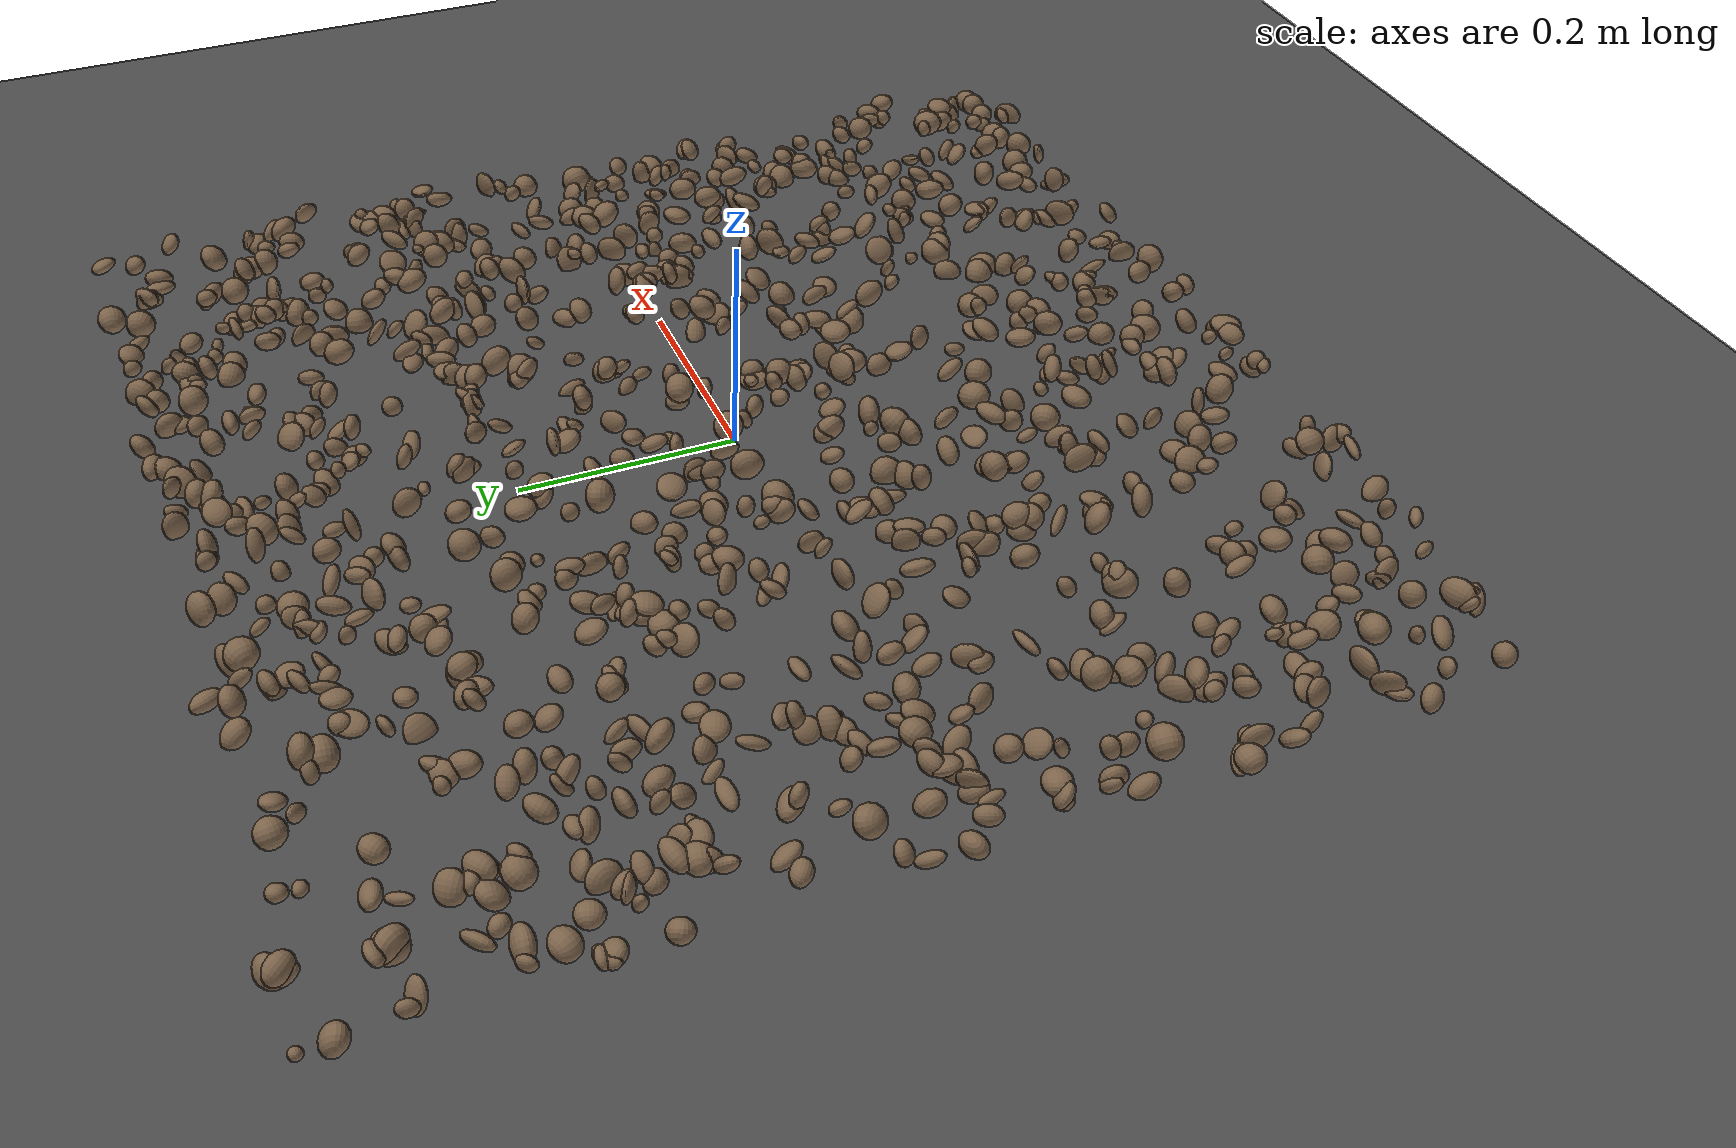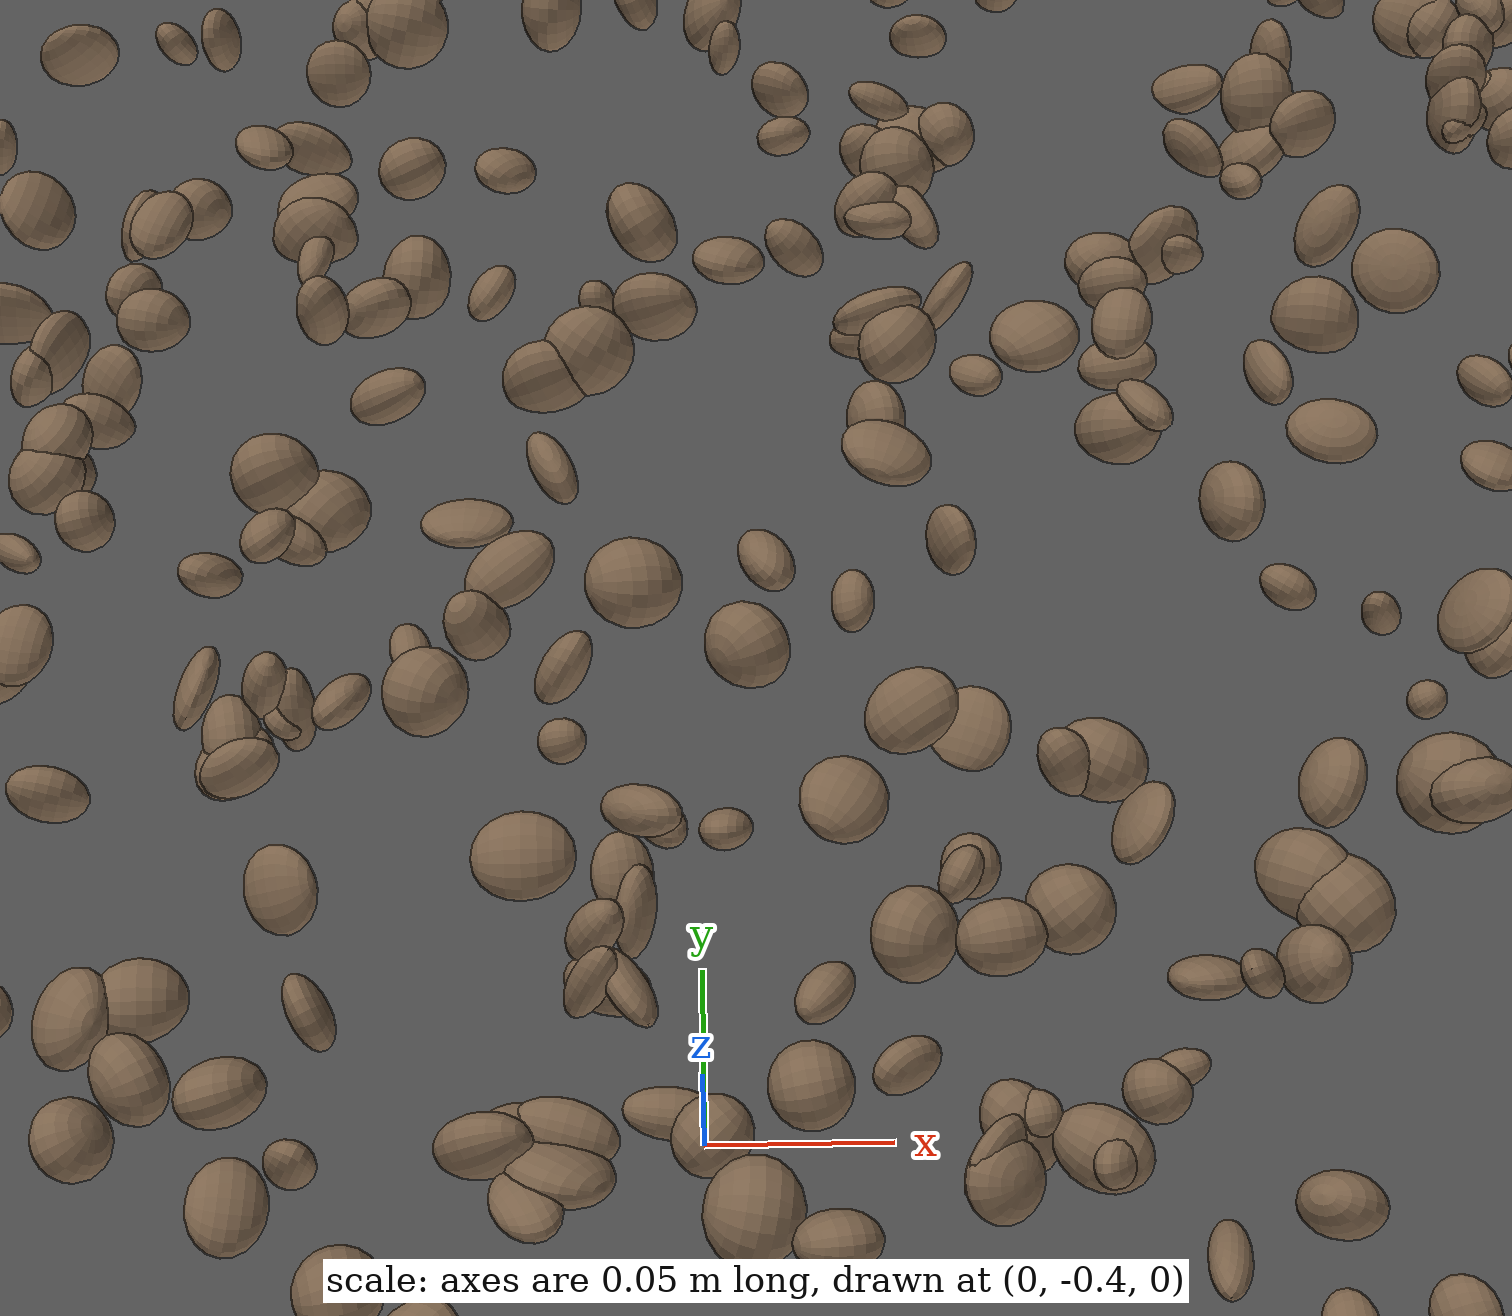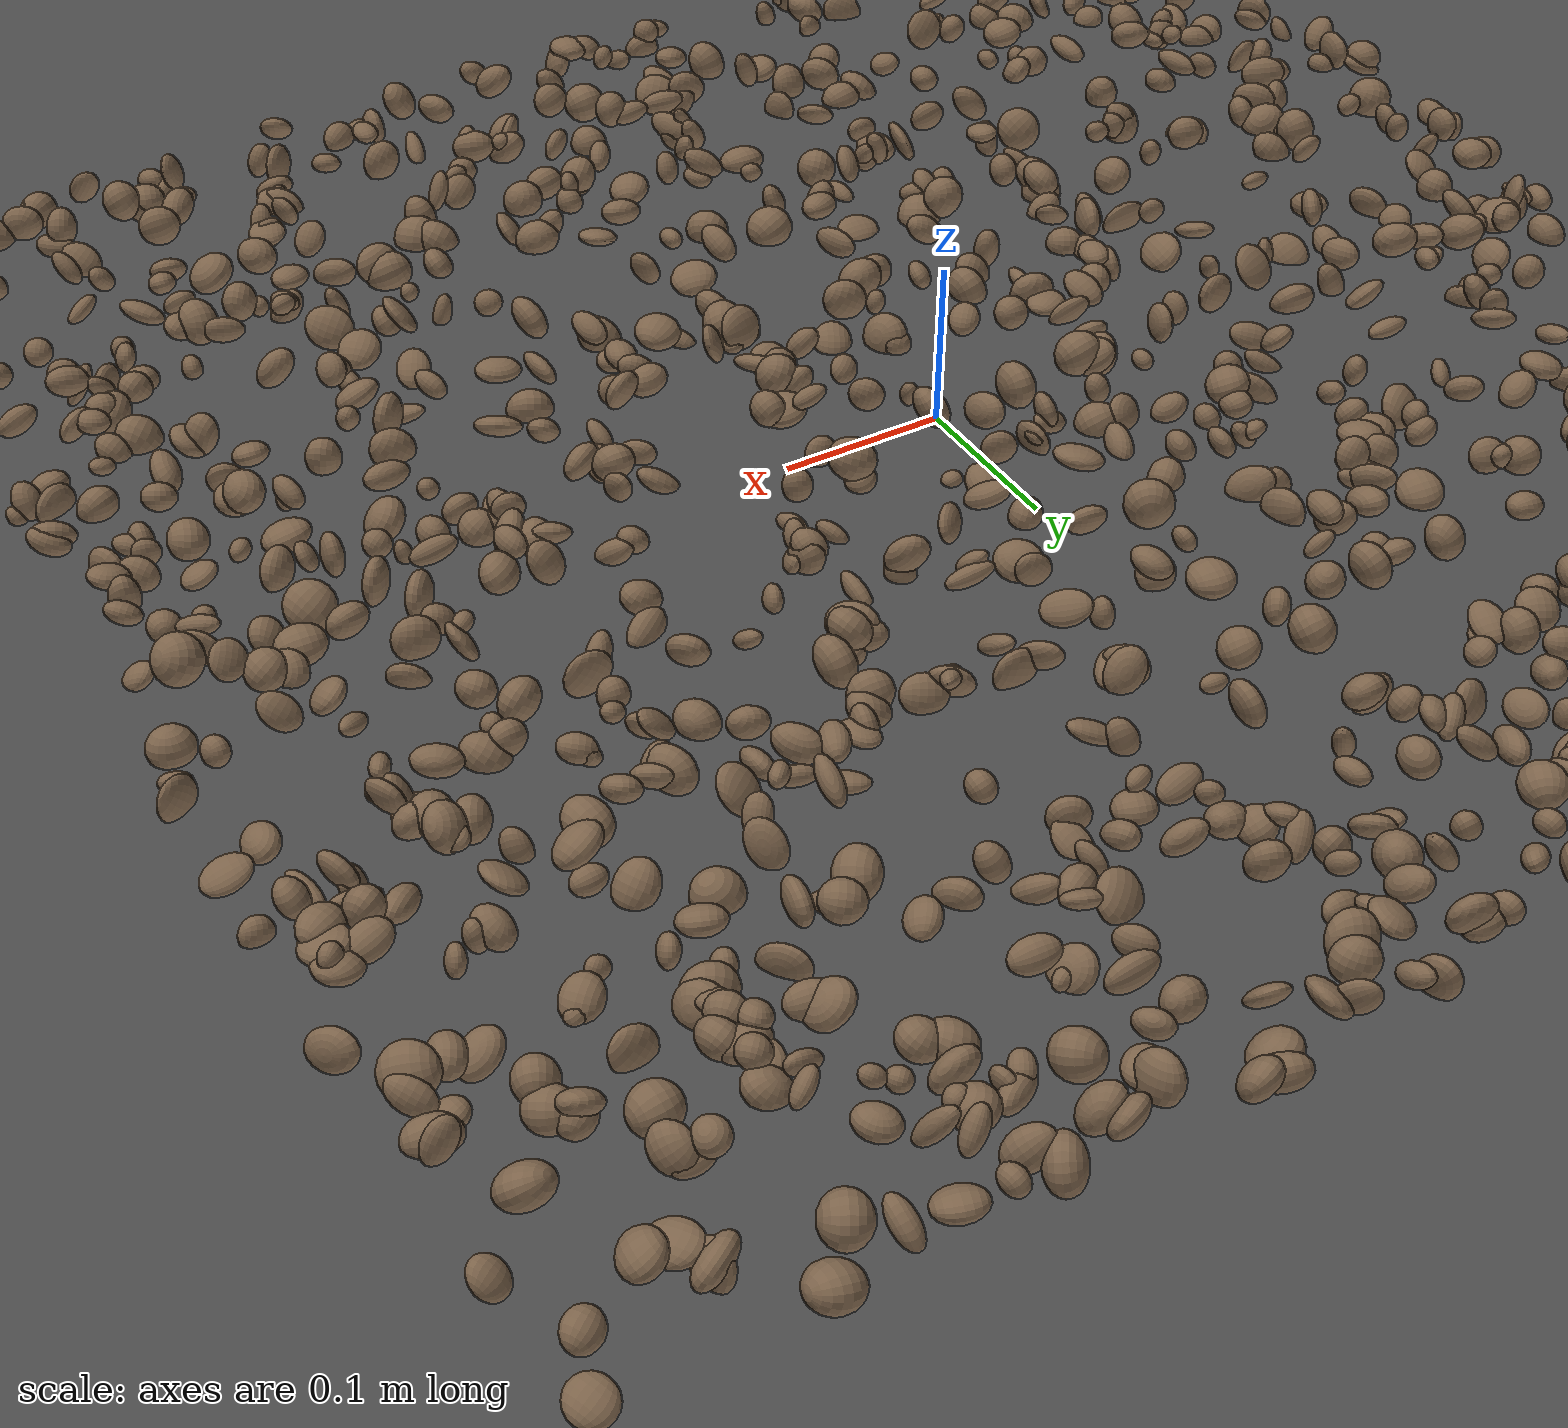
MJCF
<mujoco model="rocky_terrain_scene">
    <compiler angle="radian" inertiafromgeom="true" />
    <option timestep="0.002" gravity="0 0 -9.81" />

    <worldbody>
        <light name="sunlight" pos="5 5 5" dir="-1 -1 -1" diffuse="1 1 1" specular="0.5 0.5 0.5" ambient="0.5 0.5 0.5" />

        <geom name="ground_plane" type="plane" size="50 50 0.1" rgba="0.3 0.3 0.3 1" />

        <body name="rocky_terrain_body">

        <geom name="rock1" type="ellipsoid" size="0.0058753187097030065 0.008316303318437348 0.011475259819730615" pos="-0.17588456265098495 0.42529609043374683 0.013255254049172289" quat="0.2491289942226275 0.1288064528234482 0.30467739319352444 0.31738715976039983" rgba="0.5 0.4 0.3 1" /><geom name="rock2" type="ellipsoid" size="0.005838220182969594 0.006823455815576213 0.007947893236953961" pos="-0.43763924488966033 -0.15776755755074634 0.011054357800889977" quat="0.11865181053567918 0.45670362696555145 0.18469041689088808 0.2399541456078813" rgba="0.5 0.4 0.3 1" /><geom name="rock3" type="ellipsoid" size="0.00596104170811151 0.005042090155393729 0.006538506590754992" pos="0.025211255688025513 0.05414075778834537 1.6913108338748595e-05" quat="0.21485912766574175 0.2407750150388951 0.3023854897231359 0.2419803675722272" rgba="0.5 0.4 0.3 1" /><geom name="rock4" type="ellipsoid" size="0.009542147475168333 0.006851531598712211 0.009099757889137286" pos="0.49460249154938984 0.1882637588331879 0.001097630396784026" quat="0.5579231006591339 0.01786948519163838 0.3898870919159675 0.03432032223326024" rgba="0.5 0.4 0.3 1" /><geom name="rock5" type="ellipsoid" size="0.008041708710555923 0.012518746531796918 0.005670669584253122" pos="-0.3012992225161778 0.21241294010153056 0.0018844763278156795" quat="0.006313675136243944 0.35471071235840185 0.18304856417895712 0.455927048326397" rgba="0.5 0.4 0.3 1" /><geom name="rock6" type="ellipsoid" size="0.0143285917157094 0.014864480334750834 0.012213329578849665" pos="-0.045384684471182046 0.1413437138248531 0.013479265433991097" quat="0.06655740941805857 0.1379166088368582 0.40493881094195044 0.3905871708031329" rgba="0.5 0.4 0.3 1" /><geom name="rock7" type="ellipsoid" size="0.014137466223903349 0.006104149992981644 0.014369091707570857" pos="-0.2985397231034361 0.023360677006965425 0.001594474488984774" quat="0.12228787508755358 0.4583585620072289 0.16637946171262266 0.2529741011925948" rgba="0.5 0.4 0.3 1" /><geom name="rock8" type="ellipsoid" size="0.005351277050106085 0.012970561194708411 0.007111668728992904" pos="-0.10686208489567228 -0.4068108780158425 0.011218570875314136" quat="0.25986781002407333 0.3429326273304966 0.2320447328454054 0.16515482980002466" rgba="0.5 0.4 0.3 1" /><geom name="rock9" type="ellipsoid" size="0.005188863281566392 0.010072636620834338 0.010166864842451242" pos="-0.34883517475311643 0.05574510150386769 0.00022381666891129026" quat="0.23484638724612047 0.5738696139109065 0.15653432902875195 0.034749669814221" rgba="0.5 0.4 0.3 1" /><geom name="rock10" type="ellipsoid" size="0.00806265038067201 0.008144385875041071 0.005522293036260165" pos="-0.04915247877262974 0.16934540693139288 0.006444461975280243" quat="0.12299774087206397 0.4100335953347179 0.19454003136959883 0.2724286324236193" rgba="0.5 0.4 0.3 1" /><geom name="rock11" type="ellipsoid" size="0.012547841359214332 0.006321043280662669 0.008363002419561593" pos="-0.40812928347913335 -0.3155466560440251 0.01440678127648765" quat="0.3129163351576302 0.23430125297782115 0.287125939180526 0.16565647268402267" rgba="0.5 0.4 0.3 1" /><geom name="rock12" type="ellipsoid" size="0.010741408728277828 0.006124647363382885 0.010332900047365612" pos="-0.3761411158503276 -0.0371182972110391 0.001487266266022818" quat="0.32364041253178344 0.325991842258903 0.3239732974548557 0.026394447754457886" rgba="0.5 0.4 0.3 1" /><geom name="rock13" type="ellipsoid" size="0.008741556933093596 0.012853223852114886 0.007403838442365956" pos="-0.22102094163031905 0.2976190314856775 0.004646503950506406" quat="0.22489936565463362 0.000659082636298021 0.07628852687078981 0.6981530248382786" rgba="0.5 0.4 0.3 1" /><geom name="rock14" type="ellipsoid" size="0.00924645082270827 0.008066792279310765 0.012401585166997573" pos="-0.23361286167576434 0.2358056115213124 0.002524561342818698" quat="0.2554911254550764 0.20352003242016542 0.22972414578303674 0.31126469634172144" rgba="0.5 0.4 0.3 1" /><geom name="rock15" type="ellipsoid" size="0.011874150907726934 0.009211087627345328 0.01176443260249471" pos="0.3155141405138281 -0.44849800263953266 0.010960570954091113" quat="0.2910877407514349 0.27334400497536226 0.2261872758162197 0.2093809784569832" rgba="0.5 0.4 0.3 1" /><geom name="rock16" type="ellipsoid" size="0.009262308217769258 0.013385827362359732 0.012272964764802635" pos="-0.12788890604231695 -0.384759680838233 0.005453866252957999" quat="0.19412911299833704 0.2500720954481239 0.18828791337126918 0.36751087818226974" rgba="0.5 0.4 0.3 1" /><geom name="rock17" type="ellipsoid" size="0.011501977565619517 0.014056421114750261 0.00664265825215249" pos="0.19870725323048133 -0.17114369807013052 0.0013307692135530918" quat="0.013905899739883933 0.5364684722907087 0.4227527004396459 0.026872927529761458" rgba="0.5 0.4 0.3 1" /><geom name="rock18" type="ellipsoid" size="0.012496972702540982 0.006725834816151013 0.006728825125168852" pos="-0.12274365254747954 -0.2102477945875192 0.008339982120864635" quat="0.12133679442561343 0.10052145656475651 0.27812497789022217 0.500016771119408" rgba="0.5 0.4 0.3 1" /><geom name="rock19" type="ellipsoid" size="0.012195845833145095 0.00878121344623538 0.00924209159097954" pos="-0.11963631317974299 -0.19550089271449012 0.0021274813015665023" quat="0.11242271018906581 0.07162409237331349 0.008288955939641277 0.8076642414979794" rgba="0.5 0.4 0.3 1" /><geom name="rock20" type="ellipsoid" size="0.012292959257896505 0.010842391064877797 0.012021236050767017" pos="0.42232399791055153 0.020722111406205057 0.004996992055088645" quat="0.18322809694295392 0.2645705870496318 0.3910722268344547 0.16112908917295954" rgba="0.5 0.4 0.3 1" /><geom name="rock21" type="ellipsoid" size="0.014601641810259369 0.012808652862000926 0.013268586608028581" pos="0.012262384794361147 -0.42165315947193915 0.011080628231140522" quat="0.19564432306595836 0.342881858842032 0.20765564999659797 0.2538181680954117" rgba="0.5 0.4 0.3 1" /><geom name="rock22" type="ellipsoid" size="0.01390696397265926 0.00946928419416928 0.005775849350198455" pos="0.1392290034177367 0.07256615340513894 0.00013716205207427444" quat="0.35152324908707266 0.29947691803528476 0.03389277457650555 0.315107058301137" rgba="0.5 0.4 0.3 1" /><geom name="rock23" type="ellipsoid" size="0.009328015459051195 0.010683607806671248 0.008399873345857154" pos="-0.18451366595570506 -0.20394332400429405 0.0103123969502486" quat="0.16913905571358298 0.2809063749798158 0.17631867542967383 0.3736358938769274" rgba="0.5 0.4 0.3 1" /><geom name="rock24" type="ellipsoid" size="0.01232305750307287 0.014997074892072155 0.011768546165118283" pos="-0.38154715721700017 -0.17891619161373384 0.0028614583779389786" quat="0.40762603268658343 0.00589730156860477 0.19518541899034575 0.391291246754466" rgba="0.5 0.4 0.3 1" /><geom name="rock25" type="ellipsoid" size="0.007067078324845455 0.008819851423551652 0.00859778459839354" pos="0.4306232357274927 -0.3174130318445971 0.007022723500407967" quat="0.2499418993343693 0.38098542678186026 0.024562987128786982 0.34450968675498345" rgba="0.5 0.4 0.3 1" /><geom name="rock26" type="ellipsoid" size="0.01438057776542814 0.008992143465156293 0.014407926547504585" pos="-0.17067987217588976 -0.36129783693368533 0.0013562327216568959" quat="0.3877203393836368 0.2174136329875177 0.06104518827231731 0.3338208393565281" rgba="0.5 0.4 0.3 1" /><geom name="rock27" type="ellipsoid" size="0.007878769617325424 0.007438096878410638 0.013808565911576667" pos="0.381788416217793 -0.43304606466799844 0.004616040773708357" quat="0.3748280278236153 0.3602375426462458 0.20797848558773685 0.0569559439424022" rgba="0.5 0.4 0.3 1" /><geom name="rock28" type="ellipsoid" size="0.007562299008850052 0.012944537720909217 0.008843385764064194" pos="0.09613122379806083 0.11130181080506374 0.0007864954428320336" quat="0.27355129916666615 0.3933640460008849 0.16092268565478177 0.1721619691776671" rgba="0.5 0.4 0.3 1" /><geom name="rock29" type="ellipsoid" size="0.014590694247987226 0.011704082163536913 0.011759354228243955" pos="-0.0928401280415202 -0.43866830297294457 0.006541706760980265" quat="0.3683994431829613 0.0486891148233601 0.43836572958669834 0.1445457124069804" rgba="0.5 0.4 0.3 1" /><geom name="rock30" type="ellipsoid" size="0.010251903282972085 0.01143329424930797 0.011742757285641071" pos="-0.29246384612986565 -0.326918222192217 0.004373177606562368" quat="0.15575547185195027 0.3440438741832253 0.39989860498498997 0.10030204897983432" rgba="0.5 0.4 0.3 1" /><geom name="rock31" type="ellipsoid" size="0.01209585153697517 0.006084129983200969 0.005494452568823377" pos="0.22773659502401367 0.2229952399532853 0.0033677241145289986" quat="0.06990138172831051 0.03871482399019208 0.5267020936678672 0.36468170061363014" rgba="0.5 0.4 0.3 1" /><geom name="rock32" type="ellipsoid" size="0.008986397071419249 0.006373473311593203 0.00513241072708379" pos="0.0449836919212222 0.41120155119601143 0.014636223293485243" quat="0.10842888033252711 0.24820297719250942 0.23274518095491628 0.4106229615200472" rgba="0.5 0.4 0.3 1" /><geom name="rock33" type="ellipsoid" size="0.007623250311670627 0.01058120831961459 0.007484865395738985" pos="0.06091743636599933 -0.49463214320914073 0.013357031692470862" quat="0.17093674115100355 0.3591870524495324 0.38343339028356027 0.08644281611590378" rgba="0.5 0.4 0.3 1" /><geom name="rock34" type="ellipsoid" size="0.0050680561980440296 0.00939325756574301 0.01041779128247276" pos="-0.24375055144620206 0.37392084004325576 0.011909563584629437" quat="0.19527510851980925 0.2500676500916794 0.4049415384581116 0.1497157029303998" rgba="0.5 0.4 0.3 1" /><geom name="rock35" type="ellipsoid" size="0.01293327758372569 0.007482747262199224 0.013001231593214663" pos="0.4713517751691224 0.22918760632858592 0.005473166802975221" quat="0.18375186153738987 0.14527055383591042 0.2978842010518593 0.37309338357484034" rgba="0.5 0.4 0.3 1" /><geom name="rock36" type="ellipsoid" size="0.013648780951851423 0.014175829685170897 0.012146036860620473" pos="-0.059447927580514315 0.264282060967568 0.006919892432015644" quat="0.2674036835555023 0.2778608862835953 0.3799008415832703 0.07483458857763223" rgba="0.5 0.4 0.3 1" /><geom name="rock37" type="ellipsoid" size="0.007983924975784809 0.010095848814258832 0.008430088115605895" pos="-0.1739993871423272 0.04743729120604723 0.0061794847949475295" quat="0.2324771391336961 0.3302142569373635 0.313147026900969 0.12416157702797136" rgba="0.5 0.4 0.3 1" /><geom name="rock38" type="ellipsoid" size="0.00509844741286571 0.011985536259900037 0.009386596677840591" pos="0.24152064145292051 -0.3544670618266631 0.008451593312628026" quat="0.3174450751652888 0.3790063796618252 0.001434425570888809 0.3021141196019973" rgba="0.5 0.4 0.3 1" /><geom name="rock39" type="ellipsoid" size="0.007127490288280063 0.0068337044723245375 0.010279252149854066" pos="0.44396258821367085 -0.4938826814553855 0.004885822863568745" quat="0.3878619291265122 0.18366862619993748 0.1451492373123977 0.28332020736115254" rgba="0.5 0.4 0.3 1" /><geom name="rock40" type="ellipsoid" size="0.01386934623915521 0.005032989505392149 0.011076264199341953" pos="0.11985709827341784 0.45176555518038264 0.003729377067513908" quat="0.14946037679542026 0.383116966856419 0.0861462081430979 0.38127644820506285" rgba="0.5 0.4 0.3 1" /><geom name="rock41" type="ellipsoid" size="0.014995673725979219 0.007190592287804055 0.012983968718843487" pos="-0.21689824263856117 -0.07536866626875405 0.005706036099080259" quat="0.1768227552930389 0.35692468753069184 0.33344747957556187 0.13280507760070748" rgba="0.5 0.4 0.3 1" /><geom name="rock42" type="ellipsoid" size="0.010806425295469945 0.007959268935989427 0.005597780192787933" pos="-0.3862970752562137 0.20746576137706285 0.011373105793627991" quat="0.40350709731091317 0.07313527037764372 0.4200671237093483 0.10329050860209488" rgba="0.5 0.4 0.3 1" /><geom name="rock43" type="ellipsoid" size="0.009799199459748597 0.005222391541708004 0.013665573293913057" pos="-0.13785494166903955 0.30921414148377646 0.01102270276841677" quat="0.023173620604989183 0.09876403983334947 0.5035369889128413 0.3745253506488201" rgba="0.5 0.4 0.3 1" /><geom name="rock44" type="ellipsoid" size="0.006512599956266895 0.007007793829512048 0.007159925045403618" pos="0.2751778899247074 0.43630810977989865 0.009937591442432043" quat="0.2585403705336589 0.1436941768137984 0.23449293595391385 0.3632725166986289" rgba="0.5 0.4 0.3 1" /><geom name="rock45" type="ellipsoid" size="0.013071962731434433 0.011115472977876076 0.008572642624279607" pos="0.4108458089045345 0.023731930347003716 0.0014182954416308534" quat="0.4612924499592055 0.007289532002150659 0.27027838525670006 0.26113963278194374" rgba="0.5 0.4 0.3 1" /><geom name="rock46" type="ellipsoid" size="0.007782884544991493 0.008953143954088723 0.014631104954664853" pos="-0.03631343913261054 -0.39871387057407737 0.008813245948735685" quat="0.35670445321930455 0.19805053244247384 0.3550497138709641 0.09019530046725746" rgba="0.5 0.4 0.3 1" /><geom name="rock47" type="ellipsoid" size="0.013502235972662906 0.01327575342615616 0.012488776355820734" pos="0.35120954105085744 0.46929702622712255 0.01441894183265439" quat="0.34464387248566564 0.27413289024886245 0.22025883633058407 0.16096440093488784" rgba="0.5 0.4 0.3 1" /><geom name="rock48" type="ellipsoid" size="0.013006269841180727 0.007882280927437755 0.005524229472429975" pos="0.13873216114856723 -0.1684949833918411 0.012910361657823975" quat="0.3513715105798558 0.015067275778046061 0.19767320344855738 0.43588801019354073" rgba="0.5 0.4 0.3 1" /><geom name="rock49" type="ellipsoid" size="0.014451468004950015 0.01164418635387662 0.01180585224062284" pos="0.3388802797972803 -0.29217690945710395 0.012822844976610561" quat="0.37026912373920967 0.10843098160022688 0.3161821034408686 0.2051177912196948" rgba="0.5 0.4 0.3 1" /><geom name="rock50" type="ellipsoid" size="0.006340844149745058 0.0072866845053036885 0.006656172996271418" pos="0.4333411077727469 -0.03946169504786412 0.0016569100065721076" quat="0.2996485055670632 0.07904317514491728 0.3789726601945521 0.2423356590934674" rgba="0.5 0.4 0.3 1" /><geom name="rock51" type="ellipsoid" size="0.014973650834041216 0.0061506053706618215 0.013133949110432436" pos="-0.04548915913181373 0.07670025227422461 0.004302272342431917" quat="0.17197524809692266 0.08702978105826005 0.33353251434568365 0.4074624564991336" rgba="0.5 0.4 0.3 1" /><geom name="rock52" type="ellipsoid" size="0.006040188973063461 0.00909042951169866 0.014914022415828822" pos="-0.17461791105235647 0.07510106051321663 0.004341249991143629" quat="0.5545621271501583 0.14612594407561713 0.1564351680709311 0.1428767607032935" rgba="0.5 0.4 0.3 1" /><geom name="rock53" type="ellipsoid" size="0.014217004327622608 0.00705190336423739 0.011289255138688177" pos="0.3320187848081556 -0.363743852283824 0.008428250059089225" quat="0.20873467779143814 0.3937425390016527 0.11222618522466919 0.28529659798224005" rgba="0.5 0.4 0.3 1" /><geom name="rock54" type="ellipsoid" size="0.00827779084199817 0.014980766408765972 0.012128949592060777" pos="0.23853723014510753 -0.4126330893666853 0.0005945347073722406" quat="0.018553716418060376 0.513798956032544 0.28719406719291474 0.1804532603564808" rgba="0.5 0.4 0.3 1" /><geom name="rock55" type="ellipsoid" size="0.012095575322316861 0.009640471187329233 0.009886413473063245" pos="-0.3041571441248976 -0.4024839334539745 0.002089533161070236" quat="0.26519039861168914 0.14808175886396874 0.4604372634410223 0.1262905790833198" rgba="0.5 0.4 0.3 1" /><geom name="rock56" type="ellipsoid" size="0.007220238202240383 0.008788664424290356 0.006979023345577765" pos="0.3838227112460293 -0.3038160456058244 0.0016710655437057668" quat="0.30980018946252236 0.22600596427062686 0.3093581015421368 0.154835744724714" rgba="0.5 0.4 0.3 1" /><geom name="rock57" type="ellipsoid" size="0.013711937601491093 0.008418937135255648 0.011676665679093336" pos="0.3912317212413775 0.3968268953161632 0.006015633942661243" quat="0.24899355805823228 0.2726207175148685 0.470204702226081 0.008181022200818249" rgba="0.5 0.4 0.3 1" /><geom name="rock58" type="ellipsoid" size="0.007592275758595194 0.014848224285070995 0.013965751332539265" pos="0.14064387796417666 0.3693034430189511 0.0036670271729075314" quat="0.2635081351126596 0.24881214610852223 0.002392331150019154 0.4852873876287991" rgba="0.5 0.4 0.3 1" /><geom name="rock59" type="ellipsoid" size="0.01131459016500792 0.011731650673889787 0.007237986796706449" pos="-0.4781979707294408 -0.10926062432968331 0.007896242849394068" quat="0.47523829045956745 0.043404303244608235 0.4435753480121099 0.03778205828371436" rgba="0.5 0.4 0.3 1" /><geom name="rock60" type="ellipsoid" size="0.009467741374272249 0.008952472379980467 0.010062958663167592" pos="0.45486604544870113 -0.03879477314354651 0.004901013148816465" quat="0.0839270280806334 0.02886802915445723 0.37837150529566443 0.508833437469245" rgba="0.5 0.4 0.3 1" /><geom name="rock61" type="ellipsoid" size="0.01447831603705383 0.008159064486662709 0.006736793953931057" pos="0.24712920395406213 0.4409833470107464 0.0033604538708280054" quat="0.3581047295118809 0.4469737511382554 0.1055070718367701 0.08941444751309358" rgba="0.5 0.4 0.3 1" /><geom name="rock62" type="ellipsoid" size="0.013109527291957836 0.005396717863405553 0.00590702852749809" pos="0.4421355704902673 -0.020366185088821265 0.013375136423110627" quat="0.041114832190497046 0.20695345076662824 0.4496184211898652 0.30231329585300937" rgba="0.5 0.4 0.3 1" /><geom name="rock63" type="ellipsoid" size="0.008276720131140827 0.014685642103874713 0.00921231897399256" pos="-0.21295307233017102 -0.2865978490724147 0.01280967752102311" quat="0.29551434552703915 0.4647944246787379 0.23753042795567914 0.0021608018385438957" rgba="0.5 0.4 0.3 1" /><geom name="rock64" type="ellipsoid" size="0.007715315846962259 0.012273054738444466 0.007672865329658364" pos="0.10390043509524394 -0.29163944204493997 0.009001892196275382" quat="0.2899208972675169 0.09657372776082566 0.30486785623924634 0.308637518732411" rgba="0.5 0.4 0.3 1" /><geom name="rock65" type="ellipsoid" size="0.007921772024481813 0.008810205935175234 0.008719524562277437" pos="-0.07215233787267639 -0.4894922665443999 0.012894149570117428" quat="0.346075600441504 0.34140860934478945 0.03080754339987576 0.2817082468138308" rgba="0.5 0.4 0.3 1" /><geom name="rock66" type="ellipsoid" size="0.01039299274602535 0.005863603716830867 0.005012766214988994" pos="0.13968179088862798 0.34535582676497945 0.008368023855622436" quat="0.30881786491425023 0.05489857352441346 0.36520942863284 0.2710741329284963" rgba="0.5 0.4 0.3 1" /><geom name="rock67" type="ellipsoid" size="0.006017689577948745 0.007883729588166032 0.006977813672097818" pos="-0.3084585697914948 0.3487529764414766 0.003135338976514539" quat="0.10035216851258684 0.17533094331428625 0.37686337775494516 0.3474535104181818" rgba="0.5 0.4 0.3 1" /><geom name="rock68" type="ellipsoid" size="0.011478039300558875 0.010499184375014771 0.014689880245811315" pos="-0.29715403264714724 0.32813807723471955 0.006753608862188551" quat="0.008108346613220394 0.3758264713090284 0.33619769505171626 0.279867487026035" rgba="0.5 0.4 0.3 1" /><geom name="rock69" type="ellipsoid" size="0.014768234324241496 0.008108114758460903 0.010964173493869692" pos="-0.4109418331662378 -0.218321541444503 0.014354495195836063" quat="0.00334628186436852 0.17572665251427214 0.6676138182248517 0.1533132473965077" rgba="0.5 0.4 0.3 1" /><geom name="rock70" type="ellipsoid" size="0.011469774551302662 0.012237136477860774 0.014330871234799071" pos="0.35140588699148523 0.13110473879130125 0.0005352603599137995" quat="0.4778376082479514 0.22265883791667154 0.14182086909546826 0.15768268473990876" rgba="0.5 0.4 0.3 1" /><geom name="rock71" type="ellipsoid" size="0.006925096671102207 0.00870746042507477 0.008284449612124514" pos="-0.22975950879390572 0.1471649632924027 0.012239493698269202" quat="0.17863184686187808 0.17697240256270955 0.5959792050899922 0.04841654548542009" rgba="0.5 0.4 0.3 1" /><geom name="rock72" type="ellipsoid" size="0.010609801127871034 0.008989959026835179 0.013549380653715196" pos="0.3364481664056751 0.36188645196571034 0.0069160870654294" quat="0.1051531314659168 0.38698328797621157 0.11524359480499824 0.3926199857528734" rgba="0.5 0.4 0.3 1" /><geom name="rock73" type="ellipsoid" size="0.006963878954510127 0.013097447731200255 0.011576566308601315" pos="0.011113522853631874 -0.09782631926836083 0.0015716536195071117" quat="0.20309668361191438 0.39095537193019975 0.022777043224206508 0.3831709012336794" rgba="0.5 0.4 0.3 1" /><geom name="rock74" type="ellipsoid" size="0.012873610274989213 0.011135607478034697 0.011168487128523048" pos="0.279475529334712 -0.34722483889401035 0.011424441263891479" quat="0.28303739429036684 0.08726351578783013 0.18361511566571223 0.4460839742560909" rgba="0.5 0.4 0.3 1" /><geom name="rock75" type="ellipsoid" size="0.006470510259660449 0.005410765859540227 0.011005179051596366" pos="-0.1369418350762771 0.30743473258931264 0.0039092085457867135" quat="0.23448515105324938 0.16664484252065692 0.29888382432669314 0.29998618209940064" rgba="0.5 0.4 0.3 1" /><geom name="rock76" type="ellipsoid" size="0.013753413389927995 0.011938945456460496 0.0072419031850079665" pos="0.00839106126230671 0.2959482296698659 0.009270977255286908" quat="0.33311850790690095 0.1472601681425211 0.41640613765778883 0.10321518629278915" rgba="0.5 0.4 0.3 1" /><geom name="rock77" type="ellipsoid" size="0.009744647137301719 0.0059204772200998745 0.007226851766352467" pos="0.064660965934208 -0.12640190611963598 0.0015796822609329701" quat="0.2322385993065343 0.313933096222768 0.2450389448422566 0.2087893596284412" rgba="0.5 0.4 0.3 1" /><geom name="rock78" type="ellipsoid" size="0.01034549955848876 0.006691341077701252 0.005552420978062935" pos="0.23872908446555707 0.22509483941594466 0.011104062281879832" quat="0.35865396716045006 0.31986082595948384 0.07302599094341174 0.24845921593665432" rgba="0.5 0.4 0.3 1" /><geom name="rock79" type="ellipsoid" size="0.005091256667576316 0.009796375762399254 0.00993397425947884" pos="-0.3656670654290467 -0.4163603150080061 0.009986960410205924" quat="0.20578627622461543 0.009863674573114824 0.3719963744522978 0.4123536747499719" rgba="0.5 0.4 0.3 1" /><geom name="rock80" type="ellipsoid" size="0.01062805579844053 0.014830760613141532 0.007706566369089441" pos="-0.3332899467771159 0.2609204327684551 0.008602769764327195" quat="0.01801165588994419 0.2297912998386453 0.2719213502776221 0.4802756939937884" rgba="0.5 0.4 0.3 1" /><geom name="rock81" type="ellipsoid" size="0.014453109177974287 0.006983935099187677 0.0074741888721468405" pos="-0.3755273162740925 -0.26834962210532587 0.009430320430716182" quat="0.2402229734094835 0.13648664880632322 0.29873667369693435 0.3245537040872589" rgba="0.5 0.4 0.3 1" /><geom name="rock82" type="ellipsoid" size="0.011178276423576501 0.01073398557042236 0.009451430926995288" pos="0.009375297281175476 0.10334396108576682 0.0012422913885955106" quat="0.42619262857310913 0.26887371299934293 0.18790342800070797 0.11703023042683997" rgba="0.5 0.4 0.3 1" /><geom name="rock83" type="ellipsoid" size="0.014758169296673663 0.008959155327322624 0.013913294450030131" pos="0.07156845326041694 0.4501956663091117 0.013366846097507205" quat="0.4691820210380409 0.13152442352900467 0.3524770451829839 0.04681651024997052" rgba="0.5 0.4 0.3 1" /><geom name="rock84" type="ellipsoid" size="0.010288828048418585 0.01123721841238097 0.011056884102208103" pos="-0.09377225794632882 0.23374163880695653 0.004168096212896868" quat="0.35687761450140554 0.0038458981137992816 0.14339948681319473 0.49587700057160045" rgba="0.5 0.4 0.3 1" /><geom name="rock85" type="ellipsoid" size="0.013082052674074512 0.00618711565137043 0.00859517363527187" pos="-0.10355887506696093 -0.2666611140776315 0.007191524109725529" quat="0.44874981430831723 0.052057822655827916 0.24295589212774477 0.2562364709081101" rgba="0.5 0.4 0.3 1" /><geom name="rock86" type="ellipsoid" size="0.006559473759300949 0.011268103187817919 0.011886529238242086" pos="-0.00800005240988666 0.13522059965871414 0.01252497177354936" quat="0.33093966194073915 0.19546740962536402 0.2952687832936631 0.17832414514023373" rgba="0.5 0.4 0.3 1" /><geom name="rock87" type="ellipsoid" size="0.009391413576545693 0.008200414410113575 0.009161151914029554" pos="0.1194396493239488 -0.3890442164626208 0.005034891373138191" quat="0.12426782457599529 0.2523864550529387 0.013020163249809329 0.6103255571212566" rgba="0.5 0.4 0.3 1" /><geom name="rock88" type="ellipsoid" size="0.005069177819000975 0.013860353624929857 0.011092070241948316" pos="0.08025766594485917 -0.12161393255129449 0.009115974648810289" quat="0.0009519481750484232 0.18556725103130886 0.4975934228183696 0.31588737797527305" rgba="0.5 0.4 0.3 1" /><geom name="rock89" type="ellipsoid" size="0.012062318617794523 0.006425084708610474 0.010089562719287393" pos="-0.2081029235028954 0.048530863842360716 0.014586009379341555" quat="0.11147408272617777 0.39164880643357985 0.20409418535415064 0.2927829254860917" rgba="0.5 0.4 0.3 1" /><geom name="rock90" type="ellipsoid" size="0.014411166773832161 0.008640784106322345 0.00780121491778538" pos="-0.09003392453487935 0.3810404999885534 0.003185440674442779" quat="0.34077256527266936 0.2599145451392613 0.130064282711922 0.2692486068761473" rgba="0.5 0.4 0.3 1" /><geom name="rock91" type="ellipsoid" size="0.009088682731243249 0.01057007222964429 0.013100993671124148" pos="-0.22839005627806586 0.3081953340192647 0.00699838282667786" quat="0.31548995137830005 0.34950883528014665 0.1885254515735196 0.14647576176803367" rgba="0.5 0.4 0.3 1" /><geom name="rock92" type="ellipsoid" size="0.01019566719270539 0.0055333485877171575 0.006269341314021735" pos="0.12456560948279594 0.04526383337811635 0.0007670502728831985" quat="0.39228872248099916 0.019465555672163726 0.008756815600855337 0.5794889062459817" rgba="0.5 0.4 0.3 1" /><geom name="rock93" type="ellipsoid" size="0.011977886655390776 0.006891687468672943 0.008921440299140989" pos="-0.4004262028066824 0.33956917764652816 0.010018980068244593" quat="0.12488388800694612 0.3148526766307495 0.1981229422290781 0.3621404931332263" rgba="0.5 0.4 0.3 1" /><geom name="rock94" type="ellipsoid" size="0.008311187505171163 0.01119717568673207 0.011694854454200758" pos="-0.4983216319232112 0.2803191508675672 0.008782565065633663" quat="0.0028932987591225342 0.4547265980980266 0.2401946959538897 0.30218540718896103" rgba="0.5 0.4 0.3 1" /><geom name="rock95" type="ellipsoid" size="0.010048279967968917 0.008301898207383718 0.01105314439261235" pos="0.4744231417748427 0.18386269561093216 0.010147142314174787" quat="0.47449113593553527 0.1608087271356755 0.0015602500342785817 0.3631398868945106" rgba="0.5 0.4 0.3 1" /><geom name="rock96" type="ellipsoid" size="0.006427553019137918 0.006959641179940291 0.014122678688705221" pos="0.30945966126877067 -0.019683541996094123 0.011314543831575102" quat="0.14999591072414167 0.4157514332190634 0.14042302480151433 0.29382963125528067" rgba="0.5 0.4 0.3 1" /><geom name="rock97" type="ellipsoid" size="0.012517487344531161 0.010832239570375327 0.012345906390574736" pos="0.47028070503861774 -0.33035556437105584 0.00562691326401531" quat="0.2852340879282111 0.030653830354110213 0.32939308282562 0.3547189988920586" rgba="0.5 0.4 0.3 1" /><geom name="rock98" type="ellipsoid" size="0.01379014983672125 0.011323606506002441 0.008100268897592845" pos="0.18005408154650426 -0.29610454903752015 0.0015755397793418451" quat="0.1663534944453258 0.4015459354601108 0.2240361688064926 0.20806440128807072" rgba="0.5 0.4 0.3 1" /><geom name="rock99" type="ellipsoid" size="0.010572655451394545 0.006260102629493312 0.011075626164093374" pos="-0.2436830635010805 0.19362714017962157 0.0067386683936758555" quat="0.4017240982128609 0.16606695745692354 0.3820201434007285 0.050188800929487166" rgba="0.5 0.4 0.3 1" /><geom name="rock100" type="ellipsoid" size="0.005393982632131056 0.0084923773859119 0.008288443066970044" pos="0.44404391241779284 -0.09227144508527663 0.013249751879064844" quat="0.28069173817960763 0.2772449396424131 0.20670212840897814 0.23536119376900114" rgba="0.5 0.4 0.3 1" /><geom name="rock101" type="ellipsoid" size="0.013901545518426064 0.0053043259602606274 0.009056996620086893" pos="0.13671827705615713 0.3275318861455214 0.0013451223978538074" quat="0.27477706091148746 0.17428548346462663 0.37318314675025044 0.1777543088736355" rgba="0.5 0.4 0.3 1" /><geom name="rock102" type="ellipsoid" size="0.009187171799160555 0.012760929453455453 0.009814432980324654" pos="-0.20303774438747335 0.30779598846217504 0.0037648334043082748" quat="0.29169814249327136 0.2780471707534357 0.30241516388547646 0.12783952286781647" rgba="0.5 0.4 0.3 1" /><geom name="rock103" type="ellipsoid" size="0.012064562469515736 0.009485107302739541 0.011916792283361784" pos="-0.49535978608324005 0.011849933825367809 0.002525985931973323" quat="0.1391358620540096 0.6578825250186235 0.15194303690976008 0.05103857601760687" rgba="0.5 0.4 0.3 1" /><geom name="rock104" type="ellipsoid" size="0.010731566373748759 0.005275367349084197 0.006123356032629567" pos="-0.08545605913015686 -0.2459299104584839 0.0008587077964235667" quat="0.2268309426289309 0.23111006621053165 0.34902682589732636 0.1930321652632111" rgba="0.5 0.4 0.3 1" /><geom name="rock105" type="ellipsoid" size="0.012680092635229363 0.007988550125166 0.013781704638019244" pos="0.040015528110010856 -0.303718528254174 0.011347265512337158" quat="0.0629153023870933 0.14794060235612447 0.4144599052209202 0.3746841900358621" rgba="0.5 0.4 0.3 1" /><geom name="rock106" type="ellipsoid" size="0.0064615018542957545 0.008682795124901858 0.007413036595524704" pos="-0.26840847659393263 -0.2152286471100554 0.009985097762565395" quat="0.2411379673670506 0.3647352879202462 0.3760355985058149 0.018091146206888273" rgba="0.5 0.4 0.3 1" /><geom name="rock107" type="ellipsoid" size="0.0054802421166927585 0.008425135703945217 0.008642861971410983" pos="0.07120212194476205 -0.3276620313744574 0.01151015596906266" quat="0.07852715647077872 0.12657055857520386 0.3269568228259916 0.4679454621280258" rgba="0.5 0.4 0.3 1" /><geom name="rock108" type="ellipsoid" size="0.007252314871641106 0.005871413561396564 0.006548914691146631" pos="0.0855242432761455 -0.39775309188323416 0.01288501433019359" quat="0.4305751464768519 0.4794500589208892 0.018576889048004183 0.07139790555425474" rgba="0.5 0.4 0.3 1" /><geom name="rock109" type="ellipsoid" size="0.005004163901157388 0.012999237398982177 0.008691555236713123" pos="0.3444680175626381 -0.48471726755931066 0.010054512266498849" quat="0.39501738747441384 0.19145069215002203 0.18474547475772082 0.22878644561784334" rgba="0.5 0.4 0.3 1" /><geom name="rock110" type="ellipsoid" size="0.007587834254995571 0.008487743206881667 0.00606135458815852" pos="0.35538332642073267 -0.2627994088815093 0.002182350455763655" quat="0.08056852466505696 0.45666416705595814 0.0009311391508237965 0.4618361691281611" rgba="0.5 0.4 0.3 1" /><geom name="rock111" type="ellipsoid" size="0.010148344924840763 0.011286863386086997 0.014172147061098924" pos="-0.39882687966171326 0.34429779873724975 0.012642493063581981" quat="0.1446020955755847 0.19851529391124553 0.331279354511054 0.32560325600211576" rgba="0.5 0.4 0.3 1" /><geom name="rock112" type="ellipsoid" size="0.01276870891726323 0.00978250319654135 0.012154759042962482" pos="0.07906362788425869 0.46117467518444466 0.013165777386627397" quat="0.132551607315545 0.13719917631149994 0.677819363412318 0.05242985296063706" rgba="0.5 0.4 0.3 1" /><geom name="rock113" type="ellipsoid" size="0.01088249349088104 0.008785534910371788 0.01181096757704754" pos="0.09682496498395377 0.3222055285413554 0.0006255267414120657" quat="0.2922345060774812 0.2931153155900813 0.2136016701427724 0.20104850818966516" rgba="0.5 0.4 0.3 1" /><geom name="rock114" type="ellipsoid" size="0.013416350187541518 0.006032591090734598 0.009275915411774277" pos="-0.17357084313255278 -0.08787255140443284 0.011752133225013651" quat="0.26727865810727613 0.31530866269158836 0.21722121463412783 0.20019146456700768" rgba="0.5 0.4 0.3 1" /><geom name="rock115" type="ellipsoid" size="0.013799083729428781 0.013404028901758618 0.008396549170418995" pos="0.1887616069296676 -0.053604783737649986 0.0015379326484890037" quat="0.2193550971084463 0.383855059075249 0.34506850383175375 0.051721339984550876" rgba="0.5 0.4 0.3 1" /><geom name="rock116" type="ellipsoid" size="0.010527108034596246 0.005402156911136577 0.00874281874328166" pos="0.46190270478208206 -0.006558533659470234 0.010921243791562446" quat="0.23876351879952332 0.22831358471820445 0.2475087851659803 0.2854141113162919" rgba="0.5 0.4 0.3 1" /><geom name="rock117" type="ellipsoid" size="0.005643590471385251 0.012705581570546368 0.006407988105443794" pos="-0.4779904057541132 -0.2784760743642878 0.0009699668555730784" quat="0.30824950584524385 0.6241361393441498 0.05150172140414733 0.01611263340645892" rgba="0.5 0.4 0.3 1" /><geom name="rock118" type="ellipsoid" size="0.01113529446988763 0.010497432933104529 0.01181991124734592" pos="0.44630478623948955 -0.46765055126574917 0.007774755097209028" quat="0.5663878980112728 0.20326147262187896 0.10622454368139661 0.12412608568545168" rgba="0.5 0.4 0.3 1" /><geom name="rock119" type="ellipsoid" size="0.011037330189928616 0.012383477049266945 0.01031426490341033" pos="-0.14823273435796624 0.3214298104350738 0.01005161924028271" quat="0.2048383137303385 0.2884792336056715 0.18848892171880952 0.31819353094518044" rgba="0.5 0.4 0.3 1" /><geom name="rock120" type="ellipsoid" size="0.012070816431756217 0.011714255668322784 0.006184274717738621" pos="-0.09203679868478232 0.05560460784249699 0.005388253535045083" quat="0.3116452783893266 0.5468608222305014 0.015360179190230118 0.12613372018994187" rgba="0.5 0.4 0.3 1" /><geom name="rock121" type="ellipsoid" size="0.013203000893475491 0.008773595653972413 0.014886441014349515" pos="-0.47193640280616267 0.33516033118974875 0.011303589205791829" quat="0.5496200280175129 0.058899547529668674 0.3381555327470325 0.05332489170578598" rgba="0.5 0.4 0.3 1" /><geom name="rock122" type="ellipsoid" size="0.014583755144112871 0.01064091715185848 0.007200923214179889" pos="-0.020191233286120935 0.018344340411200366 0.010162707153284246" quat="0.22127271606977145 0.22652166811101745 0.18697091594045906 0.365234699878752" rgba="0.5 0.4 0.3 1" /><geom name="rock123" type="ellipsoid" size="0.014320047576047146 0.009938836315058075 0.012568944807895142" pos="-0.4175826331660166 0.3417770513438044 0.0024806049807490735" quat="0.12894925910431984 0.3865534435132789 0.16762740689092792 0.3168698904914733" rgba="0.5 0.4 0.3 1" /><geom name="rock124" type="ellipsoid" size="0.008367411218006505 0.007967430070766314 0.011982607583403459" pos="0.4612298797829455 -0.406222837955893 0.009460745920639219" quat="0.35846614648729413 0.17827523023442537 0.2728934495423922 0.1903651737358883" rgba="0.5 0.4 0.3 1" /><geom name="rock125" type="ellipsoid" size="0.009752830018260446 0.008585054803568902 0.013890133473294236" pos="-0.06570926953705836 -0.2398185942761134 0.003812915244336209" quat="0.05473796661877111 0.5341363403762699 0.31933584423149075 0.09178984877346824" rgba="0.5 0.4 0.3 1" /><geom name="rock126" type="ellipsoid" size="0.010468076031231698 0.006245894988560782 0.0055512098769541045" pos="0.40406943759298464 0.12422524296848181 0.012368248390437604" quat="0.3147593554522937 0.30865447590038536 0.11274022836612192 0.26384594028119895" rgba="0.5 0.4 0.3 1" /><geom name="rock127" type="ellipsoid" size="0.0060816562723588884 0.006008851481594096 0.006880924845397889" pos="-0.36380559559709846 0.46377660615439487 0.0004738834946001685" quat="0.2752087978916497 0.3316335522134107 0.14016577053615958 0.25299187935878004" rgba="0.5 0.4 0.3 1" /><geom name="rock128" type="ellipsoid" size="0.011702152989114069 0.005666547722718596 0.011123357520370275" pos="-0.4773568449670801 -0.3564741604639432 0.006159431378460054" quat="0.02337307364430609 0.2117021663840636 0.35783247551930275 0.40709228445232754" rgba="0.5 0.4 0.3 1" /><geom name="rock129" type="ellipsoid" size="0.006316711776192417 0.014525443023270634 0.00743955116736276" pos="0.22095969924487213 0.24330967594296615 0.013563650889494386" quat="0.044798450591643314 0.10627769208430944 0.17389270311727878 0.6750311542067685" rgba="0.5 0.4 0.3 1" /><geom name="rock130" type="ellipsoid" size="0.012910746008633539 0.014455433897418862 0.010375211904436157" pos="0.1531602267992621 0.1523379152510571 0.014859985018029943" quat="0.13564921142680703 0.3240763044249856 0.33575489233097966 0.20451959181722765" rgba="0.5 0.4 0.3 1" /><geom name="rock131" type="ellipsoid" size="0.013917097249292212 0.008758006826650296 0.013480359645822476" pos="-0.03606788859290355 0.20857988915360615 0.0114543891730924" quat="0.2695180223471299 0.2701129036478107 0.24684794466568816 0.21352112933937126" rgba="0.5 0.4 0.3 1" /><geom name="rock132" type="ellipsoid" size="0.01230443986747703 0.013873845645755879 0.012033923946451287" pos="-0.38257785742547923 -0.14803798201667118 0.012121467061335038" quat="0.23122334766123048 0.2783475809489435 0.2283271406424931 0.26210193074733296" rgba="0.5 0.4 0.3 1" /><geom name="rock133" type="ellipsoid" size="0.008944947159925207 0.007972015022843764 0.01340643293737722" pos="-0.09538074209922487 -0.1616028353844956 0.014221199631470734" quat="0.43119158697880644 0.12321128146076034 0.22934465482686786 0.2162524767335654" rgba="0.5 0.4 0.3 1" /><geom name="rock134" type="ellipsoid" size="0.010157634791267299 0.014586442758414003 0.013100315698646094" pos="0.32302606044307425 0.1121268890430317 0.010448892039053428" quat="0.1672346759374401 0.22315828353646608 0.4674851663958842 0.1421218741302096" rgba="0.5 0.4 0.3 1" /><geom name="rock135" type="ellipsoid" size="0.007656114417620712 0.0118225874202047 0.0058483848701744775" pos="0.10642798630295347 -0.4093855324028931 0.012542744199828598" quat="0.22953177758964174 0.27625104121307537 0.07903481536369832 0.41518236583358464" rgba="0.5 0.4 0.3 1" /><geom name="rock136" type="ellipsoid" size="0.009347926839001533 0.005411290799660974 0.007481085147570909" pos="0.3382635214251688 0.33635056938890884 0.011324241560614163" quat="0.13805698935618171 0.19515828892826528 0.2875973505223328 0.3791873711932201" rgba="0.5 0.4 0.3 1" /><geom name="rock137" type="ellipsoid" size="0.009401844053514387 0.006659652466926161 0.010688338723176314" pos="0.2938879960260752 -0.44492739692126715 0.007609007922245319" quat="0.16593662225296144 0.2444840816752749 0.2438973445061006 0.34568195156566306" rgba="0.5 0.4 0.3 1" /><geom name="rock138" type="ellipsoid" size="0.011250818451459171 0.008622097575391119 0.010718153281098673" pos="0.05558920383667321 0.36376126821118404 0.003959560375189736" quat="0.21879031621338352 0.3248589953316117 0.30998727427296574 0.146363414182039" rgba="0.5 0.4 0.3 1" /><geom name="rock139" type="ellipsoid" size="0.011252754361099017 0.006907877920249031 0.008985333888877185" pos="-0.1284404783103108 -0.2114738792300388 0.011995146094305197" quat="0.3901094124435837 0.07916121563581484 0.2637523119046817 0.26697706001591975" rgba="0.5 0.4 0.3 1" /><geom name="rock140" type="ellipsoid" size="0.013088148279467044 0.011261062801638445 0.0130655480908475" pos="-0.08157904166437635 0.41194962239620314 0.005223620945775553" quat="0.11045198385684837 0.08560961488007823 0.44444515486200453 0.35949324640106883" rgba="0.5 0.4 0.3 1" /><geom name="rock141" type="ellipsoid" size="0.012435622000972122 0.012011282877935611 0.014455236146396613" pos="-0.4154988962984104 -0.3765502993847901 0.012200419757574405" quat="0.27852141239042216 0.33969335385159355 0.1945766938517455 0.18720853990623879" rgba="0.5 0.4 0.3 1" /><geom name="rock142" type="ellipsoid" size="0.005302712358586968 0.013152543007843211 0.009290243063350741" pos="0.42949279205357394 0.05783727386369397 0.008278414937003627" quat="0.05256089817986321 0.3837281065216319 0.2931741581123331 0.2705368371861717" rgba="0.5 0.4 0.3 1" /><geom name="rock143" type="ellipsoid" size="0.008822197819960163 0.008921823004668568 0.006661423258652277" pos="-0.00592637273214669 0.46761274569867806 0.008664624867379362" quat="0.20462482871191062 0.21313109408354655 0.3093507821629079 0.2728932950416349" rgba="0.5 0.4 0.3 1" /><geom name="rock144" type="ellipsoid" size="0.00719851452588996 0.005633087985571256 0.012359990648249403" pos="-0.049234230769955145 0.042315520746703084 0.006618873442805603" quat="0.38091234265449847 0.11456987494932525 0.2755955357896212 0.2289222466065552" rgba="0.5 0.4 0.3 1" /><geom name="rock145" type="ellipsoid" size="0.005064594200185121 0.005862524373623199 0.014623250281979094" pos="-0.20522866239565685 -0.21200444456465017 0.005602195592600585" quat="0.4496334249364694 0.2555109488755261 0.08365353540513333 0.21120209078287108" rgba="0.5 0.4 0.3 1" /><geom name="rock146" type="ellipsoid" size="0.010235305004235477 0.01295541820276765 0.011220397580452996" pos="-0.16712207760056608 0.2432930388960003 0.011092308665049557" quat="0.10674098311883753 0.27731581727447746 0.254959284212897 0.36098391539378805" rgba="0.5 0.4 0.3 1" /><geom name="rock147" type="ellipsoid" size="0.014089116029116514 0.01496127738857526 0.010875113229332696" pos="-0.0907113176701847 -0.10510699404482005 0.0023417692341832696" quat="0.24714666372673894 0.23632746184178516 0.32954577529494017 0.18698009913653565" rgba="0.5 0.4 0.3 1" /><geom name="rock148" type="ellipsoid" size="0.014583100431464917 0.006337885258010052 0.011758074815673194" pos="0.4151013557317452 0.44173175411727406 0.009712674251598828" quat="0.11952076445565335 0.23056136716650752 0.34605732013978896 0.30386054823805014" rgba="0.5 0.4 0.3 1" /><geom name="rock149" type="ellipsoid" size="0.0067401894894446625 0.013667533055863344 0.005570903146411098" pos="-0.14888293557844823 0.46649549391054845 0.004987561967391587" quat="0.2364390483323497 0.4290991072973491 0.061373630689910356 0.2730882136803908" rgba="0.5 0.4 0.3 1" /><geom name="rock150" type="ellipsoid" size="0.007844893989378345 0.011095784019819421 0.006856325692072137" pos="-0.4504616610070491 -0.12250880347089721 0.0069343589576766635" quat="0.30032710147355784 0.24843107255557995 0.2836810670407033 0.16756075893015898" rgba="0.5 0.4 0.3 1" /><geom name="rock151" type="ellipsoid" size="0.0070578009634994915 0.006810562194989907 0.012494232879785749" pos="-0.029310214353813646 -0.34317249982180664 0.012871470464446321" quat="0.4724284993780314 0.05156020175551706 0.12968404996009786 0.34632724890635364" rgba="0.5 0.4 0.3 1" /><geom name="rock152" type="ellipsoid" size="0.009933328312052497 0.012926742248841636 0.0052311844926208936" pos="0.28847637028456863 -0.47366767273880994 0.010546624997513179" quat="0.3166396559648647 0.3747111812550062 0.19548361029968023 0.11316555248044899" rgba="0.5 0.4 0.3 1" /><geom name="rock153" type="ellipsoid" size="0.014403251972627217 0.012829084949289523 0.005084197116242929" pos="-0.328238096824073 -0.19376015517487066 0.0008742006592350115" quat="0.18879633419085526 0.13354533233015398 0.1900472774116804 0.48761105606731037" rgba="0.5 0.4 0.3 1" /><geom name="rock154" type="ellipsoid" size="0.014183858989272085 0.00686891036637395 0.005389996293064195" pos="-0.188672282002335 0.4068938723660761 0.011606272123388927" quat="0.29925858301277225 0.23216645242820821 0.05313506636112864 0.4154398981978909" rgba="0.5 0.4 0.3 1" /><geom name="rock155" type="ellipsoid" size="0.008177740647219564 0.01367479425613563 0.011588511019480406" pos="0.09311783808246243 0.11249667562760535 0.01297059840752832" quat="0.41088768940577935 0.12065713481136224 0.18180496549081748 0.286650210292041" rgba="0.5 0.4 0.3 1" /><geom name="rock156" type="ellipsoid" size="0.01122343854336877 0.008737441090805808 0.00864788105054222" pos="-0.47843249958084433 0.13663299567388965 0.007130236224670721" quat="0.19915747543920292 0.041927107749806 0.3393073384355678 0.4196080783754234" rgba="0.5 0.4 0.3 1" /><geom name="rock157" type="ellipsoid" size="0.008286298908672322 0.007770129948902928 0.011063294651989089" pos="0.3298555405429415 0.030486933148915374 0.007502215331480808" quat="0.4748252232437808 0.07701322259215693 0.22740917751281184 0.22075237665125036" rgba="0.5 0.4 0.3 1" /><geom name="rock158" type="ellipsoid" size="0.008330699788115474 0.011424373967853915 0.010665707193673768" pos="0.41209532953835615 -0.0027358794092320338 0.0064033211343348185" quat="0.011072080999973977 0.2566855905135395 0.3727621864928375 0.35948014199364897" rgba="0.5 0.4 0.3 1" /><geom name="rock159" type="ellipsoid" size="0.01368983797282746 0.014417246661496939 0.006832564568860103" pos="0.46328793389566836 -0.10284799250828203 0.0012194775153508979" quat="0.2087906108287775 0.1852068936240076 0.3014524159004428 0.304550079646772" rgba="0.5 0.4 0.3 1" /><geom name="rock160" type="ellipsoid" size="0.008616725956804683 0.008487236586339581 0.012883068464670248" pos="0.2827338374779116 -0.2931806591539142 0.0038259577679593984" quat="0.14552348254901862 0.31255137632940416 0.40056314985206076 0.14136199126951646" rgba="0.5 0.4 0.3 1" /><geom name="rock161" type="ellipsoid" size="0.010881892390934804 0.005629951924947472 0.01310015386016809" pos="-0.28827122368310665 -0.4451238105087043 0.003642060021373608" quat="0.10266421700720535 0.30050201717534875 0.22938572833728746 0.36744803748015836" rgba="0.5 0.4 0.3 1" /><geom name="rock162" type="ellipsoid" size="0.010125637098175856 0.010333743701107467 0.006819561123515111" pos="-0.39986245845064006 0.31626182989583906 0.014377699478073287" quat="0.4172576468133551 0.3360861709133643 0.034672772853055187 0.21198340942022545" rgba="0.5 0.4 0.3 1" /><geom name="rock163" type="ellipsoid" size="0.006701522805413522 0.011021780846340657 0.01192659060056116" pos="0.41572132171833487 0.35953051772178846 0.012176865481062041" quat="0.49078704253190597 0.028460892953343198 0.23856125657746072 0.24219080793729011" rgba="0.5 0.4 0.3 1" /><geom name="rock164" type="ellipsoid" size="0.009414362813396299 0.006184737377071341 0.01228158588789268" pos="-0.11463599310496941 0.39887901468278053 0.0018938055697945654" quat="0.2801493221260847 0.135380002844199 0.4889575651330292 0.09551310989668726" rgba="0.5 0.4 0.3 1" /><geom name="rock165" type="ellipsoid" size="0.006912745052924741 0.012711469260546358 0.014086878818961784" pos="0.2874180578571762 0.19184535973037875 0.006492947012079829" quat="0.4054439502548384 0.21027140015907422 0.3045019010511485 0.0797827485349388" rgba="0.5 0.4 0.3 1" /><geom name="rock166" type="ellipsoid" size="0.014012736295257667 0.014896813880706912 0.0090046572572765" pos="0.341802949902148 0.3316434360475663 0.0032466007395655716" quat="0.35375393804102356 0.07541445441551015 0.29304322277279765 0.27778838477066864" rgba="0.5 0.4 0.3 1" /><geom name="rock167" type="ellipsoid" size="0.010976763424397452 0.011093815628105165 0.011922109666693733" pos="0.258529296144809 0.3158998272431014 0.014383459225396958" quat="0.2932830690797178 0.32369819808070693 0.09647535087844651 0.2865433819611287" rgba="0.5 0.4 0.3 1" /><geom name="rock168" type="ellipsoid" size="0.011018216057678016 0.009802838822924702 0.005844369814923481" pos="-0.04773968494334979 0.0396841153789943 0.013591340537308925" quat="0.3263068616613144 0.20105402922280602 0.383840416134804 0.08879869298107558" rgba="0.5 0.4 0.3 1" /><geom name="rock169" type="ellipsoid" size="0.01322369627513489 0.007270151766793262 0.006855766133866785" pos="-0.07051880566569368 0.3563522276413098 0.011522306890949257" quat="0.40200469150811297 0.3145348029819116 0.20859818905167385 0.07486231645830153" rgba="0.5 0.4 0.3 1" /><geom name="rock170" type="ellipsoid" size="0.006228529171407869 0.005281400689623889 0.010876006034652417" pos="0.06273606127465459 -0.03948587677359228 0.013727760885834323" quat="0.23558384008009486 0.2960058138750046 0.30883466907769697 0.15957567696720348" rgba="0.5 0.4 0.3 1" /><geom name="rock171" type="ellipsoid" size="0.00976847206086534 0.012984127990766581 0.007428576654834963" pos="-0.3060350562718942 0.15115399398805485 0.005102214643900261" quat="0.32896717777179163 0.08885922681033058 0.12812740329900105 0.45404619211887676" rgba="0.5 0.4 0.3 1" /><geom name="rock172" type="ellipsoid" size="0.007186121085266322 0.007031661694156373 0.014930148492460958" pos="-0.41071202906526794 -0.47832073600653 0.005352295935839779" quat="0.3245556256620322 0.2956200792054196 0.07838476615553351 0.30143952897701476" rgba="0.5 0.4 0.3 1" /><geom name="rock173" type="ellipsoid" size="0.00828114312146528 0.013994533443448452 0.007257132177802682" pos="-0.07524346858781616 0.07443847016535465 0.0013115811058392534" quat="0.13002819914270128 0.3068420802557966 0.061179683557949636 0.5019500370435525" rgba="0.5 0.4 0.3 1" /><geom name="rock174" type="ellipsoid" size="0.009210593558371106 0.014452156713725996 0.014329059062219793" pos="-0.2564852016779786 0.005864232848977746 0.0013018986735376442" quat="0.311538920471969 0.20534295515180012 0.3241976243424616 0.1589205000337693" rgba="0.5 0.4 0.3 1" /><geom name="rock175" type="ellipsoid" size="0.009089911961509656 0.013780990189744203 0.010189566905677887" pos="-0.3173697191378876 0.2881209969772539 0.01002656831516641" quat="0.23571738456515348 0.36449785131288615 0.25853456914241263 0.14125019497954783" rgba="0.5 0.4 0.3 1" /><geom name="rock176" type="ellipsoid" size="0.005228262037709367 0.007465458193268335 0.011824788408319816" pos="0.3210409610322035 0.3853489055072955 0.008723001979365163" quat="0.33382975175297064 0.1333694019430881 0.21647116952488593 0.3163296767790554" rgba="0.5 0.4 0.3 1" /><geom name="rock177" type="ellipsoid" size="0.0053430582923734695 0.014653571575601688 0.013076949284855793" pos="-0.24842056571880877 -0.023652346915808642 0.012947049816313906" quat="0.11095842821013607 0.32618711677567014 0.2231600875087398 0.33969436750545395" rgba="0.5 0.4 0.3 1" /><geom name="rock178" type="ellipsoid" size="0.007630723304161613 0.01041792081547939 0.013403556736846699" pos="-0.38868388357337236 0.26210181338023186 0.011208082527468832" quat="0.4638961715066475 0.16787321131056698 0.1496111879946437 0.2186194291881417" rgba="0.5 0.4 0.3 1" /><geom name="rock179" type="ellipsoid" size="0.01243890215252625 0.013369667886340836 0.013504306128951041" pos="-0.07732557392031403 0.05056215735278169 0.00023413361640606533" quat="0.24129399214504685 0.3348972269284253 0.31558491391793525 0.10822386700859264" rgba="0.5 0.4 0.3 1" /><geom name="rock180" type="ellipsoid" size="0.014392894562121065 0.006147317598738596 0.007637488865227468" pos="-0.3161345726545004 -0.31740852465918135 0.013502677123328413" quat="0.23375016831814907 0.217372417377283 0.32334835679451956 0.22552905751004831" rgba="0.5 0.4 0.3 1" /><geom name="rock181" type="ellipsoid" size="0.007289435616781467 0.006066993486398076 0.009979816801688319" pos="0.4565332493324924 -0.4699537365792452 0.005516450678113127" quat="0.4247465640185575 0.06674481987404714 0.38134417715858854 0.12716443894880694" rgba="0.5 0.4 0.3 1" /><geom name="rock182" type="ellipsoid" size="0.009145180712285603 0.00977572243056362 0.011945647416371902" pos="-0.36229617688946636 0.05264747273263637 0.0012568846382441383" quat="0.2553864227696349 0.17931466876597996 0.09972762718392518 0.4655712812804599" rgba="0.5 0.4 0.3 1" /><geom name="rock183" type="ellipsoid" size="0.008655960760906307 0.0064306175935436105 0.008473747619983114" pos="-0.11920004964175734 0.32435082042067087 0.010226088405111938" quat="0.1636777483066173 0.333297864117958 0.309515081693308 0.19350930588211676" rgba="0.5 0.4 0.3 1" /><geom name="rock184" type="ellipsoid" size="0.007198374186239281 0.00983376142022322 0.01182654732588852" pos="0.4516934415199604 -0.08500936695545813 0.0066189624515859986" quat="0.3749668021142883 0.29993528449369333 0.07824400925908766 0.2468539041329308" rgba="0.5 0.4 0.3 1" /><geom name="rock185" type="ellipsoid" size="0.005013474229507871 0.011389221550222393 0.01074166021043216" pos="0.4386377033754173 0.013120649967922282 0.013068042127742013" quat="0.2337379000306825 0.262698915127118 0.08696777802133282 0.4165954068208667" rgba="0.5 0.4 0.3 1" /><geom name="rock186" type="ellipsoid" size="0.009766387654857281 0.005869484417944671 0.0066925301338401555" pos="-0.011689856403228283 -0.30555528920421227 0.0039701081982120206" quat="0.16987303873097523 0.18116688626702143 0.39519682770718295 0.25376324729482047" rgba="0.5 0.4 0.3 1" /><geom name="rock187" type="ellipsoid" size="0.005602413126328665 0.00833377605227556 0.00845190309866407" pos="-0.23664206746947158 -0.11231251691405053 0.010969192360007946" quat="0.3259775503785539 0.2039160529777688 0.2062049197465681 0.26390147689710924" rgba="0.5 0.4 0.3 1" /><geom name="rock188" type="ellipsoid" size="0.013901410485953839 0.010170356653426192 0.009570878579107673" pos="0.054001012830479755 -0.47679510739761055 0.01324075325120122" quat="0.13998734624474457 0.2349131016300341 0.04619910614581253 0.5789004459794088" rgba="0.5 0.4 0.3 1" /><geom name="rock189" type="ellipsoid" size="0.005605259568646356 0.012628744901218139 0.00993342056260193" pos="-0.19787845232557133 -0.24907319547429507 0.012590945362454283" quat="0.4375431040579407 0.08793598803291894 0.46206261831485257 0.012458289594287752" rgba="0.5 0.4 0.3 1" /><geom name="rock190" type="ellipsoid" size="0.014701164472784151 0.014501555481140661 0.013579161665983164" pos="0.46125014168532485 0.001834942938512385 0.014703016349923508" quat="0.12639747400780477 0.25025456420024184 0.12889181657636492 0.4944561452155884" rgba="0.5 0.4 0.3 1" /><geom name="rock191" type="ellipsoid" size="0.008497194641043704 0.007157878756846954 0.011472032548355155" pos="-0.19171737232665365 -0.4987195134729375 0.010765505959584976" quat="0.26693870635105194 0.10294714257431081 0.48041745502167227 0.14969669605296507" rgba="0.5 0.4 0.3 1" /><geom name="rock192" type="ellipsoid" size="0.007699016825770809 0.007128241311059515 0.01054877191481136" pos="-0.3372980137980536 -0.44559059811305657 0.000763914481535729" quat="0.34228574250980714 0.0658585881157188 0.1791539103163677 0.4127017590581063" rgba="0.5 0.4 0.3 1" /><geom name="rock193" type="ellipsoid" size="0.0052491367156447385 0.006305893663480304 0.010794821855263387" pos="-0.3091820488554099 -0.4948804275878841 0.007260490679768712" quat="0.3260110262109765 0.32589492575037976 0.12716669495825889 0.2209273530803848" rgba="0.5 0.4 0.3 1" /><geom name="rock194" type="ellipsoid" size="0.008165838990605565 0.013346832827782845 0.007431003129974197" pos="-0.4329775257487548 0.4897225357899406 0.0027053569325648594" quat="0.164153198226547 0.6689161419494611 0.035319934444826014 0.13161072537916577" rgba="0.5 0.4 0.3 1" /><geom name="rock195" type="ellipsoid" size="0.01152253828833651 0.00892074869150259 0.013764012251154898" pos="-0.10577144341214428 0.005621459025231923 0.011191044608785597" quat="0.26468510649917526 0.34726349204294116 0.3124925894809248 0.07555881197695878" rgba="0.5 0.4 0.3 1" /><geom name="rock196" type="ellipsoid" size="0.009727164957604027 0.013982928340277725 0.014438341803540759" pos="-0.12538189416733314 -0.08489969490934512 0.000582300060521852" quat="0.4227371446889238 0.05898272883642514 0.19190332696643236 0.3263767995082187" rgba="0.5 0.4 0.3 1" /><geom name="rock197" type="ellipsoid" size="0.009519821426964472 0.01256135192115823 0.014642594754438288" pos="-0.40423555406600575 -0.46478566202637617 0.011370342414843745" quat="0.1336740187721282 0.2586904440160256 0.26505292489220605 0.34258261231964027" rgba="0.5 0.4 0.3 1" /><geom name="rock198" type="ellipsoid" size="0.005596315414928456 0.014993334850172003 0.006030214766762259" pos="0.12814019824119027 0.20826678751850902 0.01325278770730103" quat="0.3148244305786438 0.23971065486363388 0.4404061862539012 0.005058728303821194" rgba="0.5 0.4 0.3 1" /><geom name="rock199" type="ellipsoid" size="0.007567896979518461 0.009826497169523565 0.010554285444295429" pos="-0.4338594908600423 -0.2489277256498792 0.009909270020505971" quat="0.13732387040907237 0.14560831050190776 0.46458721355960075 0.2524806055294192" rgba="0.5 0.4 0.3 1" /><geom name="rock200" type="ellipsoid" size="0.007970891453291273 0.01383110613158101 0.005398484661269176" pos="-0.3389535461732047 0.26667107685566804 0.0025040303909716747" quat="0.586801179781804 0.3296520534070093 0.06385863523961786 0.019688131571568877" rgba="0.5 0.4 0.3 1" /><geom name="rock201" type="ellipsoid" size="0.01021022988686407 0.010253885660857293 0.00820476999086512" pos="0.4196220356883974 -0.14038001639053455 0.010118347078267054" quat="0.08639596705731105 0.06743155828915297 0.6478524877971114 0.1983199868564246" rgba="0.5 0.4 0.3 1" /><geom name="rock202" type="ellipsoid" size="0.011331416564584345 0.014240583036335928 0.006591150039571927" pos="0.04918690694104366 0.4842901887425889 0.007225892507683239" quat="0.22196408593274278 0.18422876328573362 0.33156181129768897 0.2622453394838346" rgba="0.5 0.4 0.3 1" /><geom name="rock203" type="ellipsoid" size="0.013158645669172589 0.011363589476558671 0.0074453945745833715" pos="0.23268366508399785 0.12322937646768439 0.013013802542985686" quat="0.008557588179601349 0.3618608576375298 0.3341320490468413 0.2954495051360275" rgba="0.5 0.4 0.3 1" /><geom name="rock204" type="ellipsoid" size="0.007283018633767347 0.00648913873162475 0.010277380642113781" pos="0.37373121473740545 -0.3651788003104912 0.014323175384519847" quat="0.40922818741800976 0.04194806978271967 0.19586325541824864 0.35296048738102204" rgba="0.5 0.4 0.3 1" /><geom name="rock205" type="ellipsoid" size="0.00938387749554323 0.006919619329922193 0.009001472727549233" pos="-0.1761047250311275 0.40217037695414104 0.011590035471461606" quat="0.3394324575590657 0.22322437300999698 0.3336455357731966 0.10369763365774078" rgba="0.5 0.4 0.3 1" /><geom name="rock206" type="ellipsoid" size="0.009827697761497011 0.011950805352956454 0.008018622034647104" pos="0.31093035061526586 0.4292887782014877 0.008794102313521238" quat="0.030231591947353427 0.6211723426487745 0.27670807878936654 0.07188798661450552" rgba="0.5 0.4 0.3 1" /><geom name="rock207" type="ellipsoid" size="0.006933546180342415 0.009683638221704503 0.005643213302811105" pos="-0.1285404818007717 0.37824029970524864 0.003552249985903141" quat="0.24765130203583005 0.24642206460908558 0.22766367969218432 0.2782629536629" rgba="0.5 0.4 0.3 1" /><geom name="rock208" type="ellipsoid" size="0.0137549384062969 0.013323153097408773 0.011862115904706101" pos="0.014071445590255416 -0.2471226316195002 0.002014945023063571" quat="0.056091423153142986 0.2756720903422323 0.3461350412457313 0.32210144525889345" rgba="0.5 0.4 0.3 1" /><geom name="rock209" type="ellipsoid" size="0.009526522657427431 0.011208699037310154 0.01341880821419468" pos="-0.43185057505247304 0.49095391555824397 0.008866030724184572" quat="0.47636216356430333 0.3124476104630287 0.14526521227706032 0.06592501369560774" rgba="0.5 0.4 0.3 1" /><geom name="rock210" type="ellipsoid" size="0.013414343044261992 0.007292510823867635 0.009426946886600205" pos="0.13515508558575928 -0.13492669936901858 0.012102053535558927" quat="0.2944314774358585 0.2655858754999446 0.19680373367418816 0.24317891339000874" rgba="0.5 0.4 0.3 1" /><geom name="rock211" type="ellipsoid" size="0.007176390728532033 0.008882601081461211 0.011678511778304933" pos="-0.1571228955363536 0.3439400762546878 0.013818370847500538" quat="0.2432124778008135 0.32346393612687996 0.08825105956858877 0.3450725265037177" rgba="0.5 0.4 0.3 1" /><geom name="rock212" type="ellipsoid" size="0.009132163235514835 0.010715239837477013 0.006489572189203018" pos="0.2904098138258895 -0.2032547260906955 0.013973307527176305" quat="0.09563801603506807 0.17689454644290753 0.18149338999488238 0.5459740475271421" rgba="0.5 0.4 0.3 1" /><geom name="rock213" type="ellipsoid" size="0.01227874860235234 0.005353360885222818 0.009381457876263367" pos="-0.09650490886281293 0.4123625426315808 0.006230301172365086" quat="0.3819027823647653 0.2021615761942986 0.011527954112467294 0.40440768732846877" rgba="0.5 0.4 0.3 1" /><geom name="rock214" type="ellipsoid" size="0.010464121293866395 0.0073174719335635215 0.012053208255624413" pos="0.22595729878335358 0.3339622734498452 0.0019408920369063975" quat="0.005603911167922759 0.2566149070784412 0.37294290518342005 0.364838276570216" rgba="0.5 0.4 0.3 1" /><geom name="rock215" type="ellipsoid" size="0.008898059702367728 0.01324506947553215 0.011315932691037034" pos="0.06851606892464934 0.38700441676009223 0.0068566901168596855" quat="0.3348360232315986 0.2373420063865904 0.24574904810487877 0.18207292227693225" rgba="0.5 0.4 0.3 1" /><geom name="rock216" type="ellipsoid" size="0.01317820270772296 0.008501207991424321 0.012072323971050195" pos="0.42979267159602885 0.44110992558065754 0.011703254631060365" quat="0.16845556767315362 0.35772467140420544 0.28575245169140984 0.18806730923123122" rgba="0.5 0.4 0.3 1" /><geom name="rock217" type="ellipsoid" size="0.006862409592784969 0.012042745233027587 0.007479361067157535" pos="-0.1051608185286873 0.40883681091398294 0.005339518034476988" quat="0.17694648110927808 0.3808005211570451 0.27814949039171394 0.16410350734196283" rgba="0.5 0.4 0.3 1" /><geom name="rock218" type="ellipsoid" size="0.008975610131728005 0.005158099656848451 0.013516409689149776" pos="0.21091173847135924 0.2407540501009452 0.00563834015750366" quat="0.2971630542960495 0.34065642091968096 0.13263993235984795 0.22954059242442168" rgba="0.5 0.4 0.3 1" /><geom name="rock219" type="ellipsoid" size="0.005862813899658915 0.012514411353434113 0.008056824708955449" pos="-0.3413571673956215 0.22315814565918857 0.013127300433502171" quat="0.1791725387113071 0.06998980512001676 0.4666867420183016 0.2841509141503746" rgba="0.5 0.4 0.3 1" /><geom name="rock220" type="ellipsoid" size="0.009988732667247004 0.006442304623408061 0.005027743891232641" pos="0.31999680321502977 -0.03630557932090739 0.0010724395752611292" quat="0.034791696217882966 0.5292773631463659 0.005786886694645487 0.43014405394110566" rgba="0.5 0.4 0.3 1" /><geom name="rock221" type="ellipsoid" size="0.008652821052650118 0.011910935879575375 0.014931159097493218" pos="-0.4142178103970775 0.11813986529967957 0.0028196200753907597" quat="0.2658210614076806 0.3712849799028731 0.03990133353929087 0.3229926251501555" rgba="0.5 0.4 0.3 1" /><geom name="rock222" type="ellipsoid" size="0.014549977603898787 0.009872268692658216 0.009449803136606576" pos="0.3016109868274287 -0.4279370502377422 0.011762507584627735" quat="0.33514712942479685 0.3611035469648844 0.21663756945916005 0.08711175415115877" rgba="0.5 0.4 0.3 1" /><geom name="rock223" type="ellipsoid" size="0.009899865804491988 0.008682951495417823 0.009734076651672304" pos="-0.19015487669388087 0.2945710333426872 0.0010265301198277253" quat="0.21846641517330498 0.3174426369960332 0.10268366339726812 0.3614072844333936" rgba="0.5 0.4 0.3 1" /><geom name="rock224" type="ellipsoid" size="0.012359576001644001 0.013626638142671444 0.013538979559356991" pos="0.21690428870962308 0.4422442309461413 0.010507090723439173" quat="0.3344440038705735 0.41474373836412254 0.20864314312059876 0.042169114644705234" rgba="0.5 0.4 0.3 1" /><geom name="rock225" type="ellipsoid" size="0.011200091611602148 0.012908538457876602 0.010508961412204107" pos="0.2680541499634208 0.396726978563925 0.004345338027758382" quat="0.1275208492605821 0.3954403157314282 0.3542946664113451 0.1227441685966446" rgba="0.5 0.4 0.3 1" /><geom name="rock226" type="ellipsoid" size="0.01372357089780122 0.012131277578430112 0.014831533347979473" pos="0.16823796514601785 -0.3249425268487538 0.0004588548984640961" quat="0.3234795327768062 0.28920111995793524 0.0053421026096042434 0.38197724465565425" rgba="0.5 0.4 0.3 1" /><geom name="rock227" type="ellipsoid" size="0.005734818550054536 0.00722438853424364 0.014796931288566826" pos="0.0686157612715802 0.1369453118437064 0.0056798482768334446" quat="0.33155799868095964 0.17540184723036165 0.39194700969760043 0.10109314439107826" rgba="0.5 0.4 0.3 1" /><geom name="rock228" type="ellipsoid" size="0.009426780213980399 0.010680046068476064 0.013163090366864649" pos="0.16626796223185558 -0.35290425375800916 0.0038170789238897228" quat="0.7519704174009946 0.10319626128040149 0.06240346505636474 0.08242985626223917" rgba="0.5 0.4 0.3 1" /><geom name="rock229" type="ellipsoid" size="0.005213372555819806 0.00995206889797 0.006187544230600687" pos="-0.4279947384986571 0.1981767256985809 0.0016610450826058853" quat="0.012766963262931861 0.2982500958001863 0.6749485774178062 0.01403436351907572" rgba="0.5 0.4 0.3 1" /><geom name="rock230" type="ellipsoid" size="0.007692627196415912 0.011049662316035404 0.008139728604894965" pos="0.434553840930627 -0.3918194665541834 0.014708580802399401" quat="0.1771900454754231 0.44855793938691096 0.243523761597763 0.130728253539903" rgba="0.5 0.4 0.3 1" /><geom name="rock231" type="ellipsoid" size="0.005120430151820945 0.009694917599958663 0.011636698651672387" pos="0.09307818376339827 0.47958274148377944 0.014319708681136007" quat="0.22075417518651735 0.4756897219651018 0.20231172867910513 0.10124437416927583" rgba="0.5 0.4 0.3 1" /><geom name="rock232" type="ellipsoid" size="0.00846916666351127 0.012634479978713193 0.01176220962513867" pos="0.1596404521982575 0.49490550647405807 0.014182767928172486" quat="0.26932204657527464 0.13150680167822884 0.34989981081543114 0.24927134093106537" rgba="0.5 0.4 0.3 1" /><geom name="rock233" type="ellipsoid" size="0.008460452942605947 0.011588366148138282 0.007633230435307488" pos="-0.11944987016174502 0.06290814846942772 0.003687661601982662" quat="0.41206483003563155 0.04748833671257546 0.15341209110081286 0.3870347421509801" rgba="0.5 0.4 0.3 1" /><geom name="rock234" type="ellipsoid" size="0.00910400077012223 0.012870743858214188 0.014065052804216271" pos="-0.012966908097609364 -0.12335806634868962 0.009118659091299464" quat="0.35964466414174756 0.2007727763821052 0.14920257433704348 0.2903799851391038" rgba="0.5 0.4 0.3 1" /><geom name="rock235" type="ellipsoid" size="0.0073926134231798585 0.007467504997622517 0.005710954575648903" pos="0.06794327542463796 0.3414640315037568 0.013160726840749476" quat="0.0646280987267842 0.19777163647963422 0.40823643212927135 0.32936383266431024" rgba="0.5 0.4 0.3 1" /><geom name="rock236" type="ellipsoid" size="0.01215024394232115 0.006519925396219951 0.006699701620590839" pos="-0.040553356260628726 0.4495560737114982 0.008222928189743666" quat="0.20068537514690835 0.48933614870585945 0.12063470247244978 0.18934377367478236" rgba="0.5 0.4 0.3 1" /><geom name="rock237" type="ellipsoid" size="0.009246278455986787 0.014116008654313075 0.006929030449585956" pos="-0.12847952552447706 0.47194434998548807 0.00807671134145344" quat="0.35348030496114885 0.36303047542435535 0.2783122667064541 0.0051769529080418" rgba="0.5 0.4 0.3 1" /><geom name="rock238" type="ellipsoid" size="0.0072003952225435566 0.009973091777377444 0.01169090250397807" pos="-0.1844803708879429 -0.2951591786740686 0.006727398954133484" quat="0.2220725665589101 0.30680645373762033 0.27932001914108834 0.19180096056238113" rgba="0.5 0.4 0.3 1" /><geom name="rock239" type="ellipsoid" size="0.012429318227615515 0.011974452470583317 0.011689197518489194" pos="0.028275031097343306 -0.38443202900089646 0.0018069178743942065" quat="0.34330709727498815 0.13228467751279455 0.31877266125652076 0.20563556395569663" rgba="0.5 0.4 0.3 1" /><geom name="rock240" type="ellipsoid" size="0.007609310527502322 0.010640457672321003 0.008631836843457905" pos="0.3192955690244563 -0.4457676329598482 0.004956823618570876" quat="0.38152715406892657 0.3288148785478399 0.28394442992990376 0.005713537453329706" rgba="0.5 0.4 0.3 1" /><geom name="rock241" type="ellipsoid" size="0.014583767054281143 0.013038149654410684 0.014415621842755376" pos="-0.09856471192760119 0.0001885250692515994 0.012749902002846336" quat="0.11166546770716315 0.43792999756317996 0.13055031736538267 0.31985421736427433" rgba="0.5 0.4 0.3 1" /><geom name="rock242" type="ellipsoid" size="0.01161597860762069 0.0051943286990087986 0.00501704370847762" pos="-0.4623279469730166 -0.018346002026542685 0.005320307068983071" quat="0.10964116456445466 0.36598403390737544 0.4368973389466794 0.08747746258149039" rgba="0.5 0.4 0.3 1" /><geom name="rock243" type="ellipsoid" size="0.013126219809310016 0.005044267119827758 0.005933601492911661" pos="-0.12387863613591288 -0.09498090461038744 0.003695118518399169" quat="0.371703901749705 0.16090025734627483 0.14751124210179273 0.31988459880222736" rgba="0.5 0.4 0.3 1" /><geom name="rock244" type="ellipsoid" size="0.011166652714404864 0.009255226295210684 0.013618135388583075" pos="0.46963105273383166 0.2063057114271052 0.009574306973186942" quat="0.21985664714317815 0.13839542799726234 0.32037348918475733 0.3213744356748021" rgba="0.5 0.4 0.3 1" /><geom name="rock245" type="ellipsoid" size="0.013592630225836577 0.013630605889604932 0.006854987625996618" pos="-0.28809908222205305 0.34731712285523186 0.002783634031128664" quat="0.5173605483221789 0.22018607388736391 0.11878432843521856 0.14366904935523855" rgba="0.5 0.4 0.3 1" /><geom name="rock246" type="ellipsoid" size="0.007605621633944407 0.010462571995925957 0.009727092769614708" pos="-0.39551754841535847 0.06274757325787816 0.010182507123551059" quat="0.32429044187361256 0.29240603808388366 0.075334401096489 0.30796911894601486" rgba="0.5 0.4 0.3 1" /><geom name="rock247" type="ellipsoid" size="0.01254345015067575 0.00844715012763489 0.007213517620641102" pos="0.47124005060822216 -0.4405956620500977 0.003020281439689214" quat="0.2745623350233839 0.39976769282633273 0.006981341680890572 0.3186886304693928" rgba="0.5 0.4 0.3 1" /><geom name="rock248" type="ellipsoid" size="0.011230325553967264 0.01105580356998551 0.00787902070151127" pos="0.23535805453866143 -0.2504286674205951 0.0021455697756448656" quat="0.23775989018407237 0.3011216447962137 0.3378726082040584 0.12324585681565542" rgba="0.5 0.4 0.3 1" /><geom name="rock249" type="ellipsoid" size="0.012112449553498057 0.014065414823659105 0.008659534882032428" pos="-0.05550464585550885 0.46377423419054586 0.00750231449512934" quat="0.25105279545398623 0.3729447718045638 0.2713250280862048 0.10467740465524523" rgba="0.5 0.4 0.3 1" /><geom name="rock250" type="ellipsoid" size="0.010487431330526847 0.007117775337975108 0.009114087598560309" pos="0.1777893254115872 0.44446008041632845 0.01044724531289847" quat="0.2546001352343014 0.07118359800009263 0.1341863604914434 0.5400299062741626" rgba="0.5 0.4 0.3 1" /><geom name="rock251" type="ellipsoid" size="0.006094296158609574 0.011203803429719984 0.009102503472027455" pos="0.4878780582166301 0.4212932835587845 0.012396358524370356" quat="0.04712446033636024 0.33230195983934513 0.2584750681764538 0.3620985116478408" rgba="0.5 0.4 0.3 1" /><geom name="rock252" type="ellipsoid" size="0.008337516337484517 0.008486036032292608 0.012469374522340131" pos="-0.18725648246370397 -0.16089108664694263 0.0021582128148440625" quat="0.06322519188477432 0.5942869842557549 0.06996619516855514 0.27252162869091556" rgba="0.5 0.4 0.3 1" /><geom name="rock253" type="ellipsoid" size="0.006787566035685146 0.010217991378142863 0.008935954507573497" pos="0.191410963616103 -0.4486286102518302 0.00176093887266755" quat="0.4799600489940189 0.030385168627354454 0.3481386627688715 0.1415161196097551" rgba="0.5 0.4 0.3 1" /><geom name="rock254" type="ellipsoid" size="0.014880826708976318 0.012526297317677763 0.01017230117414563" pos="0.17353567087984034 0.17048472812511128 0.014983158405462276" quat="0.319876541096892 0.1513856479251185 0.3755376002248833 0.1532002107531061" rgba="0.5 0.4 0.3 1" /><geom name="rock255" type="ellipsoid" size="0.0149426228051214 0.012269797291540048 0.00991642469888797" pos="0.2807669687297647 0.19336585905805181 0.008366267055469388" quat="0.26702422804989645 0.10256093409452677 0.30017974113988105 0.33023509671569573" rgba="0.5 0.4 0.3 1" /><geom name="rock256" type="ellipsoid" size="0.007381006069558586 0.008563982238993966 0.013991279642785053" pos="0.17003452622878057 0.3445570530383659 0.0014946103049721798" quat="0.2593663829671141 0.40299715446788925 0.3011954920316104 0.03644097053338632" rgba="0.5 0.4 0.3 1" /><geom name="rock257" type="ellipsoid" size="0.008362751260665175 0.012799228023375039 0.011574998789118397" pos="0.46602766806139506 -0.1935964103059271 0.00034237722088212964" quat="0.35415112145396516 0.05120112431104414 0.403133966948302 0.1915137872866887" rgba="0.5 0.4 0.3 1" /><geom name="rock258" type="ellipsoid" size="0.010674317966155748 0.007805622809177402 0.010777095399419397" pos="-0.1032185565779653 0.09533955765334357 0.002103089658425832" quat="0.43008799920586177 0.011764533789485297 0.17653918358367296 0.38160828342097997" rgba="0.5 0.4 0.3 1" /><geom name="rock259" type="ellipsoid" size="0.010381844071679837 0.009933255737818402 0.011290352643253763" pos="-0.09372395292345403 -0.06173305305420218 0.008168531132938181" quat="0.41775707769781606 0.027237970115815677 0.36424140399827687 0.19076354818809138" rgba="0.5 0.4 0.3 1" /><geom name="rock260" type="ellipsoid" size="0.013991804638166308 0.005510038356781275 0.010635381123557289" pos="-0.25638207443059235 -0.0917841663371225 0.0014617221727586977" quat="0.20671366910005984 0.269569599320328 0.1719599764791382 0.35175675510047405" rgba="0.5 0.4 0.3 1" /><geom name="rock261" type="ellipsoid" size="0.013733446187963627 0.006379250915139188 0.009184856911978796" pos="0.2425351236290526 0.21140796414325413 0.00925840241379713" quat="0.38568493677151783 0.17639689759614893 0.03477094889242448 0.4031472167399087" rgba="0.5 0.4 0.3 1" /><geom name="rock262" type="ellipsoid" size="0.006976508948447939 0.00991212269243013 0.007064282398587373" pos="-0.3975681393049414 -0.31635704219509 0.013457978241501387" quat="0.289708641934876 0.17617323326905215 0.2220024799031165 0.3121156448929554" rgba="0.5 0.4 0.3 1" /><geom name="rock263" type="ellipsoid" size="0.008948362403300904 0.013289001536312184 0.009479993658670662" pos="0.0344618043696886 0.39327638286695354 0.005306285351034321" quat="0.19679837123135377 0.27342102494438764 0.3697488492206584 0.1600317546036001" rgba="0.5 0.4 0.3 1" /><geom name="rock264" type="ellipsoid" size="0.005630463149447179 0.008301874937367455 0.013461511394770878" pos="-0.3070576470074695 0.19580259983026482 0.005461475315645437" quat="0.1852393307863898 0.19714988984518145 0.27169138138645665 0.3459193979819722" rgba="0.5 0.4 0.3 1" /><geom name="rock265" type="ellipsoid" size="0.0074679274587463595 0.014350564179863756 0.01406749582573916" pos="-0.4114198858883049 -0.2021527810162873 0.000715103434812866" quat="0.08147713611220059 0.2244432701703384 0.43942812275056126 0.25465147096689966" rgba="0.5 0.4 0.3 1" /><geom name="rock266" type="ellipsoid" size="0.00535214642387738 0.014391665042932648 0.011939831000115732" pos="-0.22019904642172416 -0.4639473106136186 0.00298224585948506" quat="0.058168988497020804 0.4619434799822831 0.33263394489142317 0.1472535866292729" rgba="0.5 0.4 0.3 1" /><geom name="rock267" type="ellipsoid" size="0.01075903536014287 0.014058360928541406 0.012028250375734649" pos="0.44939688031054514 -0.15999567758866506 0.0016352310925244662" quat="0.2793579506436224 0.09098394439924762 0.35975814501928965 0.26989995993784033" rgba="0.5 0.4 0.3 1" /><geom name="rock268" type="ellipsoid" size="0.006614710055706038 0.011716743108509158 0.0136718069699879" pos="0.1264649858779946 0.2065655277181231 0.008258464495294732" quat="0.4839456479099092 0.1386530982715424 0.19590580478127925 0.18149544903726908" rgba="0.5 0.4 0.3 1" /><geom name="rock269" type="ellipsoid" size="0.007151405856892678 0.008940976407810459 0.011827227543127337" pos="0.05886017664065579 -0.060081062773086225 0.010162055449329193" quat="0.17308859774061272 0.3440009765111312 0.4062555977520241 0.07665482799623188" rgba="0.5 0.4 0.3 1" /><geom name="rock270" type="ellipsoid" size="0.012501978412764642 0.0073716081571426825 0.009824981246536052" pos="-0.44118211611211977 0.2534484099129065 0.002912841545347788" quat="0.05511710035681375 0.3353123308103826 0.601071252587978 0.008499316244825696" rgba="0.5 0.4 0.3 1" /><geom name="rock271" type="ellipsoid" size="0.007291827468817097 0.00801156204947076 0.009081670871554587" pos="-0.428580333524868 -0.22373993618454102 0.009553660165243961" quat="0.4435190649335514 0.4072153492781581 0.11273396954392591 0.036531616244364615" rgba="0.5 0.4 0.3 1" /><geom name="rock272" type="ellipsoid" size="0.013712513166452407 0.01056724628137052 0.012974131836984874" pos="-0.15691121357398208 0.06790309760838087 0.010717387368098763" quat="0.25235345037743584 0.3875184767212795 0.2070967052508342 0.15303136765045042" rgba="0.5 0.4 0.3 1" /><geom name="rock273" type="ellipsoid" size="0.005281807406680142 0.013424807615618744 0.012705143617836666" pos="-0.44415489940182373 0.2516569639382552 0.000577859673353635" quat="0.3475958181251251 0.28006912090674474 0.16074861858075265 0.2115864423873776" rgba="0.5 0.4 0.3 1" /><geom name="rock274" type="ellipsoid" size="0.014368726734485478 0.013281029946937278 0.006094492830931089" pos="0.22710806919429072 -0.11150920959872224 0.007307413569856762" quat="0.026822771999290302 0.25277126098452035 0.5343577317069399 0.18604823530924938" rgba="0.5 0.4 0.3 1" /><geom name="rock275" type="ellipsoid" size="0.00947567054315453 0.009181230965255109 0.007987437098426226" pos="0.15386210397741062 0.27441749810756455 0.0031066075201166225" quat="0.055639438283892 0.5314246454792791 0.04530287278213998 0.36763304345468883" rgba="0.5 0.4 0.3 1" /><geom name="rock276" type="ellipsoid" size="0.013163516439868374 0.009687224117988332 0.011228235600589966" pos="0.3860321189705499 -0.2661961867277569 0.0005620505278258747" quat="0.14768360127920496 0.3889895783053524 0.18970534795856955 0.273621472456873" rgba="0.5 0.4 0.3 1" /><geom name="rock277" type="ellipsoid" size="0.012218135507750548 0.011155739632453896 0.014060372465414247" pos="0.2557042681426037 0.40233435972830556 0.0012380444190195343" quat="0.3249210238767983 0.27438185921306674 0.07199495523825529 0.3287021616718797" rgba="0.5 0.4 0.3 1" /><geom name="rock278" type="ellipsoid" size="0.014618877183013568 0.008526551463334876 0.005834618945901088" pos="-0.17115775293448865 0.17955410755193457 0.008868120455207518" quat="0.1164243205926374 0.25106812232903797 0.290181801893381 0.3423257551849437" rgba="0.5 0.4 0.3 1" /><geom name="rock279" type="ellipsoid" size="0.011336066174445466 0.011811953360955276 0.01077462724436238" pos="-0.25956944957595773 0.2030532543850856 0.006761638537087962" quat="0.2974649827525584 0.14209963431176917 0.330424056737872 0.23001132619780038" rgba="0.5 0.4 0.3 1" /><geom name="rock280" type="ellipsoid" size="0.00787517691421178 0.010246520561043734 0.008192741381466714" pos="0.459805769188915 -0.30288764315042993 0.008521204827919031" quat="0.1637301285272871 0.24868818016210237 0.4920669871254526 0.09551470418515799" rgba="0.5 0.4 0.3 1" /><geom name="rock281" type="ellipsoid" size="0.012703759280079769 0.008290289401654775 0.014507100723710194" pos="0.3464955249308581 0.2223943399791002 0.0142555733397806" quat="0.1195724401187417 0.32931237568045996 0.2818018444820759 0.2693133397187225" rgba="0.5 0.4 0.3 1" /><geom name="rock282" type="ellipsoid" size="0.008456349080594018 0.0082537645778702 0.00714140695003067" pos="-0.06844833947168871 0.4313264898779914 0.0015141317102972901" quat="0.11483685429908883 0.35241950027139163 0.24042798412779165 0.2923156613017279" rgba="0.5 0.4 0.3 1" /><geom name="rock283" type="ellipsoid" size="0.012224746511736342 0.011301656587030416 0.011322147042472974" pos="0.482900200521996 -0.4672908854238267 0.007503882747924414" quat="0.1598676271141511 0.6232745892893942 0.1917666759419638 0.025091107654491032" rgba="0.5 0.4 0.3 1" /><geom name="rock284" type="ellipsoid" size="0.01076230157892078 0.010944514081591895 0.011976010699921269" pos="-0.3530489266114786 0.40886638291621547 0.007803565908440589" quat="0.3069668427934899 0.027744419216527844 0.3890171750842664 0.2762715629057157" rgba="0.5 0.4 0.3 1" /><geom name="rock285" type="ellipsoid" size="0.007898239483759657 0.00781242471274823 0.005285920538931553" pos="0.35686393860596655 -0.11420179352114379 0.0017204323864289067" quat="0.284330668394205 0.2933175451105927 0.24368269041791812 0.1786690960772841" rgba="0.5 0.4 0.3 1" /><geom name="rock286" type="ellipsoid" size="0.009211683370539035 0.00878191188236161 0.012683674805575182" pos="0.005341620069880371 0.4657183792449683 0.0036162846919482452" quat="0.06080432022661216 0.4207908770008972 0.09059219854499068 0.42781260422749995" rgba="0.5 0.4 0.3 1" /><geom name="rock287" type="ellipsoid" size="0.009801416749272193 0.007958909336573922 0.01165364456243709" pos="0.17138877349563075 -0.47378769754184313 0.0034849457391244697" quat="0.2934463829501791 0.032391566886921984 0.4754328996363785 0.1987291505265204" rgba="0.5 0.4 0.3 1" /><geom name="rock288" type="ellipsoid" size="0.012228490709674173 0.009555282344255334 0.014063569647530586" pos="0.11921342295775772 -0.49031309150953273 0.00943125879074017" quat="0.4819844149968656 0.04684253680227869 0.17659950579737566 0.29457354240348005" rgba="0.5 0.4 0.3 1" /><geom name="rock289" type="ellipsoid" size="0.011641725744343016 0.012793386101809572 0.00742782116528089" pos="0.07674819342884243 -0.4145410012232318 0.0112301128194968" quat="0.3823145545412941 0.22099927726605956 0.0575269414388182 0.3391592267538281" rgba="0.5 0.4 0.3 1" /><geom name="rock290" type="ellipsoid" size="0.006028231553781158 0.012004191213485876 0.0062946184478027255" pos="0.3864003641236907 -0.3943620524810276 0.010607535045646497" quat="0.21531732497830225 0.5388397424548166 0.16255273066497078 0.08329020190191036" rgba="0.5 0.4 0.3 1" /><geom name="rock291" type="ellipsoid" size="0.006659055397455412 0.008730201894230837 0.01071869811199269" pos="-0.48474675933313605 0.06119568739371006 0.002643322591897182" quat="0.5633954094931654 0.046977312267385045 0.1990329666235663 0.1905943116158833" rgba="0.5 0.4 0.3 1" /><geom name="rock292" type="ellipsoid" size="0.013110884858238692 0.005994500861273373 0.009077802871280759" pos="-0.3388021668142145 0.09338390570840638 0.011284261464321217" quat="0.18145301909018635 0.10996621176750886 0.2031705304498443 0.5054102386924606" rgba="0.5 0.4 0.3 1" /><geom name="rock293" type="ellipsoid" size="0.013065416392493031 0.008429939939087175 0.010947748007398166" pos="0.38450229209667375 0.2998213899807123 0.0027327146922022714" quat="0.40132828540132387 0.32592352599215174 0.22631670012115254 0.046431488485371875" rgba="0.5 0.4 0.3 1" /><geom name="rock294" type="ellipsoid" size="0.013558220950873313 0.013963616402834427 0.0051993363993784025" pos="0.22916546225608259 -0.24364420215316984 0.009660468516548606" quat="0.1840499405688105 0.34684216580805877 0.32221770428992547 0.14689018933320538" rgba="0.5 0.4 0.3 1" /><geom name="rock295" type="ellipsoid" size="0.010902312038934516 0.008257061552065506 0.012534737498651494" pos="-0.13343700701710726 -0.2839248881123072 0.0032078724578776413" quat="0.22349493685540728 0.06671899231972818 0.35914627583858405 0.35063979498628056" rgba="0.5 0.4 0.3 1" /><geom name="rock296" type="ellipsoid" size="0.012773026606182302 0.006910932309278653 0.014588163002679323" pos="0.34574387260783435 -0.013959335389927663 0.008238509390611345" quat="2.2333680794305717e-05 0.6470941139338082 0.3070347942595315 0.04584875812586594" rgba="0.5 0.4 0.3 1" /><geom name="rock297" type="ellipsoid" size="0.010326705238844993 0.011191689197588693 0.007066543366559455" pos="0.4391349378110817 -0.11853178705499201 0.0016067010344960647" quat="0.29295262892161683 0.23056968772662798 0.2612112263192267 0.21526645703252859" rgba="0.5 0.4 0.3 1" /><geom name="rock298" type="ellipsoid" size="0.005601172062270225 0.009092476197428083 0.008809327870580018" pos="0.15566104741992148 -0.10598543478870592 0.010797795510573374" quat="0.2091393002115895 0.32945521779729925 0.2148952218876553 0.24651026010345603" rgba="0.5 0.4 0.3 1" /><geom name="rock299" type="ellipsoid" size="0.013453111234725021 0.011384347923584576 0.011576843025299051" pos="0.41789387624709196 -0.10221695571414502 0.005063743642853822" quat="0.31289895175025545 0.24425985300241737 0.20167711369860145 0.24116408154872573" rgba="0.5 0.4 0.3 1" /><geom name="rock300" type="ellipsoid" size="0.011604628415960766 0.014044106297922666 0.013069284508316379" pos="0.37808489743206575 -0.47856731960599286 0.004097376706161301" quat="0.21145342126880814 0.10323771827986847 0.34036811350788787 0.3449407469434355" rgba="0.5 0.4 0.3 1" /><geom name="rock301" type="ellipsoid" size="0.010195019159709919 0.00787809133777788 0.014932469179253467" pos="-0.055959809970853924 -0.22451143492656545 0.010835045064724555" quat="0.1652382196604851 0.1690493576414125 0.2945267265766656 0.37118569612143676" rgba="0.5 0.4 0.3 1" /><geom name="rock302" type="ellipsoid" size="0.00807815005484239 0.008469839709446019 0.009972366987228969" pos="-0.05564467187928446 0.3389049765628902 0.013869692645912306" quat="0.06908008250589298 0.7037592377123602 0.056344270056916966 0.1708164097248298" rgba="0.5 0.4 0.3 1" /><geom name="rock303" type="ellipsoid" size="0.008298612658188063 0.007460273888629711 0.013661812850095184" pos="0.2016083017051602 0.21610648535709165 0.008883841662437674" quat="0.015160173101845151 0.15397120950046872 0.40487021443499605 0.4259984029626901" rgba="0.5 0.4 0.3 1" /><geom name="rock304" type="ellipsoid" size="0.006999944832911314 0.009352784768817537 0.006774255943929668" pos="0.30120073265122593 -0.15383422785925327 0.01306380020498878" quat="0.4730610989466952 0.2520522970806964 0.2268955208076753 0.04799108316493314" rgba="0.5 0.4 0.3 1" /><geom name="rock305" type="ellipsoid" size="0.013891207914900217 0.008392235089180775 0.013290000078922243" pos="-0.19169102863870946 0.1968894251804455 0.0033849324163671333" quat="0.29722611711268726 0.2603573085836285 0.2971293809292134 0.1452871933744709" rgba="0.5 0.4 0.3 1" /><geom name="rock306" type="ellipsoid" size="0.005801573840861695 0.012065980896040534 0.009625597068369877" pos="-0.40395751844329675 0.005220168073121423 0.007999333491702908" quat="0.1331700254591277 0.12142844475593824 0.5262885538891731 0.2191129758957609" rgba="0.5 0.4 0.3 1" /><geom name="rock307" type="ellipsoid" size="0.009630022209164178 0.013583793648018726 0.013274849946053872" pos="-0.31605696798999605 -0.40880630573860777 0.013566925783645925" quat="0.26808552879220654 0.20128476234695797 0.5166892868670651 0.013940421993770486" rgba="0.5 0.4 0.3 1" /><geom name="rock308" type="ellipsoid" size="0.014393240113255032 0.009728622817122971 0.008164073758350748" pos="-0.1603654508010689 0.49437930207121394 0.0021633000548832446" quat="0.29483402905678424 0.09633523054429188 0.15358988254503844 0.45524085785388546" rgba="0.5 0.4 0.3 1" /><geom name="rock309" type="ellipsoid" size="0.01424542491822186 0.008065346447014024 0.011549938806440539" pos="0.06025421004281639 -0.2768139948572248 0.014000632773416129" quat="0.3153934585396972 0.4729166102604489 0.04584260226821941 0.16584732893163456" rgba="0.5 0.4 0.3 1" /><geom name="rock310" type="ellipsoid" size="0.009769408407350313 0.014762319383761026 0.012700495423993145" pos="-0.40374546839552317 0.3670978520971263 0.005024712325884825" quat="0.0254010974248789 0.22819569133368425 0.3448028830450155 0.4016003281964213" rgba="0.5 0.4 0.3 1" /><geom name="rock311" type="ellipsoid" size="0.014135562190411698 0.0054511254532169425 0.0059352584707301195" pos="0.13350759590555195 -0.43366792792719266 0.0028509254259265443" quat="0.2765596527950246 0.3123100685435311 0.3432701246110482 0.06786015405039601" rgba="0.5 0.4 0.3 1" /><geom name="rock312" type="ellipsoid" size="0.007920348248440543 0.008413105164890218 0.00807954635293531" pos="0.3329259674755991 -0.04077975819782387 0.010664668659444407" quat="0.037401189009405186 0.4403451194325571 0.24864138781310677 0.27361230374493095" rgba="0.5 0.4 0.3 1" /><geom name="rock313" type="ellipsoid" size="0.010753201482674519 0.009625226510874173 0.014258743401580568" pos="-0.363676607607031 -0.14774117942976395 0.0018871704048672605" quat="0.5559967445801808 0.16014586188509775 0.20949385223622685 0.07436354129849468" rgba="0.5 0.4 0.3 1" /><geom name="rock314" type="ellipsoid" size="0.008378450263137532 0.01023892194117777 0.008925659812981459" pos="0.2766307804197944 0.12441521054675342 0.002799630597801538" quat="0.2273870479051181 0.25069757852875324 0.2182330376437031 0.30368233592242566" rgba="0.5 0.4 0.3 1" /><geom name="rock315" type="ellipsoid" size="0.008685492629420881 0.0064374364908346 0.005758146904689612" pos="0.23481480159655055 -0.4286642453741757 0.003254036670046021" quat="0.14847819730325992 0.31023848175150054 0.206650892228848 0.33463242871639154" rgba="0.5 0.4 0.3 1" /><geom name="rock316" type="ellipsoid" size="0.009670147262420473 0.014087983119162109 0.006750610010906799" pos="0.024439642261799177 0.08752366685887991 0.010988675848339773" quat="0.5678732498735214 0.13912055782260324 0.02085297181249092 0.27215322049138435" rgba="0.5 0.4 0.3 1" /><geom name="rock317" type="ellipsoid" size="0.012862008897941323 0.01414713902192197 0.010272222597855336" pos="-0.2046399521746014 0.14090732172803544 0.0033480804317775575" quat="0.4257548747294258 0.011357987810164321 0.09830713557916346 0.46458000188124654" rgba="0.5 0.4 0.3 1" /><geom name="rock318" type="ellipsoid" size="0.009066576930322553 0.0073886461935667985 0.013725807257693526" pos="0.20145389707825767 0.38706915107115414 0.013966344778325314" quat="0.3453968710401562 0.17454124297939252 0.36017446947145826 0.11988741650899297" rgba="0.5 0.4 0.3 1" /><geom name="rock319" type="ellipsoid" size="0.006129132886313216 0.010841658821562898 0.005221981315829039" pos="0.1816368129959871 -0.07271373867627151 0.00838260846165186" quat="0.16555201496394703 0.5902444693022317 0.10103907606758761 0.14316443966623368" rgba="0.5 0.4 0.3 1" /><geom name="rock320" type="ellipsoid" size="0.0055593082763646315 0.005418162608171088 0.00840801284214325" pos="0.09008420558202901 0.3148466338226904 0.011147022630485741" quat="0.3729505443527942 0.013811290336716724 0.4574583517931032 0.15577981351738604" rgba="0.5 0.4 0.3 1" /><geom name="rock321" type="ellipsoid" size="0.012644717736643978 0.008858725253989227 0.006423443596945791" pos="-0.18878292350320636 -0.4568536782979993 0.001240940320194574" quat="0.3356287367749674 0.4267069884552212 0.004878053241826875 0.23278622152798462" rgba="0.5 0.4 0.3 1" /><geom name="rock322" type="ellipsoid" size="0.013001147738305706 0.009726092084171557 0.009466157347048632" pos="0.4963276069540212 -0.35238909784535777 0.007118753580969276" quat="0.3848451844359686 0.24398075590217327 0.146242333629611 0.22493172603224718" rgba="0.5 0.4 0.3 1" /><geom name="rock323" type="ellipsoid" size="0.012853133341255978 0.007736265579199276 0.01450406231317846" pos="0.2822621092660199 -0.18775964657275568 0.0019480548684270055" quat="0.1780269507436789 0.41250322249891586 0.20474707336539077 0.20472275339201443" rgba="0.5 0.4 0.3 1" /><geom name="rock324" type="ellipsoid" size="0.00999292035119319 0.01137429683230529 0.014432407913160781" pos="0.4554202191188983 -0.4066412279642523 0.0022633781601725717" quat="0.0009998726888720165 0.3950320235123763 0.30708617144575845 0.2968819323529931" rgba="0.5 0.4 0.3 1" /><geom name="rock325" type="ellipsoid" size="0.009755152704847692 0.009323474655870127 0.008196947569791418" pos="0.3765331502171889 0.40339761755107517 0.01261960584060801" quat="0.3870515908430505 0.07793975077267906 0.11864181448904683 0.41636684389522344" rgba="0.5 0.4 0.3 1" /><geom name="rock326" type="ellipsoid" size="0.010427393656834568 0.00516693511679739 0.01444406244607492" pos="0.04523561101760998 0.1912660422561584 0.01198277187168678" quat="0.3264583281875948 0.31489059846009015 0.30914549285069226 0.049505580501622785" rgba="0.5 0.4 0.3 1" /><geom name="rock327" type="ellipsoid" size="0.011420841967952167 0.008795154626934414 0.008902013847177773" pos="0.42383253854681835 -0.20622167967755567 0.00212307365237668" quat="0.2453708453598452 0.10766931677883969 0.4678047609064106 0.17915507695490462" rgba="0.5 0.4 0.3 1" /><geom name="rock328" type="ellipsoid" size="0.0123406757621095 0.010118174788383606 0.009801672485587457" pos="0.256280334483065 -0.003914357681136238 0.009535155393042857" quat="0.282290295650356 0.3427593461880223 0.25160362344027004 0.12334673472135177" rgba="0.5 0.4 0.3 1" /><geom name="rock329" type="ellipsoid" size="0.013351189103382902 0.005562023921834331 0.01018025955346074" pos="0.2446555062649194 -0.18955580366381908 0.007128227723676638" quat="0.35398542398054156 0.2733328098802367 0.26838991411316154 0.10429185202606021" rgba="0.5 0.4 0.3 1" /><geom name="rock330" type="ellipsoid" size="0.009584309919479606 0.00801366880385191 0.005131139031129571" pos="0.04739215990578094 0.4371796003528985 0.009531093495682407" quat="0.08059408938989258 0.35050422892645433 0.38732305615913365 0.1815786255245194" rgba="0.5 0.4 0.3 1" /><geom name="rock331" type="ellipsoid" size="0.005121075358714097 0.006848264638987259 0.013743324719807704" pos="-0.32618575253609694 -0.11832685074071136 0.004138131819241143" quat="0.3683453189639204 0.060660379513397415 0.32945169308234185 0.24154260844034028" rgba="0.5 0.4 0.3 1" /><geom name="rock332" type="ellipsoid" size="0.009242187887643413 0.0052097367014245465 0.010907116789024451" pos="-0.16568125256966393 0.4430674103769251 0.0027430966063339817" quat="0.27813542327151386 0.10771629080425191 0.17566698874940567 0.4384812971748286" rgba="0.5 0.4 0.3 1" /><geom name="rock333" type="ellipsoid" size="0.006301930859794663 0.005214642173144868 0.010650909255706735" pos="0.3272501428331508 0.39657927763684886 0.007784136215479626" quat="0.027709296411615344 0.4180485871825475 0.2849614019586472 0.26928071444718993" rgba="0.5 0.4 0.3 1" /><geom name="rock334" type="ellipsoid" size="0.011219774916613148 0.006480212188747713 0.009314870959048385" pos="-0.06220363393660755 -0.06610096215283467 0.011413852854875554" quat="0.38992631047098825 0.3194720210637481 0.23110887148556142 0.059492796979702244" rgba="0.5 0.4 0.3 1" /><geom name="rock335" type="ellipsoid" size="0.005091587187753768 0.005184471726892684 0.008184616268148117" pos="0.1260456353248527 -0.383785881064314 0.007458840137226785" quat="0.21231170257375023 0.2128091184805556 0.29444067261914914 0.280438506326545" rgba="0.5 0.4 0.3 1" /><geom name="rock336" type="ellipsoid" size="0.009342355246992787 0.0063141384139256615 0.008217500313864732" pos="0.030184594410196497 -0.05423239970021332 0.013281660102059278" quat="0.5242938082929844 0.18008926803761638 0.17195526892942564 0.12366165473997356" rgba="0.5 0.4 0.3 1" /><geom name="rock337" type="ellipsoid" size="0.013689362718540793 0.014436056980682448 0.009894139325051239" pos="0.31836808835775443 -0.06562176780898399 0.004433899443542119" quat="0.3706824833848458 0.20297949288391517 0.12451486176507902 0.30182316196616" rgba="0.5 0.4 0.3 1" /><geom name="rock338" type="ellipsoid" size="0.009649139672886761 0.013410245644837355 0.005039782334911583" pos="-0.2771735599568854 -0.045916051252837264 0.0010283745170329844" quat="0.35248295300855115 0.32511968710751027 0.25844796131161546 0.06394939857232311" rgba="0.5 0.4 0.3 1" /><geom name="rock339" type="ellipsoid" size="0.0055049882907079635 0.01094417308614606 0.006882172835152569" pos="-0.296060115250361 -0.4737414746632471 0.01244944673894802" quat="0.17842061380257795 0.12781066971750205 0.3440938832793672 0.34967483320055287" rgba="0.5 0.4 0.3 1" /><geom name="rock340" type="ellipsoid" size="0.010541236282243724 0.008645729975674464 0.014290082836097628" pos="0.26312378617110255 0.4724930991051224 0.007830228640844197" quat="0.24849210700620733 0.21611021417709386 0.5255289138263983 0.009868764990300545" rgba="0.5 0.4 0.3 1" /><geom name="rock341" type="ellipsoid" size="0.013284705000849474 0.010787892524668484 0.010186239327524564" pos="-0.4486676873533815 0.023941208367317612 0.001470016741639251" quat="0.32279434389212 0.15574155585129007 0.30144990188036486 0.2200141983762251" rgba="0.5 0.4 0.3 1" /><geom name="rock342" type="ellipsoid" size="0.014308519199880434 0.0065594624416426064 0.013122400871225261" pos="0.05785438340866467 -0.18544243391358262 0.013276013452165053" quat="0.018341203501656942 0.1180639353605911 0.49616921535616715 0.3674256457815848" rgba="0.5 0.4 0.3 1" /><geom name="rock343" type="ellipsoid" size="0.00879205633432608 0.011603148765776389 0.010962768621877318" pos="0.33939709312406674 0.13084768982802397 0.006241492249275175" quat="0.27479304623114775 0.1824778248253998 0.27661236467665196 0.2661167642668005" rgba="0.5 0.4 0.3 1" /><geom name="rock344" type="ellipsoid" size="0.0067400159599725045 0.007075762221417366 0.011578145383620352" pos="0.03277032485441611 -0.35964111569305324 0.006136057313973829" quat="0.007067077676965712 0.2627582783258048 0.41468855029163043 0.31548609370559905" rgba="0.5 0.4 0.3 1" /><geom name="rock345" type="ellipsoid" size="0.011873655711516863 0.00966203543050739 0.012479574043730655" pos="0.4990209835890297 -0.3690076641313075 0.014568214826645748" quat="0.26903418666197754 0.28945062223361484 0.2932925700534335 0.14822262105097417" rgba="0.5 0.4 0.3 1" /><geom name="rock346" type="ellipsoid" size="0.010570673581159136 0.006218053766930062 0.0067433823944943435" pos="-0.004724703046587453 0.36082960697911837 0.009118285780224682" quat="0.2363128463148121 0.20528673535919814 0.25334913943772197 0.30505127888826783" rgba="0.5 0.4 0.3 1" /><geom name="rock347" type="ellipsoid" size="0.013536785855122739 0.008712948707557948 0.013591324954818216" pos="0.007129655326697848 0.00413340420441155 0.013225907636536988" quat="0.42604213265709884 0.18303191770146396 0.014888126609707505 0.3760378230317297" rgba="0.5 0.4 0.3 1" /><geom name="rock348" type="ellipsoid" size="0.01227117288620392 0.006229419653563573 0.011443675863101858" pos="0.4776036663615134 0.48932447038011717 0.008200969275839954" quat="0.19375117035695663 0.204627886082377 0.3698179394473269 0.2318030041133396" rgba="0.5 0.4 0.3 1" /><geom name="rock349" type="ellipsoid" size="0.012990010243280309 0.007008068575804375 0.013607350843733594" pos="-0.18780441923250524 0.1485748696232161 0.014036960240474678" quat="0.07384865510141411 0.04833454428106556 0.3860688484706468 0.4917479521468735" rgba="0.5 0.4 0.3 1" /><geom name="rock350" type="ellipsoid" size="0.01444172643583487 0.01376234565570644 0.007151420078447586" pos="0.3298548559374359 0.00605936681713426 0.006369964893704081" quat="0.32825816044346984 0.34213736686228735 0.1528281893215138 0.176776283372729" rgba="0.5 0.4 0.3 1" /><geom name="rock351" type="ellipsoid" size="0.0057841139321762915 0.010619592424291072 0.007378850814919967" pos="0.006862861489464911 -0.31301117347106666 0.0126762485069198" quat="0.195848072806755 0.3063020798488146 0.1474308471737278 0.35041900017070265" rgba="0.5 0.4 0.3 1" /><geom name="rock352" type="ellipsoid" size="0.007882607872524998 0.008129661413294721 0.008717813129724531" pos="0.48104841053595215 -0.3624062320232184 0.0072246537205572165" quat="0.1613471626717513 0.44099899526489916 0.29576336270543313 0.10189047935791634" rgba="0.5 0.4 0.3 1" /><geom name="rock353" type="ellipsoid" size="0.014354312745505193 0.0085168925478084 0.010263042973076977" pos="-0.1595319442958304 0.19049073250932536 0.004447849648366085" quat="0.20498656272685406 0.31471388312745746 0.1950300103780057 0.28526954376768277" rgba="0.5 0.4 0.3 1" /><geom name="rock354" type="ellipsoid" size="0.011610732216180475 0.008275975526446551 0.007050620793366113" pos="-0.2798424165811517 0.13442272540526834 0.004799922103692853" quat="0.060342699050527034 0.24250019033727094 0.365229936260577 0.3319271743516251" rgba="0.5 0.4 0.3 1" /><geom name="rock355" type="ellipsoid" size="0.008597726909063515 0.010520657923500355 0.0058171470925580965" pos="-0.4101961309085693 -0.378984295378894 0.01169216100180127" quat="0.1823164257040883 0.3383189044850599 0.4543159366089571 0.0250487332018946" rgba="0.5 0.4 0.3 1" /><geom name="rock356" type="ellipsoid" size="0.009488608516771522 0.012821502524121172 0.005627928733979783" pos="0.4442159376863556 0.1826570706850449 0.00185727995454043" quat="0.30223734060623214 0.38193864603081656 0.2067494353343432 0.10907457802860811" rgba="0.5 0.4 0.3 1" /><geom name="rock357" type="ellipsoid" size="0.012751033335976603 0.007198951875632071 0.014538324620672508" pos="0.4740672303420149 -0.4288591203332406 0.01166698633115573" quat="0.31905229376968175 0.3475572134649556 0.1472826920900218 0.18610780067534088" rgba="0.5 0.4 0.3 1" /><geom name="rock358" type="ellipsoid" size="0.010587433549869204 0.008577400990370063 0.006029489180298442" pos="-0.06482330680781101 -0.11969121033751073 0.012722867084027582" quat="0.2117404857389303 0.3903556741133632 0.26349825698092205 0.13440558316678436" rgba="0.5 0.4 0.3 1" /><geom name="rock359" type="ellipsoid" size="0.011579584939441197 0.0072567114461630534 0.006402598799439686" pos="0.35554517968580956 -0.11128005451679168 0.008203676652484173" quat="0.29508517525448863 0.10864514755852701 0.3063130793429405 0.28995659784404393" rgba="0.5 0.4 0.3 1" /><geom name="rock360" type="ellipsoid" size="0.007751945010568159 0.010135026259676619 0.009669809451734266" pos="-0.22788791458062507 0.15613682316897215 0.006269237008426532" quat="0.2591343027503224 0.146499290675665 0.40730309110602647 0.1870633154679861" rgba="0.5 0.4 0.3 1" /><geom name="rock361" type="ellipsoid" size="0.008597133716430446 0.0073329129967205555 0.010223739546217579" pos="0.21069527051543968 0.02209972977531638 0.007989832239748149" quat="0.28573476387172175 0.11445512267184578 0.18818755343019702 0.4116225600262355" rgba="0.5 0.4 0.3 1" /><geom name="rock362" type="ellipsoid" size="0.013484567947696383 0.013588045094364579 0.006692211540696116" pos="0.14605726944065922 -0.47425821568673443 0.0027708418627997032" quat="0.2252299901528866 0.29764896916139016 0.1764192904491753 0.3007017502365479" rgba="0.5 0.4 0.3 1" /><geom name="rock363" type="ellipsoid" size="0.009327447782774483 0.014131239168930953 0.011006866466914005" pos="-0.20493307358971102 0.48003350047116966 0.004327577549157688" quat="0.08861268045674875 0.322247718539374 0.18958528539293407 0.3995543156109432" rgba="0.5 0.4 0.3 1" /><geom name="rock364" type="ellipsoid" size="0.01148971325199274 0.007182443675236181 0.011629660754998307" pos="-0.01878898728588263 0.1840160789996511 0.004742349205586989" quat="0.0002963936238035665 0.07433960850581031 0.7329504794797878 0.19241351839059828" rgba="0.5 0.4 0.3 1" /><geom name="rock365" type="ellipsoid" size="0.008044065892686041 0.008035510952358452 0.010781309381806766" pos="0.3161879170465093 0.16250271750437972 0.01431386441634459" quat="0.4231046890213894 0.22414296422160704 0.2598243914220992 0.09292795533490439" rgba="0.5 0.4 0.3 1" /><geom name="rock366" type="ellipsoid" size="0.006628909035987619 0.0063267673483677 0.01168697247678846" pos="0.26975781463520143 -0.03120153497758471 0.005855276838311891" quat="0.352717963498564 0.25135090882662986 0.11589673969601358 0.2800343879787926" rgba="0.5 0.4 0.3 1" /><geom name="rock367" type="ellipsoid" size="0.009449862664588055 0.012979212911493832 0.007031871098043878" pos="0.016247807699551475 0.07115258005367331 0.005512775899781816" quat="0.06855756981295132 0.12479026188292906 0.10307912916687863 0.703573039137241" rgba="0.5 0.4 0.3 1" /><geom name="rock368" type="ellipsoid" size="0.0080157443549801 0.01020847439702589 0.014608607596084663" pos="-0.3929738187562074 0.4203151718293916 0.008409114103542571" quat="0.1540066551324534 0.3942874408153765 0.17355780036347557 0.27814810368869447" rgba="0.5 0.4 0.3 1" /><geom name="rock369" type="ellipsoid" size="0.006452031677667535 0.013385862508622951 0.011216467886313246" pos="0.28387277209642836 0.18333139326714298 0.005162119190301083" quat="0.22082522408767094 0.16234018749199713 0.26517282983550233 0.3516617585848296" rgba="0.5 0.4 0.3 1" /><geom name="rock370" type="ellipsoid" size="0.010144199486344412 0.011663803238252616 0.010542085044525274" pos="-0.03444899455968631 0.3733008166256081 0.014383173239678144" quat="0.015412563311394931 0.1624657850452674 0.06867654606222989 0.7534451055811078" rgba="0.5 0.4 0.3 1" /><geom name="rock371" type="ellipsoid" size="0.007736031471546839 0.005867503962973296 0.009470373606172984" pos="-0.49877974541734205 0.28811837398828 0.008275836766849667" quat="0.11758645909279275 0.4312859907187486 0.032446878781160204 0.4186806714072984" rgba="0.5 0.4 0.3 1" /><geom name="rock372" type="ellipsoid" size="0.014366551169641945 0.011244043561514257 0.006238633438147101" pos="0.49558266491550096 0.28203710894614253 0.01452816868924327" quat="0.12635008932391606 0.20281629457765799 0.2429707424656332 0.42786287363279285" rgba="0.5 0.4 0.3 1" /><geom name="rock373" type="ellipsoid" size="0.00919550922554875 0.014975134200158474 0.006797634036930539" pos="-0.4325983350120294 -0.4303345969467036 0.004309436556772785" quat="0.007443309315870634 0.4684875908751456 0.3294393326860022 0.19462976712298158" rgba="0.5 0.4 0.3 1" /><geom name="rock374" type="ellipsoid" size="0.005266263522118473 0.013379034244243436 0.007543738600166384" pos="-0.018281898278585396 -0.33613197258867544 0.009298719381888343" quat="0.11317384898860987 0.07750315110502946 0.5939875729634088 0.21533542694295194" rgba="0.5 0.4 0.3 1" /><geom name="rock375" type="ellipsoid" size="0.00610769022421564 0.00625465735013099 0.012538793681339172" pos="0.27860535115242846 0.4546501656796831 0.010765919739236294" quat="0.0201893061706127 0.46722467088288727 0.31828149619208235 0.19430452675441767" rgba="0.5 0.4 0.3 1" /><geom name="rock376" type="ellipsoid" size="0.014918087545525517 0.0062364280355538615 0.005282180837867546" pos="0.2910360089402896 0.4437918901170358 0.00937810291728188" quat="0.019699019498148215 0.30455790856052783 0.17100441735797503 0.5047386545833489" rgba="0.5 0.4 0.3 1" /><geom name="rock377" type="ellipsoid" size="0.005809205038258559 0.008711263277825884 0.013251297783765614" pos="0.07653626839451533 0.32905814062049255 0.013046657828676816" quat="0.08903650337629908 0.4245013104085188 0.15838298926788802 0.32807919694729415" rgba="0.5 0.4 0.3 1" /><geom name="rock378" type="ellipsoid" size="0.009093059354616226 0.014521854820185191 0.008762257658160697" pos="0.4644181092222429 -0.07239762455668575 0.004623545655764739" quat="0.28265261475630293 0.2481156437504402 0.25411004423634537 0.2151216972569115" rgba="0.5 0.4 0.3 1" /><geom name="rock379" type="ellipsoid" size="0.011368823325442637 0.010720674790635994 0.011484333604936621" pos="-0.42248206353986106 -0.052850963666653206 0.004467974812758931" quat="0.08251537278287265 0.38500905897736026 0.43998256523804424 0.0924930030017228" rgba="0.5 0.4 0.3 1" /><geom name="rock380" type="ellipsoid" size="0.008420132870314583 0.005370398336682156 0.005088735736953109" pos="0.37715731225331706 -0.18320838953218277 0.007096762017888299" quat="0.3015422220962417 0.3214553327610635 0.20343524450110478 0.17356720064159004" rgba="0.5 0.4 0.3 1" /><geom name="rock381" type="ellipsoid" size="0.011973468011552857 0.009766802965711573 0.010798523750461054" pos="0.3385087464578025 0.09450653260850816 0.011211063640236624" quat="0.2790490885007337 0.2965441547057601 0.03512391149242088 0.38928284530108526" rgba="0.5 0.4 0.3 1" /><geom name="rock382" type="ellipsoid" size="0.011337725792852357 0.01284338845286789 0.014862282062711878" pos="-0.24935907887559117 0.42259565636254626 0.006053710562733286" quat="0.4480450252287686 0.11841007093955401 0.2431282598356226 0.1904166439960548" rgba="0.5 0.4 0.3 1" /><geom name="rock383" type="ellipsoid" size="0.01225441395356261 0.014062439771183592 0.007079401495659339" pos="0.18608540716026267 0.39567707135884844 0.002902790499033395" quat="0.35975575667862375 0.11229226873140707 0.19706801305859387 0.3308839615313754" rgba="0.5 0.4 0.3 1" /><geom name="rock384" type="ellipsoid" size="0.005880936130461979 0.007730531840862221 0.011132780635647738" pos="-0.12791208108659224 0.15117126925279578 0.002864667157852171" quat="0.4896696857056991 0.10821695857876715 0.06806352582331594 0.3340498298922179" rgba="0.5 0.4 0.3 1" /><geom name="rock385" type="ellipsoid" size="0.014411674172953727 0.01352737460599059 0.007322081646147692" pos="-0.42553671015798233 0.002105580525439743 0.010300912409326962" quat="0.3461573550261933 0.10768256024766859 0.08765830695830072 0.45850177776783746" rgba="0.5 0.4 0.3 1" /><geom name="rock386" type="ellipsoid" size="0.006137514971416354 0.01069639104328975 0.009368743269482246" pos="-0.4518105414416478 -0.1348429747690324 0.00738023150568934" quat="0.022405280872458022 0.09465992024882267 0.30039338825898726 0.5825414106197321" rgba="0.5 0.4 0.3 1" /><geom name="rock387" type="ellipsoid" size="0.009514946897411294 0.013156773224429527 0.013187503179778189" pos="-0.17276041050204116 0.4764142167637102 0.007407382245641784" quat="0.2825078833136963 0.2887612543403142 0.2953399137673772 0.1333909485786124" rgba="0.5 0.4 0.3 1" /><geom name="rock388" type="ellipsoid" size="0.014299621965823961 0.014521786725270838 0.012990224973913809" pos="-0.436395543097189 0.4177516020686268 0.0033445792590686895" quat="0.18445615770634435 0.4392497417881812 0.016223927063779817 0.36007017344169456" rgba="0.5 0.4 0.3 1" /><geom name="rock389" type="ellipsoid" size="0.006510341882034977 0.013086883319574496 0.011336442574665005" pos="0.4034195471028619 0.05810305699989593 0.007584453596347103" quat="0.2771169845368487 0.05064778398032383 0.5289316887189344 0.14330354276389312" rgba="0.5 0.4 0.3 1" /><geom name="rock390" type="ellipsoid" size="0.014799012435545881 0.010624162139149951 0.007379524061027861" pos="0.4047571845460126 0.4568807416383487 0.008730304152141174" quat="0.5030543122675438 0.2882144594381094 0.139274744142618 0.0694564841517288" rgba="0.5 0.4 0.3 1" /><geom name="rock391" type="ellipsoid" size="0.006358456735939275 0.00851094740182468 0.011293786619767014" pos="-0.4439453879397689 0.4295423540575306 0.011172611908391066" quat="0.32129296847804856 0.15410018726113703 0.3374135242778894 0.18719331998292496" rgba="0.5 0.4 0.3 1" /><geom name="rock392" type="ellipsoid" size="0.010912457930143693 0.010862123658690267 0.011851931722561916" pos="-0.17493911219366276 -0.11983032785165826 0.0010866867681756786" quat="0.27534682456484233 0.30124191160292607 0.13958216661336742 0.2838290972188642" rgba="0.5 0.4 0.3 1" /><geom name="rock393" type="ellipsoid" size="0.010999777690311501 0.01030318927037679 0.013778116307163153" pos="0.10283419137905025 -0.4062514073746124 0.010146223564343514" quat="0.23034104719733423 0.40774224255153 0.07337186854261381 0.28854484170852196" rgba="0.5 0.4 0.3 1" /><geom name="rock394" type="ellipsoid" size="0.00969144970268776 0.00612390275819028 0.00644492446957673" pos="0.04542391320458938 -0.23729774593469855 0.010697180171500339" quat="0.3166821212336998 0.20873877814376998 0.14093689800373208 0.3336422026187982" rgba="0.5 0.4 0.3 1" /><geom name="rock395" type="ellipsoid" size="0.013340220476538479 0.00636316204076899 0.014383955642527604" pos="-0.0910259218492343 0.34874642119870913 0.004825056588861886" quat="0.6074208467847617 0.05346130659111489 0.19633141075204838 0.14278643587207512" rgba="0.5 0.4 0.3 1" /><geom name="rock396" type="ellipsoid" size="0.005967684846116875 0.01203226585919007 0.011655074963985839" pos="0.011987200219612304 0.3955999948568736 0.00908147643734651" quat="0.44031888971020716 0.18170765540934714 0.26094333523067814 0.11703011964976741" rgba="0.5 0.4 0.3 1" /><geom name="rock397" type="ellipsoid" size="0.005431278249076366 0.011605608180725938 0.010420281700858252" pos="0.07580647675922769 -0.21549582410213108 0.009671454921520549" quat="0.39301887400041957 0.4368083727147605 0.14294386349913132 0.02722888978568861" rgba="0.5 0.4 0.3 1" /><geom name="rock398" type="ellipsoid" size="0.006023334820603489 0.007852471773423738 0.013011773370836935" pos="0.32827429261755436 -0.27927827429505536 0.010999185151156556" quat="0.2858089515188583 0.2737266171204067 0.18276714342164332 0.2576972879390917" rgba="0.5 0.4 0.3 1" /><geom name="rock399" type="ellipsoid" size="0.007885410686624711 0.014939909736912591 0.0056868502480289535" pos="-0.0027504960549935564 0.42648282730109155 0.010840640121517581" quat="0.14627693918949744 0.3056012604929798 0.3254414637999073 0.2226803365176155" rgba="0.5 0.4 0.3 1" /><geom name="rock400" type="ellipsoid" size="0.010199606229979096 0.0061592285211678355 0.009258870651833395" pos="-0.12133365409517982 0.1088507018228938 0.007543456871288557" quat="0.3983174639131151 0.031371205585823174 0.17141209409365124 0.39889923640741043" rgba="0.5 0.4 0.3 1" /><geom name="rock401" type="ellipsoid" size="0.007023101332019158 0.011258818043220938 0.014246147117233824" pos="-0.39190712164617625 -0.20284914331588577 0.006902016520842963" quat="0.35182497515849653 0.33482087934027405 0.11748195585228649 0.195872189648943" rgba="0.5 0.4 0.3 1" /><geom name="rock402" type="ellipsoid" size="0.006228017582663008 0.010696353739417987 0.011946321263061232" pos="-0.431249340514292 -0.00278744952940857 0.0045272625254323675" quat="0.2283310858720166 0.1124429127342672 0.3973766960058055 0.2618493053879108" rgba="0.5 0.4 0.3 1" /><geom name="rock403" type="ellipsoid" size="0.005462528132913559 0.013591941094987306 0.010344397451126398" pos="-0.42197520170880864 -0.25451391627672715 0.007268143909070161" quat="0.2842142044226693 0.16216424462524556 0.26195344178760765 0.29166810916447744" rgba="0.5 0.4 0.3 1" /><geom name="rock404" type="ellipsoid" size="0.009894202833326742 0.01060886303493674 0.011203733590201891" pos="0.08478738404828523 -0.0489509788043887 0.007247126727879513" quat="0.5496902970861713 0.357105687467215 0.016990848161476262 0.07621316728513741" rgba="0.5 0.4 0.3 1" /><geom name="rock405" type="ellipsoid" size="0.0065690521155648786 0.00870873645902033 0.01372929956217563" pos="0.0549519824115734 0.4262378428198572 0.0026994245310879112" quat="0.18788068771940564 0.25750438849234264 0.16658215282441233 0.38803277096383954" rgba="0.5 0.4 0.3 1" /><geom name="rock406" type="ellipsoid" size="0.013627275592356436 0.0052664973246853855 0.007492109518309226" pos="-0.492115998586812 -0.20832170664650085 0.0034498138358913092" quat="0.18678309824823447 0.044580638764883114 0.39034693286663646 0.37828933012024596" rgba="0.5 0.4 0.3 1" /><geom name="rock407" type="ellipsoid" size="0.010894578105099806 0.010379500131321606 0.012760743329013058" pos="0.08140791090600785 -0.34460449674640126 0.006836683150796806" quat="0.03611168511142664 0.43286529515967215 0.12196250472943151 0.40906051499946977" rgba="0.5 0.4 0.3 1" /><geom name="rock408" type="ellipsoid" size="0.011816654322382991 0.005856769038123723 0.01385275541761985" pos="-0.12565722622998332 -0.06972416382814905 0.000579484220564288" quat="0.17901424883988007 0.17296238664115177 0.3179052827356374 0.33011808178333074" rgba="0.5 0.4 0.3 1" /><geom name="rock409" type="ellipsoid" size="0.005562964312388703 0.008464602862222434 0.013879150365566695" pos="-0.19749521252613655 0.03808479386982888 0.013744709335438778" quat="0.2597847701814326 0.31937477118234525 0.061246172275209905 0.35959428636101226" rgba="0.5 0.4 0.3 1" /><geom name="rock410" type="ellipsoid" size="0.0129160624246728 0.005220961647930106 0.01031919831327291" pos="-0.18414914193310172 -0.14767740803843732 0.005186733476005269" quat="0.2608901489061331 0.4389344796642774 0.0027527468766863424 0.2974226245529032" rgba="0.5 0.4 0.3 1" /><geom name="rock411" type="ellipsoid" size="0.012010720962829687 0.011014209296244016 0.013372442977254425" pos="-0.1531685924320214 -0.3562237671633556 0.0003271783945971568" quat="0.21505643316170175 0.26752529118167184 0.26743238947201226 0.2499858861846142" rgba="0.5 0.4 0.3 1" /><geom name="rock412" type="ellipsoid" size="0.0073918307770741345 0.007490084486148198 0.011653075038074702" pos="0.032532895762689695 -0.09775622553897745 0.007157454502760775" quat="0.20313602189594418 0.31803596524897454 0.4109722551002897 0.0678557577547917" rgba="0.5 0.4 0.3 1" /><geom name="rock413" type="ellipsoid" size="0.008756662843876103 0.014129108301592912 0.009255777957289137" pos="0.31585615351407836 -0.2282709261003656 0.00892100870947446" quat="0.3504170978058441 0.11058813249927499 0.2039512575269762 0.3350435121679047" rgba="0.5 0.4 0.3 1" /><geom name="rock414" type="ellipsoid" size="0.0053393555341289005 0.014072995679306213 0.012529730472458794" pos="-0.24627730894683297 -0.3947726894805784 0.012257350335382302" quat="0.3306434306042078 0.23176413097547127 0.06053362154975322 0.3770588168705677" rgba="0.5 0.4 0.3 1" /><geom name="rock415" type="ellipsoid" size="0.010438114053895789 0.013208066928781518 0.010446674738399936" pos="0.32484098105964265 -0.13527306854617294 0.005680227952321577" quat="0.36590095739719974 0.2821604887664779 0.22017240439403876 0.13176614944228357" rgba="0.5 0.4 0.3 1" /><geom name="rock416" type="ellipsoid" size="0.0066271843176092995 0.014238961661781017 0.006322952979630818" pos="0.2572595771923766 0.30665139038311673 0.005122804114669321" quat="0.6552559466543889 0.14442550335617435 0.024151985677692625 0.17616656431174418" rgba="0.5 0.4 0.3 1" /><geom name="rock417" type="ellipsoid" size="0.007005815140332498 0.009974428624811961 0.007014854696230897" pos="-0.20570896582428755 0.10291861856261486 0.009010642885758634" quat="0.5576816110266452 0.1816430233448417 0.21022238901902346 0.050452976609489664" rgba="0.5 0.4 0.3 1" /><geom name="rock418" type="ellipsoid" size="0.012380625223360914 0.014634774051503187 0.013106627427298446" pos="0.4070507202985316 -0.21045619161866946 0.002014248084646867" quat="0.04334350611466985 0.3260626002517129 0.33705448305075014 0.2935394105828671" rgba="0.5 0.4 0.3 1" /><geom name="rock419" type="ellipsoid" size="0.005031435705691707 0.01272464450661629 0.013867618675091804" pos="0.4958175201811501 0.0910765183913711 0.007222381970668966" quat="0.27237506383082416 0.10614719059308776 0.15568349438342616 0.46579425119266193" rgba="0.5 0.4 0.3 1" /><geom name="rock420" type="ellipsoid" size="0.005677401138670431 0.012671036504951824 0.008983739847801127" pos="0.2779435818306444 0.15999644935019874 0.010253397896330105" quat="0.363261401412195 0.34759749161778747 0.2632648058106274 0.02587630115939011" rgba="0.5 0.4 0.3 1" /><geom name="rock421" type="ellipsoid" size="0.005887752720843805 0.006513103946592964 0.013941748472930223" pos="-0.17079539338987393 0.17045030289337737 0.0011491235983504577" quat="0.45294034605138017 0.18421737956484416 0.22960430427506448 0.13323797010871116" rgba="0.5 0.4 0.3 1" /><geom name="rock422" type="ellipsoid" size="0.008962486453830118 0.010363081862425585 0.005833543382177958" pos="0.38819579031298834 -0.28398778144537073 0.00857050514730431" quat="0.4561709287457492 0.1368478564841895 0.32394487859439774 0.08303633617566353" rgba="0.5 0.4 0.3 1" /><geom name="rock423" type="ellipsoid" size="0.009217528631603227 0.007836438799377048 0.005164727721857604" pos="0.4237238103724389 0.2513917782832298 0.0033455353127131112" quat="0.4840803377706524 0.1143393042898252 0.39415330558734735 0.007427052352175026" rgba="0.5 0.4 0.3 1" /><geom name="rock424" type="ellipsoid" size="0.007410544508213839 0.012306910140560099 0.011536089928605251" pos="-0.3423062852613139 0.15712597269026363 0.0012968187928998585" quat="0.4192392633951448 0.2666744069325962 0.2146167508439256 0.09946957882833339" rgba="0.5 0.4 0.3 1" /><geom name="rock425" type="ellipsoid" size="0.0075156263397218575 0.010658537454144554 0.007618236979063801" pos="-0.03264378622476605 0.412590775738668 0.0009384581900556615" quat="0.25035818503308976 0.2893460053911955 0.2981215970540158 0.16217421252169897" rgba="0.5 0.4 0.3 1" /><geom name="rock426" type="ellipsoid" size="0.013373500331845319 0.01178215128858908 0.005172339449328953" pos="0.12418950409678764 -0.30871081112709564 0.003796146921087261" quat="0.2107789209835266 0.3657779460287904 0.2926820725755851 0.130761060412098" rgba="0.5 0.4 0.3 1" /><geom name="rock427" type="ellipsoid" size="0.007128237913146402 0.005999614911318758 0.005038234699761592" pos="0.4907418683000965 -0.1738928968366915 0.0008977709462199046" quat="0.2980957214882872 0.09201821636332203 0.5283068730307875 0.0815791891176033" rgba="0.5 0.4 0.3 1" /><geom name="rock428" type="ellipsoid" size="0.00977115654546181 0.008090351844300625 0.010583133055278894" pos="0.46590695427983486 0.4596952033141448 0.009268486172853604" quat="0.2511228318710433 0.08054984849424598 0.43115623852868334 0.2371710811060273" rgba="0.5 0.4 0.3 1" /><geom name="rock429" type="ellipsoid" size="0.011514510925410178 0.009647662184486226 0.010869974964508505" pos="-0.4614877328705588 0.28518600613996337 0.007934441430796574" quat="0.3047854603663269 0.2771520431485192 0.18598216104738052 0.2320803354377734" rgba="0.5 0.4 0.3 1" /><geom name="rock430" type="ellipsoid" size="0.014188587456460271 0.00505993255214099 0.011726358222830167" pos="-0.07061048577928541 -0.2003470633953076 0.0006746105491532688" quat="0.005473912624402755 0.005232874827871155 0.599794441233599 0.38949877131412713" rgba="0.5 0.4 0.3 1" /><geom name="rock431" type="ellipsoid" size="0.010792635752329693 0.0073980447566248 0.014055992280407749" pos="-0.4258670490480514 0.19304342818288966 0.010676673371353095" quat="0.36300341441972794 0.18414478409409762 0.2601194862775717 0.1927323152086028" rgba="0.5 0.4 0.3 1" /><geom name="rock432" type="ellipsoid" size="0.013817338989135137 0.008481584738170017 0.010183168986411494" pos="0.3762059519256816 0.1290949091576461 0.007137707586042935" quat="0.13441298588863912 0.06771368181152654 0.32849092922503315 0.4693824030748011" rgba="0.5 0.4 0.3 1" /><geom name="rock433" type="ellipsoid" size="0.006281159376294452 0.012026963694415999 0.00834492004874125" pos="0.07511955741453413 0.282280749257513 0.005341520838712877" quat="0.20869008450054355 0.38222523774993794 0.2088366079696804 0.20024806977983817" rgba="0.5 0.4 0.3 1" /><geom name="rock434" type="ellipsoid" size="0.010359304040437969 0.011810292534107873 0.01117581327454191" pos="0.0019520713717738891 -0.40172889307898485 0.012660324758078302" quat="0.16671226696300392 0.1480415946534443 0.2831762430828558 0.4020698953006959" rgba="0.5 0.4 0.3 1" /><geom name="rock435" type="ellipsoid" size="0.006535447180912068 0.008824876976430626 0.013095105527172485" pos="0.4761937238484921 0.32066516148124213 0.012815909897800707" quat="0.39303261568035136 0.29455615563878484 0.04401903245235401 0.2683921962285098" rgba="0.5 0.4 0.3 1" /><geom name="rock436" type="ellipsoid" size="0.013175990260207906 0.013874166551457647 0.005924692622028895" pos="0.4723067576834319 0.21712608689702706 0.008751305208381334" quat="0.6772868684950304 0.06977290500383347 0.04770569279116193 0.2052345337099742" rgba="0.5 0.4 0.3 1" /><geom name="rock437" type="ellipsoid" size="0.005702091485807914 0.008394633764990785 0.008801730877799235" pos="0.34179467677272746 0.30243772460182183 0.013418921896349986" quat="0.09784544706910864 0.08410725918109098 0.611379806664249 0.20666748708555155" rgba="0.5 0.4 0.3 1" /><geom name="rock438" type="ellipsoid" size="0.0073096996030779255 0.010233037005942202 0.010658998713048914" pos="-0.0563038916215689 0.23942486831017817 0.005623624877505508" quat="0.10444919172264519 0.14620829318289114 0.47002234919902214 0.27932016589544156" rgba="0.5 0.4 0.3 1" /><geom name="rock439" type="ellipsoid" size="0.005135934242292743 0.007768448274711922 0.008492426825221167" pos="-0.4885070784834139 0.33720328551980305 0.01225217391232037" quat="0.1434414069371591 0.12942591480500318 0.44155011846352293 0.2855825597943147" rgba="0.5 0.4 0.3 1" /><geom name="rock440" type="ellipsoid" size="0.010734778236682573 0.013684555796067012 0.01488376302381077" pos="0.45410517219335955 0.3841179427581869 0.007643011399384598" quat="0.2562204087873828 0.3386773987216771 0.39711417436165997 0.007988018129280128" rgba="0.5 0.4 0.3 1" /><geom name="rock441" type="ellipsoid" size="0.012930104912077977 0.01099315626304127 0.011134793297611852" pos="0.24951562842000508 0.16286240903864957 0.002623332602331364" quat="0.2469661969411535 0.10721632477843246 0.2731374993974698 0.37267997888294435" rgba="0.5 0.4 0.3 1" /><geom name="rock442" type="ellipsoid" size="0.007565158170541363 0.008526240446033766 0.012592448478901053" pos="0.46338891299774776 -0.25573530010562295 0.0062660780607409735" quat="0.2509160489113459 0.2164365730483656 0.3921443778294245 0.140503000210864" rgba="0.5 0.4 0.3 1" /><geom name="rock443" type="ellipsoid" size="0.009283522860196892 0.00801456213798064 0.0064383759263458885" pos="-0.29077531436755477 -0.34149438567345636 0.002542970221907145" quat="0.20351108849197153 0.4253416066176221 0.10711668275736796 0.2640306221330384" rgba="0.5 0.4 0.3 1" /><geom name="rock444" type="ellipsoid" size="0.012654889049301846 0.011961810326606988 0.012305493704721778" pos="-0.3126371203421774 0.4738413563248982 0.0075144112250417686" quat="0.3514421390976214 0.12303675060837971 0.17273262256292604 0.35278848773107285" rgba="0.5 0.4 0.3 1" /><geom name="rock445" type="ellipsoid" size="0.0062360599166877305 0.011268389341896869 0.006794526410651712" pos="0.1547415184898705 0.15779047298850502 0.000624346599732441" quat="0.2553978433732691 0.12332293978886921 0.36067986830119436 0.26059934853666733" rgba="0.5 0.4 0.3 1" /><geom name="rock446" type="ellipsoid" size="0.010374619476104113 0.006711143563620422 0.005112390495971981" pos="-0.28189227329991584 0.11259558718832996 0.0017004934149781746" quat="0.2819625994119589 0.38754077863620684 0.27652227784366296 0.05397434410817145" rgba="0.5 0.4 0.3 1" /><geom name="rock447" type="ellipsoid" size="0.010333162346907445 0.009190258017470188 0.007867573810263812" pos="-0.18260552719343304 -0.1071676543173069 0.0009727363676707323" quat="0.37532690100301697 0.25303742045651434 0.2176495248896527 0.15398615365081597" rgba="0.5 0.4 0.3 1" /><geom name="rock448" type="ellipsoid" size="0.011084411546887912 0.013727226380555294 0.009258571816167679" pos="0.13499294176143295 0.07800203590939991 0.004439193248414969" quat="0.2851265199106276 0.15360006570117785 0.31506813872864076 0.24620527565955377" rgba="0.5 0.4 0.3 1" /><geom name="rock449" type="ellipsoid" size="0.011510917125420341 0.005078680011039848 0.005834145506813707" pos="-0.39681984806485093 0.40196567510062065 0.0009742607348528842" quat="0.23170074948897884 0.4616186605524273 0.27160283203312485 0.03507775792546895" rgba="0.5 0.4 0.3 1" /><geom name="rock450" type="ellipsoid" size="0.013314017959174584 0.014957012311203804 0.010276700980447251" pos="0.25323630778280626 0.4849633125663284 0.0048544689569750025" quat="0.22657966080150654 0.4630851494406152 0.003285247821731014 0.3070499419361472" rgba="0.5 0.4 0.3 1" /><geom name="rock451" type="ellipsoid" size="0.007665080422696647 0.014130443254261677 0.011669481327669196" pos="0.26645515469989667 0.42108126659964173 0.008500801827990704" quat="0.3557490954849151 0.08186751173545802 0.19577740080823128 0.36660599197139554" rgba="0.5 0.4 0.3 1" /><geom name="rock452" type="ellipsoid" size="0.007619144195385624 0.01114075628512528 0.012723863055771775" pos="0.20454415583546315 -0.05107299754279393 0.012107260755329304" quat="0.23822256642831383 0.12491127529944882 0.3948630025763786 0.24200315569585873" rgba="0.5 0.4 0.3 1" /><geom name="rock453" type="ellipsoid" size="0.01281646296729078 0.012176023693364905 0.005539518945067893" pos="-0.18175846682921426 -0.08161665744854829 0.00368556032037352" quat="0.13157639401533372 0.46332560645730164 0.009374905247241716 0.395723094280123" rgba="0.5 0.4 0.3 1" /><geom name="rock454" type="ellipsoid" size="0.013795056635369368 0.01499245347563552 0.007684694494432145" pos="0.2800524264245676 -0.14572396091780004 0.01162328538563627" quat="0.3843682041819608 0.31151999992994933 0.2012648760999483 0.10284691978814157" rgba="0.5 0.4 0.3 1" /><geom name="rock455" type="ellipsoid" size="0.014220755743640397 0.012944794732994466 0.014755289604500794" pos="-0.019493104864712674 -0.22572914522502796 0.004697713243604738" quat="0.1979858055364866 0.24100544178175184 0.3323302157326093 0.22867853694915222" rgba="0.5 0.4 0.3 1" /><geom name="rock456" type="ellipsoid" size="0.011809335600332496 0.009054853427198254 0.01454861926213397" pos="0.33094157704409644 0.25090831582626105 0.0036331970016870146" quat="0.12670041214968344 0.24918042408977445 0.457533145448988 0.16658601831155403" rgba="0.5 0.4 0.3 1" /><geom name="rock457" type="ellipsoid" size="0.007291697571085276 0.013747302509672488 0.010182784660409642" pos="0.26333237943043664 0.02274904486492202 0.013685633414335593" quat="0.13188178819764454 0.3000749507815514 0.2936124470102757 0.2744308140105284" rgba="0.5 0.4 0.3 1" /><geom name="rock458" type="ellipsoid" size="0.0074658898784438175 0.007291888187655221 0.01326929830589688" pos="0.2221771740521168 0.02137772980682029 0.0030165538107462613" quat="0.25766693766020893 0.40690845317437635 0.32908536203289057 0.006339247132524205" rgba="0.5 0.4 0.3 1" /><geom name="rock459" type="ellipsoid" size="0.011192665966843606 0.007438526713995593 0.006825870730757829" pos="0.38640748848722706 0.30223960067040345 0.00040776148482199345" quat="0.576797954720783 0.18197305539876404 0.0789961569553391 0.16223283292511384" rgba="0.5 0.4 0.3 1" /><geom name="rock460" type="ellipsoid" size="0.007227235055625805 0.005701678503918847 0.010269521201179396" pos="0.08868748770484025 -0.14593387888687104 2.8314129982434653e-05" quat="0.4254214472945793 0.27859793316658804 0.09266357677749579 0.20331704276133686" rgba="0.5 0.4 0.3 1" /><geom name="rock461" type="ellipsoid" size="0.01050479234533135 0.012063436025261207 0.005540703588088415" pos="-0.1620785125868669 -0.003751315038266534 0.011279832927202735" quat="0.21458213463933956 0.2960770154469033 0.16294623206442543 0.32639461784933166" rgba="0.5 0.4 0.3 1" /><geom name="rock462" type="ellipsoid" size="0.00991952267025923 0.014150889922964458 0.010529385519505455" pos="0.22602629848742173 0.4722510563023711 0.011605305143647422" quat="0.2857700499425908 0.033356777353873976 0.31051965616785515 0.37035351653568" rgba="0.5 0.4 0.3 1" /><geom name="rock463" type="ellipsoid" size="0.010166585821416607 0.01273673552687932 0.009115241937436888" pos="0.23169747998877355 0.07039755693172078 0.010232822452837803" quat="0.1380314386536554 0.3802680381432719 0.418409535431432 0.06329098777164062" rgba="0.5 0.4 0.3 1" /><geom name="rock464" type="ellipsoid" size="0.013392796508743355 0.010249068066868542 0.012769623360149945" pos="0.3950419130765386 0.18041403616678087 0.01419962014781096" quat="0.45511127552912206 0.03570283597747915 0.23207064497208282 0.277115243521316" rgba="0.5 0.4 0.3 1" /><geom name="rock465" type="ellipsoid" size="0.009722310250593967 0.005622491616233563 0.009838623596370624" pos="-0.36388206175141913 0.009689636988321926 0.0005143116627850347" quat="0.13388432775396908 0.4293629371620238 0.24368945893778177 0.19306327614622534" rgba="0.5 0.4 0.3 1" /><geom name="rock466" type="ellipsoid" size="0.009589974143457424 0.014555774772336643 0.010015695743946057" pos="0.2169470072327515 0.20691228596888211 0.007294655257739182" quat="0.07469670226601048 0.6517421847032524 0.2513105952478343 0.02225051778290286" rgba="0.5 0.4 0.3 1" /><geom name="rock467" type="ellipsoid" size="0.007907826440355743 0.007863224365969548 0.009174016014766573" pos="0.4261390024413577 -0.44741611594705666 0.013753051360497514" quat="0.1636032802688851 0.2833761225566118 0.3772109359646909 0.17580966120981212" rgba="0.5 0.4 0.3 1" /><geom name="rock468" type="ellipsoid" size="0.006111699891229418 0.00810465480532793 0.0056788752862818315" pos="0.28804653638537525 0.1463088086969414 0.012961413770474663" quat="0.031700216671589634 0.25794367460464124 0.5186837306485474 0.1916723780752217" rgba="0.5 0.4 0.3 1" /><geom name="rock469" type="ellipsoid" size="0.009166431813420426 0.006386827003335483 0.014436626500045992" pos="0.1693849819979687 -0.024659379400929216 0.0017036121467157827" quat="0.3511291746019857 0.22273678699871843 0.10905942486058925 0.3170746135387066" rgba="0.5 0.4 0.3 1" /><geom name="rock470" type="ellipsoid" size="0.0067694536834502494 0.013795507899229717 0.007751445789174307" pos="0.2729172245002246 0.10099095046951956 0.009790091318714795" quat="0.21957313347586516 0.08830998590683921 0.19203199731935205 0.5000848832979435" rgba="0.5 0.4 0.3 1" /><geom name="rock471" type="ellipsoid" size="0.01223723081895231 0.012466862959124244 0.010263487740782814" pos="-0.19775380546696986 -0.1878785587285593 0.0112279035920337" quat="0.11496466404076996 0.5047970986246746 0.2449053574505399 0.1353328798840155" rgba="0.5 0.4 0.3 1" /><geom name="rock472" type="ellipsoid" size="0.010852447387759288 0.010999744794705847 0.014566791360354166" pos="0.4744233384850972 0.3361739764717454 0.0008239478474013461" quat="0.2694283361319847 0.30135481671717695 0.2376144240883459 0.1916024230624924" rgba="0.5 0.4 0.3 1" /><geom name="rock473" type="ellipsoid" size="0.013006266841277966 0.01371178236005913 0.012474567284595041" pos="-0.40962579734530435 0.3195441280600093 0.008876578775276487" quat="0.01586182838705654 0.187444807477336 0.5787763129787599 0.21791705115684767" rgba="0.5 0.4 0.3 1" /><geom name="rock474" type="ellipsoid" size="0.00791640991040453 0.011337825665933613 0.013964803319193208" pos="-0.057178575011964994 -0.403131341976122 0.012283975253057567" quat="0.3350317026417021 0.16565595896216198 0.18226677878868472 0.31704555960745107" rgba="0.5 0.4 0.3 1" /><geom name="rock475" type="ellipsoid" size="0.006275684201873317 0.009620883916857743 0.010280492701150412" pos="0.3389212012122813 -0.3263233139707541 0.007745902321614076" quat="0.2932289490328325 0.22208684618728447 0.41599972078601505 0.06868448399386802" rgba="0.5 0.4 0.3 1" /><geom name="rock476" type="ellipsoid" size="0.01071426932806362 0.009904717339087779 0.006776303197360651" pos="-0.3705892927884301 -0.3666912848940339 0.0009079309965783716" quat="0.05134808671738191 0.19047759451732474 0.16835355775706928 0.589820761008224" rgba="0.5 0.4 0.3 1" /><geom name="rock477" type="ellipsoid" size="0.012772554436029848 0.01303734688695549 0.005925053051018947" pos="-0.4030453399077307 -0.3838193763727975 0.003562560835999597" quat="0.010427682186756413 0.4749005199149217 0.40351118571417016 0.11116061218415169" rgba="0.5 0.4 0.3 1" /><geom name="rock478" type="ellipsoid" size="0.012792661910652947 0.00921331958567036 0.007962139501681023" pos="0.0250904502049476 0.4356341799116714 0.012205419577137385" quat="0.20474637994434816 0.22563174121803278 0.0809706575029625 0.4886512213346565" rgba="0.5 0.4 0.3 1" /><geom name="rock479" type="ellipsoid" size="0.014513985014745767 0.014584736301134514 0.010016988229488126" pos="-0.0172084317705693 -0.08338856262464378 0.003638211186512325" quat="0.35470094908891103 0.08417900814318269 0.27984021722046726 0.28127982554743897" rgba="0.5 0.4 0.3 1" /><geom name="rock480" type="ellipsoid" size="0.00966486106021593 0.010873439573045218 0.007299745129661138" pos="-0.21032749800091155 0.35159709772176995 0.002496752534823889" quat="0.45139200478410996 0.08255511972116575 0.03761246970910741 0.42844040578561693" rgba="0.5 0.4 0.3 1" /><geom name="rock481" type="ellipsoid" size="0.007617309584860186 0.010119024338143386 0.006200666032713943" pos="0.02513740309859047 0.19666970435410647 0.003548256791044547" quat="0.26294001571845066 0.2853650728870693 0.19410902330422736 0.2575858880902527" rgba="0.5 0.4 0.3 1" /><geom name="rock482" type="ellipsoid" size="0.009831332949798488 0.00901300064464299 0.010360615565471706" pos="-0.22520648813661626 0.40413957364953546 0.007345380540201432" quat="0.05691771097223268 0.34896687475203136 0.32592737694372287 0.268188037332013" rgba="0.5 0.4 0.3 1" /><geom name="rock483" type="ellipsoid" size="0.008746783218976074 0.01240297551499824 0.007985518086572071" pos="-0.3348099167637729 -0.07398581369560109 0.0060103667708481965" quat="0.6635534292023494 0.03893379945698314 0.13003606201798715 0.16747670932268033" rgba="0.5 0.4 0.3 1" /><geom name="rock484" type="ellipsoid" size="0.007489872674650922 0.013750189645938358 0.0051491974609763" pos="0.4214130972254999 -0.26974617039746973 0.008224075251933818" quat="0.3246677108872309 0.2301537272461159 0.11511456338902988 0.33006399847762335" rgba="0.5 0.4 0.3 1" /><geom name="rock485" type="ellipsoid" size="0.005229389712624104 0.01148046067344099 0.011183029512718472" pos="0.48377841463977733 -0.45173455623783065 0.0029301444250914633" quat="0.5034624298996501 0.15765388944227327 0.14787452670102366 0.191009153957053" rgba="0.5 0.4 0.3 1" /><geom name="rock486" type="ellipsoid" size="0.007900846901225746 0.008740243234894354 0.007418130893821806" pos="-0.13401589939181824 0.0797961301456026 0.0021879152186368954" quat="0.13051678401724612 0.4035834792451201 0.1514260495430811 0.3144736871945528" rgba="0.5 0.4 0.3 1" /><geom name="rock487" type="ellipsoid" size="0.009079165136308713 0.0062946802587274765 0.013136950357278625" pos="-0.3268938913202326 0.30435261357996335 0.008449947981332976" quat="0.3830621123934404 0.19451577404751652 0.12894652043033678 0.2934755931287063" rgba="0.5 0.4 0.3 1" /><geom name="rock488" type="ellipsoid" size="0.005975711125204873 0.012622919660808534 0.012228940957515356" pos="-0.41286241855436845 0.18984464548524072 0.0031795428917043077" quat="0.30696506775682786 0.21531012328302288 0.3263724391585074 0.15135236980164182" rgba="0.5 0.4 0.3 1" /><geom name="rock489" type="ellipsoid" size="0.010083251054804862 0.011948949021588105 0.005010382284728786" pos="0.18622268929741126 0.21533793692881198 0.006570030457381208" quat="0.002945839895492885 0.7983206458914988 0.11396880646749516 0.08476470774551316" rgba="0.5 0.4 0.3 1" /><geom name="rock490" type="ellipsoid" size="0.0084607810459318 0.0072793982300434976 0.00889334631873561" pos="-0.36172752857233614 0.4797718881479639 0.0006710212986700836" quat="0.1342860776069254 0.34351049092808406 0.3236648131883457 0.19853861827664485" rgba="0.5 0.4 0.3 1" /><geom name="rock491" type="ellipsoid" size="0.009661054717970572 0.01204108007829447 0.007564405080384463" pos="-0.4961159808497503 -0.371603777363681 0.012319706585268644" quat="0.010952620032996175 0.4350708612238582 0.2444082951029695 0.3095682236401761" rgba="0.5 0.4 0.3 1" /><geom name="rock492" type="ellipsoid" size="0.014962879982439455 0.011691659716414822 0.013858129639008232" pos="-0.11438689950531544 -0.19592594639790184 0.0015105269373946" quat="0.3572525454166667 0.3183915255420697 0.22906229986498197 0.0952936291762816" rgba="0.5 0.4 0.3 1" /><geom name="rock493" type="ellipsoid" size="0.013668731683179093 0.013912230526504272 0.014235741059464825" pos="-0.46018365432790376 -0.1622892433604357 0.008230457246054416" quat="0.09820632862406319 0.32732168891557895 0.017443896522415108 0.5570280859379427" rgba="0.5 0.4 0.3 1" /><geom name="rock494" type="ellipsoid" size="0.00532274662513843 0.009701045163217271 0.006000053869342095" pos="-0.10360066617748531 0.44152694915186286 0.01174918189390779" quat="0.11749341599291818 0.5156663652018002 0.12527848572430816 0.2415617330809735" rgba="0.5 0.4 0.3 1" /><geom name="rock495" type="ellipsoid" size="0.012254474844846553 0.0052163624331205026 0.013464000792828515" pos="0.07764233152836997 -0.2764659328969741 0.0009885378000140715" quat="0.11919745348450721 0.04433864726351868 0.35394098453796036 0.48252291471401376" rgba="0.5 0.4 0.3 1" /><geom name="rock496" type="ellipsoid" size="0.007055894278879392 0.013439678833178498 0.014532896682292226" pos="-0.20272237641474278 -0.13405557151373526 0.0035124418366156004" quat="0.08212910319595734 0.061115171093729735 0.4801210264722518 0.37663469923806114" rgba="0.5 0.4 0.3 1" /><geom name="rock497" type="ellipsoid" size="0.013112868914104812 0.011583639874685957 0.005014019805038345" pos="0.0750716525234324 -0.40904034665737854 0.011629728216471612" quat="0.38198506566247015 0.29225147444056865 0.1421683390715858 0.18359512082537535" rgba="0.5 0.4 0.3 1" /><geom name="rock498" type="ellipsoid" size="0.012005351989114699 0.006620933743294461 0.009872011787219699" pos="0.2596348330909818 -0.031060895470087946 0.012544290881549767" quat="0.08935994749953591 0.4265659182473219 0.0344110031634987 0.4496631310896435" rgba="0.5 0.4 0.3 1" /><geom name="rock499" type="ellipsoid" size="0.010590745293246547 0.01385800694216836 0.007378535143556067" pos="0.4396959246934591 0.31141319585958416 0.009473090288698766" quat="0.3335926430266686 0.10147881845087255 0.12778415188523992 0.43714438663721883" rgba="0.5 0.4 0.3 1" /><geom name="rock500" type="ellipsoid" size="0.01221983531607207 0.010075203724273379 0.010109872373129523" pos="0.3922611149035059 -0.25811511814184784 0.002961685208599344" quat="0.030893450156552548 0.47507361663966635 0.21109058841300885 0.28294234479077224" rgba="0.5 0.4 0.3 1" /><geom name="rock501" type="ellipsoid" size="0.01210654563432901 0.006101839167103629 0.010714070974692949" pos="-0.16113457827633526 0.42997835081377045 0.008436359626048483" quat="0.32067319243616565 0.17793499423662357 0.24479860373340676 0.256593209593804" rgba="0.5 0.4 0.3 1" /><geom name="rock502" type="ellipsoid" size="0.00945657306130478 0.006739295338464299 0.013125021865808127" pos="-0.49113473876696 -0.25435725870162784 0.008282231544265663" quat="0.11013462922021337 0.2810524631981439 0.40942556968628574 0.199387337895357" rgba="0.5 0.4 0.3 1" /><geom name="rock503" type="ellipsoid" size="0.005067173583715342 0.014110052727834065 0.014587224786032842" pos="0.44183592169364794 -0.4981516826460073 0.0038458265797700797" quat="0.13914128913160484 0.17575942382245952 0.34345476644089606 0.3416445206050395" rgba="0.5 0.4 0.3 1" /><geom name="rock504" type="ellipsoid" size="0.005108063818295028 0.005191335368934074 0.007981400616960514" pos="0.01656986159249263 0.27867638543200535 0.013433640142620499" quat="0.05063883145795318 0.48138863141042204 0.012603440052668783 0.45536909707895606" rgba="0.5 0.4 0.3 1" /><geom name="rock505" type="ellipsoid" size="0.014112982259944555 0.009386420982977003 0.011885519829060913" pos="0.2175873258686044 -0.30367924664683876 0.010219333647532644" quat="0.7040126563091723 0.13651962810471285 0.10067784705185524 0.05878986853425963" rgba="0.5 0.4 0.3 1" /><geom name="rock506" type="ellipsoid" size="0.006148336591519149 0.013548809080247113 0.012437875496414265" pos="-0.2094120501586335 -0.01168291255050613 0.012755428263370472" quat="0.08905348325592413 0.3580485460457892 0.44023924916775775 0.11265872153052886" rgba="0.5 0.4 0.3 1" /><geom name="rock507" type="ellipsoid" size="0.01079630063725033 0.014381866568413948 0.006976820956753065" pos="0.04519395408048166 0.2435827725958406 0.007490346711878505" quat="0.2377826003558304 0.00440035330808336 0.3085981980742585 0.44921884826182773" rgba="0.5 0.4 0.3 1" /><geom name="rock508" type="ellipsoid" size="0.00657920551951466 0.0070913214636236215 0.01103546805816167" pos="0.24579580168305815 -0.1613607899638273 0.013076400221487632" quat="0.48169320835030055 0.33551407566143066 0.0748995650673593 0.1078931509209096" rgba="0.5 0.4 0.3 1" /><geom name="rock509" type="ellipsoid" size="0.009609227657583007 0.010363046676178931 0.013364756150150769" pos="-0.11365623598300145 0.0028999584476695484 0.008911350627032959" quat="0.09648963384081075 0.10597467711892351 0.5888316327077949 0.20870405633247086" rgba="0.5 0.4 0.3 1" /><geom name="rock510" type="ellipsoid" size="0.014760891991837336 0.009790115396490804 0.01373414246609821" pos="-0.047364520243227126 -0.14758473839479735 0.002816093472543405" quat="0.011401523419091373 0.37255225378769397 0.07829048649373438 0.5377557362994804" rgba="0.5 0.4 0.3 1" /><geom name="rock511" type="ellipsoid" size="0.011935431443543126 0.012985227078528425 0.006298712905778932" pos="0.36005479923640205 0.05826341119894041 2.250994395103678e-05" quat="0.046940013426209064 0.2307004489096588 0.4097202710032338 0.3126392666608983" rgba="0.5 0.4 0.3 1" /><geom name="rock512" type="ellipsoid" size="0.012630128321826688 0.00911311693418888 0.011934512237032617" pos="-0.46774618271822954 -0.06827521610663634 0.008713767429198287" quat="0.06875898436948957 0.058598902965392774 0.46062972546439 0.4120123872007277" rgba="0.5 0.4 0.3 1" /><geom name="rock513" type="ellipsoid" size="0.014582519070144268 0.009684623679570823 0.005879936735316169" pos="-0.45079633373259154 0.36077481486992313 0.0014220029681696433" quat="0.45563728691141603 0.2737226906826043 0.12942409896456483 0.14121592344141476" rgba="0.5 0.4 0.3 1" /><geom name="rock514" type="ellipsoid" size="0.010417711038111108 0.011659659902496074 0.012260494998138638" pos="-0.26860413370226655 0.2791503065864087 0.002850485586783682" quat="0.09940693612676202 0.620770380636536 0.06159941396246882 0.21822326927423313" rgba="0.5 0.4 0.3 1" /><geom name="rock515" type="ellipsoid" size="0.012434553682955707 0.013628178378571172 0.006054077493257795" pos="0.047612388676677386 0.4492242044851633 0.013572637693891181" quat="0.14607813370926911 0.345024445611317 0.460611792594869 0.048285628084544854" rgba="0.5 0.4 0.3 1" /><geom name="rock516" type="ellipsoid" size="0.009875330887547343 0.012813068565964304 0.007332335457145688" pos="-0.32456683154974186 0.2131388525263611 0.0048865095730893475" quat="0.002195562375125037 0.4669690158421728 0.050443380042544166 0.48039204174015804" rgba="0.5 0.4 0.3 1" /><geom name="rock517" type="ellipsoid" size="0.013521730909705595 0.0056314895385956775 0.007709133742496025" pos="0.18005630425701602 -0.15240211330811548 0.007700700780736123" quat="0.38323305339324143 0.025051786285626456 0.13667876022881953 0.4550364000923126" rgba="0.5 0.4 0.3 1" /><geom name="rock518" type="ellipsoid" size="0.007267909454966607 0.009347045293402821 0.006270379168117176" pos="0.2848496798694611 -0.20589877818335478 0.011436644328798706" quat="0.2835730764112366 0.33976519082789763 0.33150600001632147 0.04515573274454435" rgba="0.5 0.4 0.3 1" /><geom name="rock519" type="ellipsoid" size="0.012268451358875193 0.005941171066845715 0.014770412347629165" pos="-0.4017983542632614 -0.469308630252117 0.009882210261339019" quat="0.00079682385890168 0.34768333066791945 0.3227766996176259 0.328743145855553" rgba="0.5 0.4 0.3 1" /><geom name="rock520" type="ellipsoid" size="0.007078578956582093 0.013119943773540671 0.014997765930471117" pos="0.27307129678205044 -0.24711199066542433 0.012669139915900112" quat="0.3161713015124717 0.3236597338652345 0.022121782167483738 0.33804718245481" rgba="0.5 0.4 0.3 1" /><geom name="rock521" type="ellipsoid" size="0.008684668802972393 0.010800267605694296 0.010628187182867739" pos="-0.35705442490054906 -0.2619279430864452 0.002206825960535122" quat="0.6394309549203449 0.00918433379536628 0.27978337808191006 0.07160133320237877" rgba="0.5 0.4 0.3 1" /><geom name="rock522" type="ellipsoid" size="0.007522010555383418 0.00663978051487337 0.011857560798621736" pos="-0.37859138363327793 0.0474012459000126 0.0051695047512602755" quat="0.19860613215153897 0.1311588089591283 0.24435410227725182 0.4258809566120809" rgba="0.5 0.4 0.3 1" /><geom name="rock523" type="ellipsoid" size="0.014923785211147102 0.014822718365027816 0.0105235111022066" pos="-0.4380666008950247 0.4170710688800232 0.008342072588947582" quat="0.06456481826798136 0.2894423736534283 0.24365458019312144 0.4023382278854689" rgba="0.5 0.4 0.3 1" /><geom name="rock524" type="ellipsoid" size="0.007539111338245812 0.013983004088068181 0.005642238906485333" pos="0.12468623486302699 0.1135006354683411 0.0002475026646227152" quat="0.0855355943422251 0.4545953921813252 0.10626471074715962 0.35360430272929005" rgba="0.5 0.4 0.3 1" /><geom name="rock525" type="ellipsoid" size="0.014715977008132437 0.011694095188512901 0.012480539500429362" pos="0.2426193388274691 0.30284746064041645 0.012728682664822263" quat="0.33485630697158486 0.35795476500322143 0.2735553241373356 0.03363360388785812" rgba="0.5 0.4 0.3 1" /><geom name="rock526" type="ellipsoid" size="0.0149767494155396 0.013600751492883957 0.008590943151184279" pos="-0.4193875364561437 -0.22772569044386115 0.0024755886327380958" quat="0.28837386267865023 0.14707502942399614 0.31879836905408543 0.2457527388432682" rgba="0.5 0.4 0.3 1" /><geom name="rock527" type="ellipsoid" size="0.006526978458510066 0.011950083755748703 0.008588525853394393" pos="-0.12965397417203595 -0.2914976983606621 0.013452719654407756" quat="0.14379602711799028 0.3540286887769548 0.46365264181665494 0.03852264228839993" rgba="0.5 0.4 0.3 1" /><geom name="rock528" type="ellipsoid" size="0.007902494774703001 0.008962955883407207 0.007398121359603923" pos="-0.48030285910116843 -0.0682191679179851 0.001884031202892537" quat="0.08834963024434743 0.22044629212119218 0.32186739444673595 0.36933668318772445" rgba="0.5 0.4 0.3 1" /><geom name="rock529" type="ellipsoid" size="0.008544024549926373 0.01259771012103848 0.00760961084337984" pos="0.48548376942215454 -0.1292380386613814 0.012228212673782058" quat="0.06638567288070685 0.5279480245812418 0.2912560041948809 0.11441029834317037" rgba="0.5 0.4 0.3 1" /><geom name="rock530" type="ellipsoid" size="0.009971026261469687 0.011371185208553444 0.012683737759056297" pos="0.1550422984646187 0.4363014849240775 0.005787874994610317" quat="0.2956597023181149 0.12997863361285147 0.215973738870728 0.35838792519830565" rgba="0.5 0.4 0.3 1" /><geom name="rock531" type="ellipsoid" size="0.010894661522838328 0.006767142959105081 0.006512224060612911" pos="-0.34992894092314475 0.02073480302980879 0.011509995261327363" quat="0.30396457877490207 0.3064014821942487 0.1457118018537266 0.24392213717712274" rgba="0.5 0.4 0.3 1" /><geom name="rock532" type="ellipsoid" size="0.012084565300841805 0.005278818728374798 0.011974451990555475" pos="-0.42834793145503436 -0.07352356708792018 0.007639246564867855" quat="0.44966813509838477 0.19115668532958446 0.1962224507784781 0.16295272879355263" rgba="0.5 0.4 0.3 1" /><geom name="rock533" type="ellipsoid" size="0.010781906481756698 0.012075513545843464 0.014150218984059337" pos="0.4124491790931889 -0.23831215693608065 0.004857963141344643" quat="0.1580278058415399 0.03268667076024108 0.4476768556806824 0.3616086677175367" rgba="0.5 0.4 0.3 1" /><geom name="rock534" type="ellipsoid" size="0.014791891174220723 0.00817997342041095 0.010267897603538289" pos="-0.2608257356692466 -0.489470920734675 0.0014579201141381786" quat="0.2886728872563245 0.0613530821155014 0.2597327221885776 0.3902413084395966" rgba="0.5 0.4 0.3 1" /><geom name="rock535" type="ellipsoid" size="0.009570862562872411 0.011083569196559579 0.00910282264034792" pos="0.13268121173578706 0.07703665781551883 0.010348089591248909" quat="0.15079178658387943 0.5445735973073869 0.19597363202858595 0.1086609840801478" rgba="0.5 0.4 0.3 1" /><geom name="rock536" type="ellipsoid" size="0.007880595248189688 0.008750174944725558 0.00998264693663524" pos="-0.20091714193705767 0.1262600951591082 0.010523798593850733" quat="0.24799549932194945 0.25708781835472844 0.429999423459577 0.06491725886374512" rgba="0.5 0.4 0.3 1" /><geom name="rock537" type="ellipsoid" size="0.013527870810382776 0.007872771182587779 0.008901039443684266" pos="-0.3190879369986269 -0.03484000069399429 0.0014165568843771458" quat="0.3110567181063002 0.2156982117246223 0.34122651383873226 0.13201855633034526" rgba="0.5 0.4 0.3 1" /><geom name="rock538" type="ellipsoid" size="0.010668836406665534 0.014974896527727152 0.006555511769076876" pos="-0.11179039341582186 0.1472338967686404 0.0047700740753347385" quat="0.40278700280728563 0.005817127222988116 0.2947870418786859 0.2966088280910403" rgba="0.5 0.4 0.3 1" /><geom name="rock539" type="ellipsoid" size="0.010927818454996937 0.010645736264334947 0.009399034663054275" pos="0.3364231309166492 0.345230338043902 0.01100626462446615" quat="0.09008756388038379 0.21258025838906944 0.3305687269663603 0.3667634507641864" rgba="0.5 0.4 0.3 1" /><geom name="rock540" type="ellipsoid" size="0.013260482638864965 0.009314485725916245 0.014924212554659918" pos="-0.05026087069961149 -0.31471321958238474 0.0009080101911776251" quat="0.2143534353980797 0.27825762513297825 0.2231944375780729 0.28419450189086914" rgba="0.5 0.4 0.3 1" /><geom name="rock541" type="ellipsoid" size="0.00909547590313893 0.007150726783984572 0.007379325123610874" pos="-0.4719724397249373 -0.22727173703761805 0.0008470031932729493" quat="0.1672761554436373 0.20709455063964852 0.4737002450442594 0.15192904887245473" rgba="0.5 0.4 0.3 1" /><geom name="rock542" type="ellipsoid" size="0.01400054548804704 0.006835837044835315 0.005767090127278861" pos="-0.11675719613105551 -0.26927697800187755 0.006228391236559847" quat="0.09155430089215823 0.393587084701633 0.12467269110796546 0.3901859232982433" rgba="0.5 0.4 0.3 1" /><geom name="rock543" type="ellipsoid" size="0.010463216447204231 0.012926568382905294 0.006229825322484161" pos="0.3578162868118995 -0.04363745760313975 0.011135966055718769" quat="0.23477103456008583 0.2858826920374439 0.20349925597452342 0.27584701742794693" rgba="0.5 0.4 0.3 1" /><geom name="rock544" type="ellipsoid" size="0.005730355620474383 0.011261068794299809 0.006029090519415307" pos="0.41027235871986045 -0.2649628054365516 0.005701291988727864" quat="0.30470669368177783 0.33757276195234803 0.3198075158109277 0.03791302855494644" rgba="0.5 0.4 0.3 1" /><geom name="rock545" type="ellipsoid" size="0.00749899404769503 0.005751919909615413 0.014372633038291133" pos="0.2567015790882191 -0.2746919043929942 0.008628410502116294" quat="0.4238765206114142 0.030550590345590534 0.12957463418811913 0.41599825485487607" rgba="0.5 0.4 0.3 1" /><geom name="rock546" type="ellipsoid" size="0.005486251821549877 0.01295167766522878 0.014986087595407236" pos="-0.22101500768094284 -0.12041473342147857 0.0056577587859415355" quat="0.2655210419643601 0.23786597875991686 0.29253581394995 0.20407716532577294" rgba="0.5 0.4 0.3 1" /><geom name="rock547" type="ellipsoid" size="0.01221439602216763 0.010973816104913207 0.005251349913968393" pos="0.404992492555577 -0.27076994485183903 0.0044187339790592054" quat="0.35433877877667813 0.37231667774045524 0.1304697364539023 0.14287480702896427" rgba="0.5 0.4 0.3 1" /><geom name="rock548" type="ellipsoid" size="0.009292708347110639 0.009429215916296595 0.010908380121578323" pos="-0.019464688469318925 -0.07755856672144945 0.0020607803785278028" quat="0.42689073585740994 0.3527492042640291 0.17826307541835512 0.04209698446020577" rgba="0.5 0.4 0.3 1" /><geom name="rock549" type="ellipsoid" size="0.007673772288446663 0.007612221779515309 0.010061656548609134" pos="0.34874753905361344 0.2370621987346896 0.0048549716321785895" quat="0.28588186492966117 0.20044622518570035 0.31607912790783554 0.1975927819768029" rgba="0.5 0.4 0.3 1" /><geom name="rock550" type="ellipsoid" size="0.013181923178935233 0.011288857547212296 0.014157866352447007" pos="0.37155080883037783 0.4937659230968391 0.012588909282612824" quat="0.24586753841501124 0.2397338799542388 0.17548194545500817 0.33891663617574175" rgba="0.5 0.4 0.3 1" /><geom name="rock551" type="ellipsoid" size="0.008334886634532909 0.011859714184335304 0.009301877781209649" pos="-0.4230935618531554 0.011680537655488377 0.01446281492483044" quat="0.0355054409419754 0.3185719707718737 0.5483835703113003 0.0975390179748506" rgba="0.5 0.4 0.3 1" /><geom name="rock552" type="ellipsoid" size="0.01132331036152304 0.012866494015814058 0.011308244094731607" pos="0.4255368965434376 0.3371848156158762 0.009869952226617903" quat="0.047746528729047145 0.12126032933093642 0.4520091231360038 0.37898401880401267" rgba="0.5 0.4 0.3 1" /><geom name="rock553" type="ellipsoid" size="0.01212852058385223 0.008385832103699828 0.012825699038696417" pos="-0.4312865767533385 -0.3072743786522826 0.0010486162931004706" quat="0.10368564798952636 0.3418367464893695 0.4486576640452621 0.105819941475842" rgba="0.5 0.4 0.3 1" /><geom name="rock554" type="ellipsoid" size="0.009329214438599784 0.006098886251026486 0.005960136025930211" pos="-0.08070125359008307 -0.4922295041521435 0.011964218897685022" quat="0.1012027542084402 0.09683522637820892 0.4176982995709754 0.3842637198423756" rgba="0.5 0.4 0.3 1" /><geom name="rock555" type="ellipsoid" size="0.01336721909800248 0.006907186306473424 0.011667396616257073" pos="-0.39108293369009306 0.03462361672951009 0.007681343790430632" quat="0.15804684337438302 0.375015288231746 0.34825099473780546 0.11868687365606548" rgba="0.5 0.4 0.3 1" /><geom name="rock556" type="ellipsoid" size="0.008874038802384075 0.008107406783158098 0.006177266160324421" pos="0.1753419945872291 -0.23259700080950718 0.007005596140769367" quat="0.08352078183531808 0.1382353430280358 0.24997480135011182 0.5282690737865343" rgba="0.5 0.4 0.3 1" /><geom name="rock557" type="ellipsoid" size="0.012376871054784137 0.005645380863746111 0.012757391252498652" pos="-0.1807038527142122 0.16137643121747247 0.005259398595008001" quat="0.02071516660116872 0.12670476464546582 0.5115947515936802 0.3409853171596854" rgba="0.5 0.4 0.3 1" /><geom name="rock558" type="ellipsoid" size="0.011951433177835548 0.0075965661635481185 0.007457594016789181" pos="-0.36998570062539937 -0.3838477030482951 0.007594865348212964" quat="0.3504272472247657 0.40356785869952827 0.17621002273082742 0.06979487134487863" rgba="0.5 0.4 0.3 1" /><geom name="rock559" type="ellipsoid" size="0.006185348452759403 0.008202780011777438 0.006243819651153227" pos="-0.026211763906536123 -0.46768762043165446 0.014519557672224697" quat="0.3435885123459872 0.35086639123364627 0.02295488021949305 0.2825902162008735" rgba="0.5 0.4 0.3 1" /><geom name="rock560" type="ellipsoid" size="0.012651470530762281 0.007852740026697464 0.01093231126420633" pos="-0.278444502628198 -0.32446116235160727 0.002605216504230338" quat="0.09145285514628135 0.4532736593041338 0.26109964272982816 0.19417384281975664" rgba="0.5 0.4 0.3 1" /><geom name="rock561" type="ellipsoid" size="0.007135241318378786 0.009767168475939898 0.007415027462613001" pos="-0.09387178929992901 0.02713566155439373 0.005380741981685479" quat="0.11713148763662139 0.22846786708060687 0.30913793953359003 0.3452627057491816" rgba="0.5 0.4 0.3 1" /><geom name="rock562" type="ellipsoid" size="0.011717261127388792 0.01327430536488039 0.00652766887058698" pos="-0.36955252972344166 -0.05632603573929473 0.005269603807236746" quat="0.020318880036574633 0.41171809213193017 0.2174328122750826 0.35053021555641256" rgba="0.5 0.4 0.3 1" /><geom name="rock563" type="ellipsoid" size="0.013260731529673317 0.011297279237404836 0.009162368496505006" pos="0.4513593422973976 -0.41884500664841706 0.006617463730663701" quat="0.35586901681479804 0.1287787512371061 0.27538601523286294 0.23996621671523288" rgba="0.5 0.4 0.3 1" /><geom name="rock564" type="ellipsoid" size="0.005175182741946361 0.007167394506769577 0.006329613725808167" pos="0.3704249411642698 0.28801174953119457 0.004054730223320787" quat="0.05668293009985227 0.3309913843204159 0.39618378412957234 0.21614190145015938" rgba="0.5 0.4 0.3 1" /><geom name="rock565" type="ellipsoid" size="0.005543350077584456 0.009963351170447311 0.012468344717810033" pos="0.04146959071727174 0.15591684092299918 0.012091651834307712" quat="0.37491351579018684 0.14040520813107588 0.1509475168713636 0.33373375920737364" rgba="0.5 0.4 0.3 1" /><geom name="rock566" type="ellipsoid" size="0.011211228304431803 0.014833185879653543 0.01442078324242604" pos="0.333241299005151 0.3246709332078166 0.0032758799295491137" quat="0.34056330957242686 0.2307161210091732 0.13002893264442011 0.29869163677397986" rgba="0.5 0.4 0.3 1" /><geom name="rock567" type="ellipsoid" size="0.005263946138339524 0.012664856760799635 0.012177168877422345" pos="-0.4485161342516132 -0.008702309443924472 0.01357961581454272" quat="0.17582991298833525 0.07280243974914104 0.37069669026376656 0.3806709569987572" rgba="0.5 0.4 0.3 1" /><geom name="rock568" type="ellipsoid" size="0.014746970048883281 0.013425566302400046 0.005956463514844464" pos="0.22529785211222075 -0.44598926166631736 0.011655158116857953" quat="0.3219759486698837 0.37541928295771415 0.1173153828303474 0.18528938554205474" rgba="0.5 0.4 0.3 1" /><geom name="rock569" type="ellipsoid" size="0.009139167812651387 0.005972790013436419 0.006791474189308612" pos="0.24075972246918753 0.4348297694390597 0.008114428612984578" quat="0.368508937080423 0.2574960107290903 0.24654377486651696 0.12745127732396985" rgba="0.5 0.4 0.3 1" /><geom name="rock570" type="ellipsoid" size="0.00761241906909068 0.008689583013649057 0.0054434258522165595" pos="-0.4972052520990745 0.41943392829925896 0.014995996403623263" quat="0.44973790496852667 0.07544557128898184 0.44918356056500935 0.02563296317748223" rgba="0.5 0.4 0.3 1" /><geom name="rock571" type="ellipsoid" size="0.006309496906037075 0.012275615330343648 0.006972543385651734" pos="0.26254851316936567 -0.38259349947151555 0.011544088823606448" quat="0.24829167069253985 0.31029918638458837 0.12448182699500522 0.31692731592786655" rgba="0.5 0.4 0.3 1" /><geom name="rock572" type="ellipsoid" size="0.013188299273101327 0.012741213688375563 0.013711587218790157" pos="0.41257764626311644 -0.466502955990578 0.0007762899309697901" quat="0.36870132740955175 0.2061072658470636 0.2659928341717336 0.15919857257165104" rgba="0.5 0.4 0.3 1" /><geom name="rock573" type="ellipsoid" size="0.00938640084436878 0.010252379873053066 0.013879508505059882" pos="-0.3634029494456946 0.2900158850576231 0.013278271334473513" quat="0.29824940296260755 0.020104288064335972 0.3115689008778155 0.37007740809524103" rgba="0.5 0.4 0.3 1" /><geom name="rock574" type="ellipsoid" size="0.00859164586659584 0.013018263024671968 0.01354617785038429" pos="0.3466663029096052 0.0383993263090574 0.006944698837231043" quat="0.2881098878267021 0.23012764174990996 0.16936368253317094 0.312398787890217" rgba="0.5 0.4 0.3 1" /><geom name="rock575" type="ellipsoid" size="0.010441271955051915 0.01431897873470881 0.005290001300131301" pos="0.2672073444840056 0.2615774755975865 0.008683823627451282" quat="0.04148651020841617 0.19037222965545608 0.2655543460559172 0.5025869140802105" rgba="0.5 0.4 0.3 1" /><geom name="rock576" type="ellipsoid" size="0.0058704850626716 0.011368863194331382 0.007900090904030887" pos="0.3678199679000397 0.19985996052841515 0.003693935927146292" quat="0.24099158241196644 0.4132837689890935 0.16938893715950903 0.17633571143943097" rgba="0.5 0.4 0.3 1" /><geom name="rock577" type="ellipsoid" size="0.009777201198168238 0.005184585916415622 0.012235525382868657" pos="0.15742627636679274 0.3638603696904007 0.0064297443784820715" quat="0.20187325390717506 0.294715832978972 0.12412985493326752 0.3792810581805855" rgba="0.5 0.4 0.3 1" /><geom name="rock578" type="ellipsoid" size="0.006885444582377551 0.009384194297672394 0.009694587100604501" pos="0.4228821233064569 -0.29717475983873076 0.0011541209732627582" quat="0.27991741124406944 0.28572366603315147 0.21779836693736532 0.21656055578541367" rgba="0.5 0.4 0.3 1" /><geom name="rock579" type="ellipsoid" size="0.009585883320216135 0.014407811148552174 0.005082144730714669" pos="-0.48647030821523174 0.4115713217587347 0.010753948986421558" quat="0.3093143909589277 0.465434674592751 0.19910880377713577 0.02614213067118556" rgba="0.5 0.4 0.3 1" /><geom name="rock580" type="ellipsoid" size="0.01312909770678911 0.012380637027687701 0.012333849279617025" pos="-0.07899763079780675 -0.26614205731760043 0.011119266862461888" quat="0.31255623771575686 0.30492832893956767 0.0828075252834131 0.2997079080612624" rgba="0.5 0.4 0.3 1" /><geom name="rock581" type="ellipsoid" size="0.007314710400047673 0.009769961887748427 0.007751556610714793" pos="-0.2837951007725189 -0.2168742574753615 0.010084884647013107" quat="0.22920933754800119 0.3473535141193362 0.20312369293673957 0.22031345539592315" rgba="0.5 0.4 0.3 1" /><geom name="rock582" type="ellipsoid" size="0.006750638198358408 0.013096971151907125 0.005014377826678399" pos="0.14964429378603594 -0.35965973044597266 0.013581336009101363" quat="0.246307797992597 0.1927071145646938 0.18929635959720845 0.3716887278455007" rgba="0.5 0.4 0.3 1" /><geom name="rock583" type="ellipsoid" size="0.007580635589873203 0.005554965092419159 0.014630073924374404" pos="-0.38988526503797916 0.15815307491682495 0.003993996569261601" quat="0.29436212785935506 0.19895224334690725 0.24874386532166487 0.25794176347207276" rgba="0.5 0.4 0.3 1" /><geom name="rock584" type="ellipsoid" size="0.010131702326140898 0.008978581640454095 0.013184436879144668" pos="0.4274300674035074 -0.26930199716107783 0.013630024789380114" quat="0.15770354107893003 0.31525721730845074 0.12468051495779742 0.4023587266548219" rgba="0.5 0.4 0.3 1" /><geom name="rock585" type="ellipsoid" size="0.00869138498858222 0.011444430655558549 0.013626053952929588" pos="0.1626623672740568 -0.42200779684359013 0.008713608344511294" quat="0.08602424327191469 0.4217863861432847 0.35153592871935635 0.1406534418654443" rgba="0.5 0.4 0.3 1" /><geom name="rock586" type="ellipsoid" size="0.011486060100422819 0.007172862560053396 0.0058729698727099985" pos="-0.13671007784544964 0.1092166981382301 0.007190138347819979" quat="0.030484947445291687 0.6194978499672491 0.03647300902607709 0.3135441935613821" rgba="0.5 0.4 0.3 1" /><geom name="rock587" type="ellipsoid" size="0.012737553201547628 0.014544130795081638 0.006930921352274186" pos="0.405144543301475 0.45515347031639586 0.003590963711080986" quat="0.30392030879864845 0.16858136573059995 0.26832091024753985 0.2591774152232118" rgba="0.5 0.4 0.3 1" /><geom name="rock588" type="ellipsoid" size="0.013363777567034378 0.009614108516727657 0.008571832437831337" pos="-0.1343151671251297 -0.2775554467306318 0.005654055226121526" quat="0.18030460300866208 0.2758980328515352 0.29341269756679206 0.25038466657301073" rgba="0.5 0.4 0.3 1" /><geom name="rock589" type="ellipsoid" size="0.01394381660210816 0.012367395755569416 0.0083125126493916" pos="0.04198131793910265 0.14322020502872335 0.009437525943559672" quat="0.19704332268840571 0.03795064144067775 0.15035660650788 0.6146494293630365" rgba="0.5 0.4 0.3 1" /><geom name="rock590" type="ellipsoid" size="0.009044696895696279 0.010332101971650624 0.009159073960104583" pos="0.29945853117426324 -0.043383844880348965 0.0034069562443980426" quat="0.090783852076413 0.7973202550039317 0.06140878197523139 0.05048711094442396" rgba="0.5 0.4 0.3 1" /><geom name="rock591" type="ellipsoid" size="0.007697319648458895 0.005208494412701877 0.014582104303099096" pos="0.08703373413352733 0.2728556505560905 0.007529600156895938" quat="0.35414989622793785 0.23486173043472977 0.15425023186358555 0.2567381414737468" rgba="0.5 0.4 0.3 1" /><geom name="rock592" type="ellipsoid" size="0.011505593592870914 0.013721854545296036 0.006913690173563237" pos="-0.20298938877101458 -0.2506682280833198 0.004204218305980994" quat="0.21422910554627192 0.3724296751660353 0.08860903067008759 0.32473218861760517" rgba="0.5 0.4 0.3 1" /><geom name="rock593" type="ellipsoid" size="0.008320596057184347 0.0077219266535477876 0.006592866582411872" pos="0.28104409507341455 0.4867295925927545 0.014308871547646367" quat="0.233395542244178 0.21440149740052036 0.3389104456669608 0.21329251468834073" rgba="0.5 0.4 0.3 1" /><geom name="rock594" type="ellipsoid" size="0.01381303187697287 0.008531850738839518 0.014200565602903285" pos="0.10656372051118534 -0.14199016484000127 0.014580615813402913" quat="0.18584517043559678 0.14524182505331398 0.35867677102918455 0.31023623348190466" rgba="0.5 0.4 0.3 1" /><geom name="rock595" type="ellipsoid" size="0.0074706719040247725 0.012564650393257498 0.014444729689620388" pos="-0.05272665539140786 0.3188956942352932 0.0061610422569169775" quat="0.30144921940496777 0.13593677214586414 0.23519565314510565 0.32741835530406244" rgba="0.5 0.4 0.3 1" /><geom name="rock596" type="ellipsoid" size="0.006748302825616221 0.011486093673399544 0.007750971971207643" pos="0.2320991034188825 -0.4622797903012672 0.009101425329967744" quat="0.386419375318424 0.36329676229309166 0.048806739584719164 0.2014771228037652" rgba="0.5 0.4 0.3 1" /><geom name="rock597" type="ellipsoid" size="0.010024222520196618 0.012435738661838554 0.013053343939571915" pos="0.321091887110324 -0.4068658618100146 0.014519982383105541" quat="0.24592913657623527 0.34179692012850016 0.22401177873488068 0.18826216456038394" rgba="0.5 0.4 0.3 1" /><geom name="rock598" type="ellipsoid" size="0.013321617152159935 0.005897198765255727 0.014861103708232827" pos="-0.24829367664654745 0.3495728253753212 0.0010463942417751454" quat="0.32003794061426527 0.06244505227540468 0.17894334283979751 0.43857366427053257" rgba="0.5 0.4 0.3 1" /><geom name="rock599" type="ellipsoid" size="0.01023977576156044 0.009073094153585131 0.00572049095823612" pos="-0.43629722263343995 0.0893665590890883 0.010573275498561142" quat="0.1103831002406385 0.23604464441419215 0.09945930577660615 0.5541129495685633" rgba="0.5 0.4 0.3 1" /><geom name="rock600" type="ellipsoid" size="0.010609897777463845 0.00761468028039868 0.007801978454903085" pos="0.29912995611825344 -0.48842102921480646 0.0003627872530758974" quat="0.19714492597968178 0.2372659792055798 0.2118389085836217 0.35375018623111665" rgba="0.5 0.4 0.3 1" /><geom name="rock601" type="ellipsoid" size="0.010266271260292186 0.014662944628427387 0.010335672898064429" pos="0.4483206591917246 0.20651586900228436 0.010622620798136827" quat="0.23458837964321663 0.12568603863712433 0.3883250853227925 0.2514004963968667" rgba="0.5 0.4 0.3 1" /><geom name="rock602" type="ellipsoid" size="0.006281860033271105 0.005848095982074218 0.005799380176988515" pos="0.2965451134275038 -0.3033461480531643 0.004012120256655037" quat="0.42103853534930474 0.23247450739366354 0.29630821950957703 0.05017873774745477" rgba="0.5 0.4 0.3 1" /><geom name="rock603" type="ellipsoid" size="0.00675628651903593 0.01029975630545023 0.012870195717821227" pos="-0.41713320767444273 0.11358261039185102 0.012400855255432839" quat="0.04358431173118221 0.609043542574976 0.2687237264743813 0.07864841921946047" rgba="0.5 0.4 0.3 1" /><geom name="rock604" type="ellipsoid" size="0.014933309422744696 0.01459044977121303 0.008590272538127473" pos="-0.4310341071264817 0.26506252263759056 0.001972082267361154" quat="0.15007898796247968 0.2989449599479022 0.28128625863783957 0.2696897934517785" rgba="0.5 0.4 0.3 1" /><geom name="rock605" type="ellipsoid" size="0.008185388231016447 0.011600289403047775 0.013340877377955918" pos="0.3862154247860491 -0.0525912109173563 0.005908083188704358" quat="0.06444054492443509 0.24488390582711028 0.47708828913634693 0.21358726011210763" rgba="0.5 0.4 0.3 1" /><geom name="rock606" type="ellipsoid" size="0.005286759888070278 0.01446587231128266 0.013664145516633173" pos="0.2844963243493832 0.11220177282376731 0.011042524140387555" quat="0.34277563627307045 0.1520003716862351 0.1578218748908459 0.3474021171498485" rgba="0.5 0.4 0.3 1" /><geom name="rock607" type="ellipsoid" size="0.007200453371283579 0.011472020874269972 0.01328622124362519" pos="0.14198642015638918 0.2053004208481517 0.005092316282080792" quat="0.25273274013578023 0.3260356789490664 0.10759735855047822 0.31363422236467514" rgba="0.5 0.4 0.3 1" /><geom name="rock608" type="ellipsoid" size="0.005577012749098965 0.01326783917921118 0.006514103788129175" pos="0.08862605646285271 0.1914606511297402 0.005602405979198969" quat="0.3609936132128711 0.06894910650391198 0.3999719672619568 0.17008531302126026" rgba="0.5 0.4 0.3 1" /><geom name="rock609" type="ellipsoid" size="0.01264968613892863 0.008274808728625268 0.00847367035530829" pos="-0.31531718334391234 0.2665744856126945 0.008159356837278078" quat="0.04728004773903294 0.33418290558518576 0.06494780764610904 0.5535892390296722" rgba="0.5 0.4 0.3 1" /><geom name="rock610" type="ellipsoid" size="0.011929101821327993 0.0123546130929147 0.01088959072011254" pos="0.2694618589291805 0.4415525122344717 0.005895381459813956" quat="0.6149751824362178 0.1298170914339367 0.1616933697958918 0.09351435633395373" rgba="0.5 0.4 0.3 1" /><geom name="rock611" type="ellipsoid" size="0.013773769408328425 0.006238650788932621 0.006908679077668465" pos="-0.06908001869621683 0.3772979909455896 0.011224139348373052" quat="0.24066851070525816 0.03528676504064137 0.5017069049751037 0.22233781927899676" rgba="0.5 0.4 0.3 1" /><geom name="rock612" type="ellipsoid" size="0.012472885500884018 0.01139295864362496 0.008277570009526551" pos="0.05607086991366139 -0.165033239767031 0.0033138124733121366" quat="0.17545667021845876 0.2690142455460465 0.3269503721313019 0.22857871210419278" rgba="0.5 0.4 0.3 1" /><geom name="rock613" type="ellipsoid" size="0.008892502803196367 0.008009501820628947 0.005298921255984108" pos="0.4917566629324599 0.0764970873592733 0.0045367293139845" quat="0.038723064684396846 0.10969166695324589 0.5925005744222814 0.2590846939400757" rgba="0.5 0.4 0.3 1" /><geom name="rock614" type="ellipsoid" size="0.005378644239607209 0.005452829150498807 0.005057022699029758" pos="-0.49550316501201286 0.4934914644579774 0.0010993440710962165" quat="0.3139777474978815 0.22112628415241783 0.14531981137207942 0.3195761569776213" rgba="0.5 0.4 0.3 1" /><geom name="rock615" type="ellipsoid" size="0.010009723289353747 0.006508005136078352 0.010856931441833594" pos="-0.1713200750295819 0.16180073739943723 0.013482447534233496" quat="0.20921411601336917 0.09514091784024467 0.5928252933788947 0.1028196727674915" rgba="0.5 0.4 0.3 1" /><geom name="rock616" type="ellipsoid" size="0.0064715975382146785 0.010580031368857502 0.006857722327364384" pos="-0.3510799824340275 0.24491959803095564 0.0033211245291602607" quat="0.030297309133763273 0.16031721357499648 0.4738277284232551 0.33555774886798506" rgba="0.5 0.4 0.3 1" /><geom name="rock617" type="ellipsoid" size="0.0074259194621522735 0.013108744922088147 0.00853082343710481" pos="0.09381376303253786 0.3565678158770398 0.008837548166612417" quat="0.40982488049603477 0.04800952218501986 0.18919267809726212 0.3529729192216832" rgba="0.5 0.4 0.3 1" /><geom name="rock618" type="ellipsoid" size="0.005547010937957659 0.005178373367890429 0.0074972122809344776" pos="0.3233680991662802 0.047330391211037326 0.01479546054052333" quat="0.12644169036213337 0.19967153522077838 0.34756019758274737 0.3263265768343408" rgba="0.5 0.4 0.3 1" /><geom name="rock619" type="ellipsoid" size="0.00785816175689454 0.008572295061483815 0.01157813708885589" pos="-0.4738501250174726 -0.010310961012699349 0.002181434995665496" quat="7.591086203443663e-05 0.15778885194398734 0.4066748032387467 0.4354604339552315" rgba="0.5 0.4 0.3 1" /><geom name="rock620" type="ellipsoid" size="0.012499072150911273 0.008785838953877412 0.0055770152083165925" pos="0.1979820953741691 -0.019507913413232325 0.012053444470868258" quat="0.04767958038213595 0.39450039362967054 0.21054034679686262 0.347279679191331" rgba="0.5 0.4 0.3 1" /><geom name="rock621" type="ellipsoid" size="0.010650689141208028 0.010295627946780416 0.01378115774209674" pos="-0.3079401860782409 -0.26456368846933787 0.004691276600040798" quat="0.26601681360953683 0.007016339631965237 0.12090829199815968 0.6060585547603383" rgba="0.5 0.4 0.3 1" /><geom name="rock622" type="ellipsoid" size="0.006567988572285593 0.00892785890726209 0.005210721664671055" pos="0.13281881005758978 0.06151540707477143 0.007909799873767331" quat="0.19461864803137768 0.21919643148962517 0.1635160534871689 0.42266886699182826" rgba="0.5 0.4 0.3 1" /><geom name="rock623" type="ellipsoid" size="0.010576514499149571 0.005498717732306218 0.009188755710303725" pos="0.4795102856667025 -0.010967874001318823 0.0014911532644125952" quat="0.003684023018206241 0.2606544715493269 0.37538401064326726 0.36027749478919957" rgba="0.5 0.4 0.3 1" /><geom name="rock624" type="ellipsoid" size="0.008736541049715748 0.012151795431712534 0.01255714943571416" pos="0.3738422696168896 0.014697852453607219 0.013631849944721742" quat="0.32165228586121086 0.08614320915274895 0.32249886930298577 0.26970563568305433" rgba="0.5 0.4 0.3 1" /><geom name="rock625" type="ellipsoid" size="0.01376310831774839 0.007981655700826089 0.006186368763884103" pos="-0.45720598509472377 0.18427013411777537 0.012317437910309629" quat="0.5507740126353106 0.08978203947800394 0.29014131237847124 0.06930263550821435" rgba="0.5 0.4 0.3 1" /><geom name="rock626" type="ellipsoid" size="0.010523142212548613 0.01423893662559094 0.011969570891996073" pos="0.1904125784413221 -0.03936239880908088 0.013557041908914925" quat="0.3691468199820836 0.12722028120281637 0.3591724817189456 0.14446041709615448" rgba="0.5 0.4 0.3 1" /><geom name="rock627" type="ellipsoid" size="0.012779225322529222 0.01223933672186177 0.014336732270025528" pos="0.07401623339158714 0.02600578490911687 0.014825684923222303" quat="0.35976462501979406 0.23161145712667672 0.17705595810463104 0.23156795974889813" rgba="0.5 0.4 0.3 1" /><geom name="rock628" type="ellipsoid" size="0.009220236095648614 0.009402535460015135 0.008358910723974778" pos="0.0749457396515717 -0.3212277350023104 0.003351287671525055" quat="0.08728573983863161 0.41487270763397055 0.08792708427444083 0.40991446825295696" rgba="0.5 0.4 0.3 1" /><geom name="rock629" type="ellipsoid" size="0.0099908533373721 0.008794119061215643 0.0057973863709324894" pos="-0.3877093040162791 -0.25552908667995156 0.009867013844062352" quat="0.2032102342615131 0.18197026410480044 0.33194778839887545 0.28287171323481103" rgba="0.5 0.4 0.3 1" /><geom name="rock630" type="ellipsoid" size="0.014082000233559315 0.013212282605378694 0.00991254436888097" pos="-0.11442953686454072 0.24372770995119764 0.01342395909880202" quat="0.38845723709308383 0.04157803995422579 0.5431188186398319 0.02684590431285848" rgba="0.5 0.4 0.3 1" /><geom name="rock631" type="ellipsoid" size="0.014766398369440478 0.005004411395428932 0.011507189953872295" pos="-0.14430334140348977 -0.26506791083536196 0.013501751430380892" quat="0.4307608258483515 0.011078938892813176 0.1764281793508291 0.38173205590800613" rgba="0.5 0.4 0.3 1" /><geom name="rock632" type="ellipsoid" size="0.012275227365288618 0.006940795425724197 0.013949939924653265" pos="0.23369567657018042 -0.4353402261994066 0.00165731726994924" quat="0.26933583302031117 0.6320161641506269 0.05084073182293364 0.04780727100612827" rgba="0.5 0.4 0.3 1" /><geom name="rock633" type="ellipsoid" size="0.014091166145955972 0.006169021369512755 0.008657744106265273" pos="-0.04449299220169056 -0.18512767322338664 0.007725345061357044" quat="0.05251945208509377 0.36341776087772726 0.5637448919872123 0.02031789504996661" rgba="0.5 0.4 0.3 1" /><geom name="rock634" type="ellipsoid" size="0.0056214952333706256 0.009496952006666514 0.005169923595868804" pos="0.011105700104678595 -0.01323126235665295 0.013484940738342666" quat="0.25317445139361444 0.19606476402816042 0.3506122796653278 0.20014850491289735" rgba="0.5 0.4 0.3 1" /><geom name="rock635" type="ellipsoid" size="0.006199934649819765 0.009811063945206144 0.013837593849687187" pos="-0.10980879110831776 0.404152850099716 0.004175847765313267" quat="0.2192221434738916 0.02302194292696063 0.4050808571542292 0.3526750564449185" rgba="0.5 0.4 0.3 1" /><geom name="rock636" type="ellipsoid" size="0.007189210835089559 0.008781456212403631 0.01078111415057724" pos="0.053718095693195855 -0.13087599332442945 8.175069498236931e-05" quat="0.23916364122622236 0.25109475201798787 0.2561483365120083 0.2535932702437815" rgba="0.5 0.4 0.3 1" /><geom name="rock637" type="ellipsoid" size="0.013263304584733019 0.011093417206283866 0.009336634844347656" pos="-0.19528189654811245 -0.17677322729250422 0.014645629049986135" quat="0.15885308792255734 0.3712690919096144 0.4181702281111638 0.05170759205666449" rgba="0.5 0.4 0.3 1" /><geom name="rock638" type="ellipsoid" size="0.006430820457667353 0.014489058967519685 0.012402232627987541" pos="-0.4414249691442397 -0.349998969766541 0.007551499159954446" quat="0.04598816589091291 0.4249304807648657 0.495130114116148 0.03395123922807335" rgba="0.5 0.4 0.3 1" /><geom name="rock639" type="ellipsoid" size="0.006045164720619332 0.007719897650415155 0.007167446063632782" pos="0.4741682662312766 0.22856795416886067 0.011828219901902345" quat="0.17727689052640552 0.11055346526331354 0.3300462539498945 0.3821233902603864" rgba="0.5 0.4 0.3 1" /><geom name="rock640" type="ellipsoid" size="0.009854936798660173 0.010504024885185459 0.009286743367632171" pos="-0.47641369908241016 -0.4534982443653214 0.012035676169439926" quat="0.10632744716186235 0.37380036702085767 0.28874069219274334 0.2311314936245366" rgba="0.5 0.4 0.3 1" /><geom name="rock641" type="ellipsoid" size="0.008645545364514166 0.01136725921003441 0.010634414620197614" pos="-0.3908622935849797 -0.43106020931289 0.009586314540621836" quat="0.08260025838098684 0.20908364111624075 0.3539228992723111 0.3543932012304613" rgba="0.5 0.4 0.3 1" /><geom name="rock642" type="ellipsoid" size="0.014181903414296794 0.0058271072630275 0.012143149941704727" pos="-0.28935807181987083 -0.03831367593345203 0.0019967256429370564" quat="0.2624514417363758 0.21877234865922401 0.4077028193914541 0.11107339021294604" rgba="0.5 0.4 0.3 1" /><geom name="rock643" type="ellipsoid" size="0.00627807371257172 0.012061659891284006 0.014037578486938606" pos="0.25032481749088753 -0.002770992279087725 0.01101001699266456" quat="0.3961137280729483 0.22308417573894893 0.3399148471139332 0.0408872490741695" rgba="0.5 0.4 0.3 1" /><geom name="rock644" type="ellipsoid" size="0.007721301112860933 0.005164809255845816 0.006714660982688496" pos="-0.39397381418120714 -0.299206674308661 0.012400928102755069" quat="0.06588801873532146 0.353221642406957 0.3957032120845351 0.18518712677318638" rgba="0.5 0.4 0.3 1" /><geom name="rock645" type="ellipsoid" size="0.009233039359233867 0.014227908152864073 0.006816627087620184" pos="0.2072474182395777 -0.09306401016769184 0.008571295187026174" quat="0.07884009413390422 0.18575206667164773 0.5340887799232973 0.20131905927115076" rgba="0.5 0.4 0.3 1" /><geom name="rock646" type="ellipsoid" size="0.013404569861997829 0.01229318101856905 0.009319013594238111" pos="-0.15161151465253353 -0.38148569414689426 0.007821985338988285" quat="0.1575588269736652 0.1679138762692177 0.4030397721673201 0.27148752458979697" rgba="0.5 0.4 0.3 1" /><geom name="rock647" type="ellipsoid" size="0.011814489619096903 0.007557156358039205 0.011717327429396423" pos="-0.18832146280535933 0.16362118101107304 0.00949735593872427" quat="0.13475982645820228 0.20401321175449938 0.6359949645196008 0.025231997267697467" rgba="0.5 0.4 0.3 1" /><geom name="rock648" type="ellipsoid" size="0.01002856452755532 0.006010807186891036 0.00643463102826181" pos="0.44622043637645914 -0.11631237588101884 0.0027192533290999544" quat="0.157694253527582 0.11422272249307015 0.3770070307625593 0.3510759932167886" rgba="0.5 0.4 0.3 1" /><geom name="rock649" type="ellipsoid" size="0.013924103675459095 0.00945804660436296 0.011194864752315748" pos="-0.3685129322496603 0.20280275090415545 0.013197659224219612" quat="0.06742363344374143 0.3044788778391464 0.5214607678135919 0.10663672090352035" rgba="0.5 0.4 0.3 1" /><geom name="rock650" type="ellipsoid" size="0.0071135072249257 0.013183856150383162 0.014220868898746707" pos="-0.1156327527182498 0.1713811896226637 0.0019276440492730956" quat="0.3449664825672478 0.536244087753316 0.039007322905719274 0.07978210677371683" rgba="0.5 0.4 0.3 1" /><geom name="rock651" type="ellipsoid" size="0.014850993908000949 0.006916271736932823 0.010786705821324611" pos="0.36141799753716963 -0.1519421386047668 0.010961979174120761" quat="0.20937016459256416 0.3592518348615525 0.1612201648099136 0.2701578357359698" rgba="0.5 0.4 0.3 1" /><geom name="rock652" type="ellipsoid" size="0.008745052481998632 0.009132265600829439 0.005150269743365929" pos="0.3712834322998634 -0.04645026483670267 0.013162991450563578" quat="0.20383588763126823 0.3903148538549865 0.2227143283303265 0.18313493018341884" rgba="0.5 0.4 0.3 1" /><geom name="rock653" type="ellipsoid" size="0.005712457476015746 0.006252461304838234 0.014131982994044268" pos="-0.1983001568791638 0.051785480404548556 0.0012506039756012743" quat="0.34798617589895775 0.25901132932556253 0.04531696192747043 0.3476855328480093" rgba="0.5 0.4 0.3 1" /><geom name="rock654" type="ellipsoid" size="0.007870121724613204 0.008455635616195797 0.011758108986894417" pos="0.18281670600688682 0.32619594786154715 0.010481200810484894" quat="0.43681316356373606 0.1512971263333388 0.016841895525054083 0.39504781457787114" rgba="0.5 0.4 0.3 1" /><geom name="rock655" type="ellipsoid" size="0.0058540052525734776 0.007752894309496017 0.013909930812936715" pos="-0.4991653090877448 0.2853478302827883 0.008071647609378512" quat="0.08033107796712928 0.32157752358300923 0.2802732195563147 0.3178181788935468" rgba="0.5 0.4 0.3 1" /><geom name="rock656" type="ellipsoid" size="0.01411712626331121 0.011711197799544807 0.011774317890977727" pos="0.1143549517657555 -0.28871953018048635 0.00430003022487499" quat="0.06191359225167605 0.12921586082243866 0.26943803905231456 0.5394325078735708" rgba="0.5 0.4 0.3 1" /><geom name="rock657" type="ellipsoid" size="0.010657495492339073 0.012505751486751064 0.009619699231626325" pos="-0.49630458179586134 0.2321456472175264 0.007760405801060656" quat="0.36564467897039343 0.22802209689606645 0.10641809990510061 0.2999151242284394" rgba="0.5 0.4 0.3 1" /><geom name="rock658" type="ellipsoid" size="0.01473348479209468 0.013368018712134565 0.014790581154103779" pos="0.17781520106779047 -0.3334206024072981 0.0006514644615872439" quat="0.3970327773615894 0.3406469418350121 0.25793992562124785 0.004380355182150738" rgba="0.5 0.4 0.3 1" /><geom name="rock659" type="ellipsoid" size="0.011599712936193808 0.008833731663818895 0.005654056700903279" pos="0.33110980743898377 0.37132396488918595 0.002831062079384476" quat="0.4016984151533827 0.049691460818048275 0.14992179236444717 0.39868833166412176" rgba="0.5 0.4 0.3 1" /><geom name="rock660" type="ellipsoid" size="0.009564224313845737 0.014219158173542367 0.0066609632132438295" pos="-0.04006716608527494 -0.254676597433913 0.003165022163864846" quat="0.29570449238249596 0.30111455669368276 0.3038877728998619 0.09929317802395941" rgba="0.5 0.4 0.3 1" /><geom name="rock661" type="ellipsoid" size="0.013286487267166372 0.010632643366075775 0.012031776525827518" pos="-0.4811959443107343 0.30849340270482295 0.010418811285691686" quat="0.39613354595867706 0.42143523899165114 0.02173990830302276 0.16069130674664903" rgba="0.5 0.4 0.3 1" /><geom name="rock662" type="ellipsoid" size="0.005687239357754376 0.00985351513893086 0.011713441698673827" pos="0.1573370624664988 -0.4798680532140355 0.0006103069753451545" quat="0.23319507231487338 0.14735918172615595 0.38643486779815434 0.2330108781608163" rgba="0.5 0.4 0.3 1" /><geom name="rock663" type="ellipsoid" size="0.01014242208071068 0.00887234600685431 0.006468923496257946" pos="-0.19292276101061867 -0.3629533819725419 0.01328572580662654" quat="0.22068225185195212 0.11484371551237155 0.08018919104004098 0.5842848415956353" rgba="0.5 0.4 0.3 1" /><geom name="rock664" type="ellipsoid" size="0.00694975436608503 0.010227036017816913 0.005077212331227667" pos="-0.2333417663401426 -0.04669806228437756 0.004730118599345255" quat="0.26352823066528985 0.22156477323402013 0.3401657598416863 0.17474123625900373" rgba="0.5 0.4 0.3 1" /><geom name="rock665" type="ellipsoid" size="0.006023034031260584 0.012957996133827542 0.01440888666152651" pos="-0.47219151286263805 -0.34869345532265583 0.01401919904407246" quat="0.1167376123874109 0.1911534149095654 0.6019703911162666 0.09013858158675708" rgba="0.5 0.4 0.3 1" /><geom name="rock666" type="ellipsoid" size="0.009444581265342328 0.007421432746466413 0.012444732411859834" pos="0.13409489788011975 -0.14385306100852802 0.0022367346681527083" quat="0.2876997151648245 0.2052617171215139 0.2462472544860794 0.2607913132275822" rgba="0.5 0.4 0.3 1" /><geom name="rock667" type="ellipsoid" size="0.013770054963996584 0.006953888838437422 0.006757705092423754" pos="0.3279837638531936 0.47720284552519876 0.006063495202263315" quat="0.28749948127584307 0.21040025095560688 0.372809481162092 0.12929078660645807" rgba="0.5 0.4 0.3 1" /><geom name="rock668" type="ellipsoid" size="0.013251361486800967 0.0091167872414657 0.011834550800363969" pos="-0.36890838745823074 -0.3148835899263911 0.011865534975312852" quat="0.14540974492725678 0.12242546008226465 0.21941668796779604 0.5127481070226826" rgba="0.5 0.4 0.3 1" /><geom name="rock669" type="ellipsoid" size="0.014647762052486479 0.014236780865718172 0.012523027066617278" pos="0.4405312523271069 -0.3977910604403284 0.014813747249515915" quat="0.006543831751958769 0.5056941838057356 0.48732014523689104 0.00044183920541456787" rgba="0.5 0.4 0.3 1" /><geom name="rock670" type="ellipsoid" size="0.011213248923019205 0.008569931160718587 0.0058911184843650315" pos="0.05351834535528599 -0.382262245902698 0.009607206523349449" quat="0.4517562466116599 0.3119890212652486 0.2075064824805342 0.028748249642557334" rgba="0.5 0.4 0.3 1" /><geom name="rock671" type="ellipsoid" size="0.013772613852812598 0.010776484288024808 0.007569706473111681" pos="0.20335053885433108 0.32844734382004304 0.00016982829886792226" quat="0.06290968399441933 0.2844217825805475 0.2834029892293177 0.36926554419571544" rgba="0.5 0.4 0.3 1" /><geom name="rock672" type="ellipsoid" size="0.013358785018485569 0.014018571724388112 0.01117155927254988" pos="0.05797435509394788 -0.34280427487747966 0.005864252676064288" quat="0.3799522310802851 0.2544516566897429 0.1097140669690704 0.2558820452609015" rgba="0.5 0.4 0.3 1" /><geom name="rock673" type="ellipsoid" size="0.011104746311267026 0.011303122221932353 0.005333208249057626" pos="-0.3533403439365732 0.07971083901469977 0.005102839003587343" quat="0.19812469588020562 0.30356021439440634 0.3792099095701991 0.1191051801551889" rgba="0.5 0.4 0.3 1" /><geom name="rock674" type="ellipsoid" size="0.00541582984112564 0.011514885959199975 0.007851405676081152" pos="0.26210544595149055 0.24480077383579169 0.011592953374030275" quat="0.2950611896844438 0.39228532188558823 0.047029528798865024 0.26562395963110286" rgba="0.5 0.4 0.3 1" /><geom name="rock675" type="ellipsoid" size="0.006472525840239386 0.009959814825302879 0.006263481501895046" pos="0.43017275360397533 -0.4249136974756923 0.010275160494883808" quat="0.3095864269944574 0.1578497346999181 0.1950068956184914 0.3375569426871332" rgba="0.5 0.4 0.3 1" /><geom name="rock676" type="ellipsoid" size="0.012223463382202957 0.01092341063126618 0.011689998843601203" pos="-0.49678644869793975 -0.21236863871716094 0.0074075019791582436" quat="0.2743152981123919 0.20667922106015785 0.26044688376978953 0.25855859705766077" rgba="0.5 0.4 0.3 1" /><geom name="rock677" type="ellipsoid" size="0.012582785462998139 0.005047704398555841 0.011594092897698482" pos="0.263736082210445 -0.36992403234342564 0.011312110035530074" quat="0.2962044416832487 0.2767816558099627 0.23366450931581778 0.1933493931909708" rgba="0.5 0.4 0.3 1" /><geom name="rock678" type="ellipsoid" size="0.006694320203393365 0.00838600256692657 0.010714193317817429" pos="-0.22695466256421903 0.09772906974187745 0.014005018241907134" quat="0.22298365346011706 0.011904281780926012 0.15170839234084943 0.6134036724181076" rgba="0.5 0.4 0.3 1" /><geom name="rock679" type="ellipsoid" size="0.009317323180384106 0.014098770642361928 0.014509924818838005" pos="-0.42756292833311726 0.49760209470787586 0.001770389087474501" quat="0.24511459490525545 0.16275966079028556 0.15491963908414774 0.43720610522031134" rgba="0.5 0.4 0.3 1" /><geom name="rock680" type="ellipsoid" size="0.011119445127805504 0.012948632350715118 0.005647865102873989" pos="-0.10657057535312087 -0.36116382754465415 0.00204212466698081" quat="0.23105652479956315 0.15645525477282726 0.3064940780794714 0.3059941423481381" rgba="0.5 0.4 0.3 1" /><geom name="rock681" type="ellipsoid" size="0.014301842687454335 0.007972413911926369 0.008072556826424397" pos="0.3045713267784401 -0.09223265740570452 0.012930149940348606" quat="0.31030936284521204 0.6146268800654032 0.02487758785902858 0.05018616923035605" rgba="0.5 0.4 0.3 1" /><geom name="rock682" type="ellipsoid" size="0.014920003219199587 0.00698829026369172 0.009425714702164068" pos="-0.38358392732343893 0.18971091843446186 0.007909440793649747" quat="0.17886522759214224 0.24954705734086943 0.09449948761074792 0.4770882274562404" rgba="0.5 0.4 0.3 1" /><geom name="rock683" type="ellipsoid" size="0.00876432397793811 0.007391773597740016 0.006468323984374934" pos="0.3818383892693732 -0.47848681494910195 0.007899860850865803" quat="0.15391400318163348 0.3796042978725474 0.2887154651211943 0.17776623382462484" rgba="0.5 0.4 0.3 1" /><geom name="rock684" type="ellipsoid" size="0.007248250547508717 0.010857728272159594 0.011890508899026517" pos="-0.14196009218935535 0.23273437805641783 0.0038012499931265207" quat="0.3764402986979807 0.12136735093711291 0.3450467966546932 0.15714555371021316" rgba="0.5 0.4 0.3 1" /><geom name="rock685" type="ellipsoid" size="0.012004947191230159 0.007319482254554161 0.013185894228427236" pos="-0.32945537609201203 0.14445982660373125 0.01015622263207085" quat="0.3303328323448964 0.2641504931916868 0.16172123759770285 0.2437954368657139" rgba="0.5 0.4 0.3 1" /><geom name="rock686" type="ellipsoid" size="0.009205548356131825 0.012808744284961454 0.01400548399994321" pos="0.2870528964547808 -0.12523789363690774 0.0037381059646582923" quat="0.35681357144741777 0.18552568943165879 0.13318680361538232 0.3244739355055411" rgba="0.5 0.4 0.3 1" /><geom name="rock687" type="ellipsoid" size="0.01314498180662908 0.01212228669983166 0.012000671152396907" pos="0.4843703230301709 0.051052569971645645 0.003690807293713398" quat="0.006093579891592975 0.06927393255481565 0.863895676244595 0.06073681130899641" rgba="0.5 0.4 0.3 1" /><geom name="rock688" type="ellipsoid" size="0.013922186748087411 0.010704923287935188 0.01164227469746029" pos="0.28394346908836143 0.007495874615840559 0.004027936964962484" quat="0.5154555423121765 0.16573844907505333 0.052058171004342506 0.2667478376084275" rgba="0.5 0.4 0.3 1" /><geom name="rock689" type="ellipsoid" size="0.01399245181927362 0.00686248514455489 0.009711160887625796" pos="-0.4616436332646008 0.1410806890333648 0.007880845250288966" quat="0.2155712770257065 0.22532339835249718 0.39951229161326623 0.15959303300852998" rgba="0.5 0.4 0.3 1" /><geom name="rock690" type="ellipsoid" size="0.014583825357815442 0.00512723145758586 0.006551780295575999" pos="0.07045940753134827 -0.08754015052417696 0.011540968256156104" quat="0.18527239302796475 0.18577118560645048 0.2568431069615611 0.3721133144040237" rgba="0.5 0.4 0.3 1" /><geom name="rock691" type="ellipsoid" size="0.00883089419937897 0.006343519115273743 0.013430093199686254" pos="0.40062553284832225 0.1516172699267272 0.004248559525985502" quat="0.10532779775979481 0.19499835815395106 0.2962127769248867 0.4034610671613675" rgba="0.5 0.4 0.3 1" /><geom name="rock692" type="ellipsoid" size="0.0138422868848436 0.012271156239823371 0.006326579385121694" pos="0.46929410032852026 -0.1719249702840563 0.0024951655682108297" quat="0.3901158823300893 0.4171320611028247 0.11072267628495269 0.08202938028213333" rgba="0.5 0.4 0.3 1" /><geom name="rock693" type="ellipsoid" size="0.013331028474985098 0.011531749413498 0.009174967729005189" pos="0.3926337352744612 -0.4639118185816258 0.0082585453267909" quat="0.06519267648227377 0.17092485341975194 0.3696432988726834 0.3942391712252909" rgba="0.5 0.4 0.3 1" /><geom name="rock694" type="ellipsoid" size="0.005132241536252735 0.01490124325836116 0.013809730481925797" pos="0.4464795587290409 -0.01080328367471639 0.004903660050041152" quat="0.4382825002379775 0.2579911055975906 0.13420439920403582 0.1695219949603962" rgba="0.5 0.4 0.3 1" /><geom name="rock695" type="ellipsoid" size="0.00575546855478217 0.009643747400332511 0.013737657710624681" pos="-0.12836522429244746 -0.04967971090744483 0.004387464409326554" quat="0.237323218710501 0.29425958523157353 0.3350319604961273 0.13338523556179818" rgba="0.5 0.4 0.3 1" /><geom name="rock696" type="ellipsoid" size="0.005111682790521893 0.007349373838792787 0.013726155063263558" pos="0.4471477521213548 0.19236422122609453 0.0030367496461421273" quat="0.36429250972090943 0.15087255114716752 0.3185115605461553 0.16632337858576773" rgba="0.5 0.4 0.3 1" /><geom name="rock697" type="ellipsoid" size="0.014704513624918123 0.014711712614471698 0.009145537244018094" pos="-0.0669269312726487 0.4816148989547119 0.012573231377907352" quat="0.34709353368859613 0.4449233142844439 0.14888653150196673 0.059096620524993156" rgba="0.5 0.4 0.3 1" /><geom name="rock698" type="ellipsoid" size="0.006873168027276596 0.011961615681012464 0.012585956675925544" pos="0.21943659225830814 0.4823884379191048 0.012790441596264034" quat="0.25987189043430786 0.13170390830462733 0.3511151375717417 0.25730906368932305" rgba="0.5 0.4 0.3 1" /><geom name="rock699" type="ellipsoid" size="0.012525366571826659 0.007387329899948761 0.00891652741144853" pos="-0.3941965081188642 -0.3120946681724891 0.007412786491370915" quat="0.5279526400458762 0.11913011959713396 0.33750914607007154 0.015408094286918386" rgba="0.5 0.4 0.3 1" /><geom name="rock700" type="ellipsoid" size="0.014018103032838746 0.00837899231282807 0.005143442504916043" pos="-0.020396506651437996 -0.36000911136089875 0.013297637602980266" quat="0.2687088288280468 0.09977119692366758 0.2552771625002534 0.37624281174803226" rgba="0.5 0.4 0.3 1" /><geom name="rock701" type="ellipsoid" size="0.0070575825881675994 0.009959398961378567 0.005126625563668983" pos="-0.04279013758966521 -0.4778619918978164 0.003298817874015824" quat="0.43037888472692376 0.01523049607517281 0.34089249760948015 0.2134981215884233" rgba="0.5 0.4 0.3 1" /><geom name="rock702" type="ellipsoid" size="0.014059083516377878 0.011478800238848837 0.0064197981656278665" pos="0.2738249602511331 0.30127996008076785 0.009186442928006975" quat="0.26091523743909545 0.27796319832746696 0.233706818147133 0.22741474608630455" rgba="0.5 0.4 0.3 1" /><geom name="rock703" type="ellipsoid" size="0.0056565127358052915 0.006973039857408653 0.010657485399431853" pos="0.2937603074775964 -0.47216227294234014 0.0007004206660107697" quat="0.14801267707240723 0.1952132577617634 0.39161412001083423 0.265159945154995" rgba="0.5 0.4 0.3 1" /><geom name="rock704" type="ellipsoid" size="0.0139973169596605 0.007210310050260595 0.00858273512566825" pos="0.020317066768025915 -0.22071633538809488 0.008290816609052152" quat="0.21917556769992053 0.26678634055927763 0.42557329045897874 0.08846480128182302" rgba="0.5 0.4 0.3 1" /><geom name="rock705" type="ellipsoid" size="0.0067028812601550814 0.009661813128420458 0.005476836483361042" pos="-0.48357234492856294 -0.10403118536712352 0.007460734080842334" quat="0.24495685139372636 0.3280463647567169 0.05809752385388665 0.3688992599956702" rgba="0.5 0.4 0.3 1" /><geom name="rock706" type="ellipsoid" size="0.014539347902491104 0.009165216342788763 0.00784421793032891" pos="0.4095073321651427 -0.15554288620554246 0.014153743668284525" quat="0.22882369021395324 0.33378550696354986 0.33963249174197374 0.09775831108052319" rgba="0.5 0.4 0.3 1" /><geom name="rock707" type="ellipsoid" size="0.012141192169291529 0.006818347180990182 0.008400872706096994" pos="0.3433601453457089 -0.3413938573684754 0.01471687584185033" quat="0.21354907673821757 0.35787319935111483 0.16939464606282686 0.2591830778478407" rgba="0.5 0.4 0.3 1" /><geom name="rock708" type="ellipsoid" size="0.011486711367528248 0.009449492104420002 0.01165467068024605" pos="-0.01633673678317249 0.257821329839679 0.007660290041870999" quat="0.26102651724293074 0.31765714968372116 0.33132859542050525 0.08998773765284276" rgba="0.5 0.4 0.3 1" /><geom name="rock709" type="ellipsoid" size="0.013620255485554747 0.006552549635387384 0.014649321343811555" pos="0.058038246780683256 -0.12744779563355724 0.009871795938876554" quat="0.3931028988335054 0.023639526222291395 0.4237861797806908 0.15947139516351244" rgba="0.5 0.4 0.3 1" /><geom name="rock710" type="ellipsoid" size="0.011462091555626936 0.011828359449196394 0.005220664612339943" pos="-0.34810637106603104 -0.39733407387019826 0.005364966102834644" quat="0.17004650827072218 0.45994218065439657 0.15617674627421219 0.21383456480066904" rgba="0.5 0.4 0.3 1" /><geom name="rock711" type="ellipsoid" size="0.010559415583286224 0.006694750204534933 0.01233471178097382" pos="-0.2813206514122508 0.4664640452290526 0.004317363965952931" quat="0.20147213323951302 0.3813096906663902 0.25837420450394505 0.15884397159015165" rgba="0.5 0.4 0.3 1" /><geom name="rock712" type="ellipsoid" size="0.01417644762815174 0.009359817522078508 0.007609511976568272" pos="0.2417435380324211 -0.31504878455956165 0.004273842533852396" quat="0.09217531139598525 0.1795087921731793 0.33082124260136503 0.39749465382947047" rgba="0.5 0.4 0.3 1" /><geom name="rock713" type="ellipsoid" size="0.0126958189107609 0.0057923786651522145 0.011660833970159833" pos="-0.11557092927081636 -0.3285155091191301 0.011117002001226608" quat="0.23433780009658453 0.24524422424125228 0.12116671902340673 0.3992512566387564" rgba="0.5 0.4 0.3 1" /><geom name="rock714" type="ellipsoid" size="0.010126891753004748 0.007147508242001565 0.005209340809619959" pos="-0.34301586344808477 -0.4796663465475358 0.0028752344606638503" quat="0.20369807395409237 0.19081315713879596 0.2748691691537209 0.3306195997533908" rgba="0.5 0.4 0.3 1" /><geom name="rock715" type="ellipsoid" size="0.011199352736878696 0.013801362625812094 0.011415298031165906" pos="0.3957472991933726 0.1652462531545701 0.01108356528074976" quat="0.3692905798801875 0.2007331281064774 0.4097965235039504 0.020179768509384712" rgba="0.5 0.4 0.3 1" /><geom name="rock716" type="ellipsoid" size="0.011469128990390643 0.01171347108512064 0.014943011567503356" pos="0.13143405735127955 -0.17029800210825752 0.002759002978745213" quat="0.3655956141652014 0.220443489713627 0.04272780457927658 0.371233091541895" rgba="0.5 0.4 0.3 1" /><geom name="rock717" type="ellipsoid" size="0.00517167915377181 0.014374751746157467 0.006890828709707145" pos="-0.35656590241502195 0.12469505136038117 0.01211011432547771" quat="0.3608543012478757 0.10511006231970293 0.4672749605301557 0.06676067590226561" rgba="0.5 0.4 0.3 1" /><geom name="rock718" type="ellipsoid" size="0.014856690032052776 0.012531719026829901 0.008393686449085874" pos="0.29284277474754217 0.36017132307699906 0.0059474136074427" quat="0.10986805596350142 0.23917218483405772 0.019382193359966365 0.6315775658424745" rgba="0.5 0.4 0.3 1" /><geom name="rock719" type="ellipsoid" size="0.0051327986159665495 0.0054490560275213505 0.009827615261947885" pos="-0.10443120111486792 0.214460134709202 0.011759697528894423" quat="0.2609892200995668 0.1739204590671884 0.5328080087794214 0.032282312053823384" rgba="0.5 0.4 0.3 1" /><geom name="rock720" type="ellipsoid" size="0.008980314505639766 0.013750113240347486 0.011151697207867925" pos="-0.1032129792366544 -0.11796420493343907 0.0036583686742337218" quat="0.06196553423482731 0.29763117689207863 0.3670752179638496 0.2733280709092445" rgba="0.5 0.4 0.3 1" /><geom name="rock721" type="ellipsoid" size="0.012413211973179036 0.011177471542237995 0.010760882858980936" pos="0.4720680812964597 -0.4696614228984616 0.008194294956580033" quat="0.027757198316520567 0.3332280785764184 0.575860731502746 0.0631539916043152" rgba="0.5 0.4 0.3 1" /><geom name="rock722" type="ellipsoid" size="0.011781279779424232 0.005386143792349026 0.014597005497457162" pos="-0.22852835028351148 0.39753062560348995 0.008256511401719104" quat="0.18962636237287325 0.06083926438440014 0.38958333653205607 0.3599510367106705" rgba="0.5 0.4 0.3 1" /><geom name="rock723" type="ellipsoid" size="0.005960343853889869 0.007597695128446954 0.011878703206327765" pos="0.38513724450888975 0.40318027401069323 0.00277727411260281" quat="0.11760212736400995 0.3993603365013121 0.14434976985894662 0.33868776627573133" rgba="0.5 0.4 0.3 1" /><geom name="rock724" type="ellipsoid" size="0.008525474286173845 0.006881667768943908 0.011851875792075434" pos="-0.3119567743787516 -0.449166151481616 0.0035873251105277603" quat="0.3493610535266123 0.13699068966849481 0.17827359549685812 0.33537466130803467" rgba="0.5 0.4 0.3 1" /><geom name="rock725" type="ellipsoid" size="0.013959860219347777 0.012188826575248153 0.0062771754434096105" pos="-0.46220883129725066 -0.2929139759559606 0.014986773685012535" quat="0.024952954605205774 0.4029123807229115 0.19996385443247963 0.372170810239403" rgba="0.5 0.4 0.3 1" /><geom name="rock726" type="ellipsoid" size="0.013928397335468485 0.007271103780090809 0.007995067048306662" pos="-0.016670671121516434 -0.3068295024028489 0.012769025598976904" quat="0.20226034029575754 0.0876303290237377 0.5485499828528736 0.1615593478276312" rgba="0.5 0.4 0.3 1" /><geom name="rock727" type="ellipsoid" size="0.006104279710443474 0.007258513294517369 0.005992571919232458" pos="0.28886634294118596 -0.07155617694453598 0.011311200694072552" quat="0.34529239141425 0.3052672839965493 0.3140827977703229 0.03535752681887785" rgba="0.5 0.4 0.3 1" /><geom name="rock728" type="ellipsoid" size="0.008518749998002517 0.008590971935846306 0.006824078376554899" pos="0.46785583331231306 0.06965915430223757 0.008415327929630137" quat="0.4246174158114848 0.030480565269232048 0.33627584881855194 0.20862617010073115" rgba="0.5 0.4 0.3 1" /><geom name="rock729" type="ellipsoid" size="0.0060231884679144984 0.005517519152389256 0.005690950643627185" pos="0.21088440337053416 -0.2708973598665778 0.004954632303393385" quat="0.5383508803902773 0.07824846327636488 0.15995380129593736 0.22344685503742037" rgba="0.5 0.4 0.3 1" /><geom name="rock730" type="ellipsoid" size="0.013016025523090429 0.011621582480255273 0.009565285421016586" pos="0.3451823386836248 0.3541533332140564 0.007522049118158221" quat="0.08767276428888698 0.35566466911867917 0.27058127833104256 0.2860812882613913" rgba="0.5 0.4 0.3 1" /><geom name="rock731" type="ellipsoid" size="0.010258263301635775 0.009612217583498547 0.0069792143192861505" pos="0.42897225858898025 -0.2209810643097927 0.014823859551136069" quat="0.029703471087191135 0.31111569029885694 0.5803273182952076 0.07885352031874432" rgba="0.5 0.4 0.3 1" /><geom name="rock732" type="ellipsoid" size="0.007751572909409545 0.01185636445561762 0.012825932974544308" pos="0.31793159974346563 0.2901279604903898 0.009589791196563764" quat="0.40355688832486625 0.19859491572824342 0.3849994706706529 0.012848725276237536" rgba="0.5 0.4 0.3 1" /><geom name="rock733" type="ellipsoid" size="0.014815799555303967 0.013222133487813339 0.014712872054819044" pos="0.21263407270659052 -0.29847389553566506 0.004622381289553649" quat="0.16292694431348823 0.434158339988394 0.11723729700391053 0.2856774186942074" rgba="0.5 0.4 0.3 1" /><geom name="rock734" type="ellipsoid" size="0.005269712374275264 0.007172503582982439 0.008272389743990602" pos="-0.1403444948936795 0.11349152634720427 0.012299937689630393" quat="0.36845104825743025 0.0007035266019356503 0.3467651783904337 0.2840802467502005" rgba="0.5 0.4 0.3 1" /><geom name="rock735" type="ellipsoid" size="0.011710453447860515 0.007313517595749319 0.009630092847849155" pos="0.3484707567338797 -0.2965420927845618 0.010524792245557918" quat="0.4306218606719796 0.3287280330467837 0.0659878933217477 0.17466221295948905" rgba="0.5 0.4 0.3 1" /><geom name="rock736" type="ellipsoid" size="0.01253967810654167 0.009438382579992001 0.009230070385386507" pos="0.4027225506804728 0.2483055653033912 0.011408284017019297" quat="0.19845798286120572 0.2813001110735213 0.48586150316003834 0.03438040290523463" rgba="0.5 0.4 0.3 1" /><geom name="rock737" type="ellipsoid" size="0.007481580796458795 0.005026871531200553 0.005464089149755087" pos="0.29886402198136874 0.406479423309821 0.0082195026397002" quat="0.2112710353750113 0.05052460825570748 0.6031143918825596 0.1350899644867217" rgba="0.5 0.4 0.3 1" /><geom name="rock738" type="ellipsoid" size="0.010070961985497107 0.0057558267381171025 0.012110282634784957" pos="0.13585407756770684 -0.3587899545671511 0.00953050502223596" quat="0.23560969080919014 0.0924383250704507 0.511827786666559 0.16012419745380013" rgba="0.5 0.4 0.3 1" /><geom name="rock739" type="ellipsoid" size="0.009382177118307874 0.007690109776233847 0.009063485391316323" pos="-0.45183273337416685 0.34554321434961566 0.01152256181479595" quat="0.22076599334139393 0.2705545496717728 0.5036941052630233 0.004985351723810096" rgba="0.5 0.4 0.3 1" /><geom name="rock740" type="ellipsoid" size="0.013952005620634745 0.009507560159820804 0.00691668626588078" pos="-0.4091609782040938 -0.016047495370323794 0.011567840068266765" quat="0.24225125570410186 0.2241491699312261 0.4847634390598652 0.04883613530480693" rgba="0.5 0.4 0.3 1" /><geom name="rock741" type="ellipsoid" size="0.010500504367095726 0.009672174496921851 0.010637881343188008" pos="0.41778011676205806 -0.23797062893752696 0.009168813492325185" quat="0.10919098570888508 0.25982606004422737 0.1476375386876936 0.483345415559194" rgba="0.5 0.4 0.3 1" /><geom name="rock742" type="ellipsoid" size="0.006363540668235402 0.011280319479672325 0.00743739845363388" pos="0.473619451714402 -0.3074754642318204 0.014231854216948725" quat="0.14948112966103855 0.011595534246536669 0.4969757983792832 0.3419475377131416" rgba="0.5 0.4 0.3 1" /><geom name="rock743" type="ellipsoid" size="0.009921484178661847 0.007028352082890077 0.014878261382684228" pos="0.16923604510285206 0.41657600430122577 0.012774056376587493" quat="0.002902975400881756 0.5310838579302387 0.004502911466000285 0.46151025520287925" rgba="0.5 0.4 0.3 1" /><geom name="rock744" type="ellipsoid" size="0.014587538233665577 0.010728968896453403 0.012145205269482753" pos="0.33512973005092506 0.21044879368103675 0.01375891755879796" quat="0.23830490566103266 0.20907934293993838 0.33400805694194124 0.21860769445708766" rgba="0.5 0.4 0.3 1" /><geom name="rock745" type="ellipsoid" size="0.00872553933941414 0.009422087491161628 0.007822483339409932" pos="0.43514169506166445 -0.46375058401664426 0.0015434449360802942" quat="0.20836576997560818 0.341999082567073 0.2982536635947367 0.15138148386258218" rgba="0.5 0.4 0.3 1" /><geom name="rock746" type="ellipsoid" size="0.013139964153457612 0.01038927715033881 0.007289379051424065" pos="0.4742381627596203 0.14666665939468948 0.014136691541024532" quat="0.3634934689473613 0.1434753551710896 0.08603107607636988 0.4070000998051792" rgba="0.5 0.4 0.3 1" /><geom name="rock747" type="ellipsoid" size="0.013351242526338025 0.012305132618373332 0.013423142919494604" pos="-0.3219978237794465 -0.39046789596578646 0.00130956842634585" quat="0.3174938881679894 0.2436732323834507 0.10542205796078519 0.3334108214877748" rgba="0.5 0.4 0.3 1" /><geom name="rock748" type="ellipsoid" size="0.008738850878957835 0.008018889766528252 0.013156949479434514" pos="0.014807179338339083 -0.4689817200107036 0.005256638953522427" quat="0.30846492934374276 0.09071909174309721 0.16907408071313018 0.4317418982000298" rgba="0.5 0.4 0.3 1" /><geom name="rock749" type="ellipsoid" size="0.007679706509962341 0.014011802579450679 0.013259776163767487" pos="0.04034419156214564 0.23748516104758688 0.0033263982806692864" quat="0.47873330128559727 0.29032310688619534 0.07754140127679376 0.15340219055141366" rgba="0.5 0.4 0.3 1" /><geom name="rock750" type="ellipsoid" size="0.014013946807852541 0.009450877326937269 0.012274140270443205" pos="-0.1913573448108734 -0.4687126970501273 0.009992492323918243" quat="0.3022791596824297 0.144442593313156 0.16180226984145285 0.39147597716296156" rgba="0.5 0.4 0.3 1" /><geom name="rock751" type="ellipsoid" size="0.012892538168963661 0.013076525491524618 0.013645150924603628" pos="0.3879911183097613 0.37485365415776706 0.007348570775213503" quat="0.09638227109984294 0.3936561292119006 0.1323729550029416 0.37758864468531483" rgba="0.5 0.4 0.3 1" /><geom name="rock752" type="ellipsoid" size="0.008146110955053975 0.0073785689514523885 0.007450188493431463" pos="-0.13565784726038976 0.22503057529321024 0.005680841380941024" quat="0.1634177193931799 0.11816040215921661 0.3616289440108708 0.35679293443673277" rgba="0.5 0.4 0.3 1" /><geom name="rock753" type="ellipsoid" size="0.0058474705611902674 0.013017135363945213 0.01014142285853445" pos="0.3751174077333993 -0.4009793746129494 0.009649165247980032" quat="0.01770431518019266 0.43539896339526024 0.2462398535722824 0.3006568678522647" rgba="0.5 0.4 0.3 1" /><geom name="rock754" type="ellipsoid" size="0.013746611062689925 0.0120073041354172 0.010631733866358017" pos="0.37920592278800236 -0.11559125516257895 0.014651325063395067" quat="0.33967346675872584 0.14176230442981316 0.15860861990628736 0.3599556089051737" rgba="0.5 0.4 0.3 1" /><geom name="rock755" type="ellipsoid" size="0.011163863405235133 0.0070562250240573275 0.007862661807605847" pos="0.2725178683241849 -0.001292983325949404 0.014941499293371725" quat="0.15606781600823677 0.3063676816024288 0.42798534231090574 0.10957916007842869" rgba="0.5 0.4 0.3 1" /><geom name="rock756" type="ellipsoid" size="0.008632297459226205 0.010108352445965453 0.010325772549081135" pos="-0.44564416376141336 0.23246463309452126 0.000983930647777968" quat="0.23986070721827932 0.5015583671549622 0.20894283840724825 0.049638087219510296" rgba="0.5 0.4 0.3 1" /><geom name="rock757" type="ellipsoid" size="0.01154236072311806 0.014677956149255652 0.008273416050000308" pos="0.16209657032886915 -0.20244158536112666 0.008852112979214864" quat="0.07331355427009459 0.4572048540748796 0.13131526091593193 0.33816633073909397" rgba="0.5 0.4 0.3 1" /><geom name="rock758" type="ellipsoid" size="0.008927562589315964 0.0063307823474080555 0.008975842146954037" pos="0.46271355496063105 0.33095584136444434 0.00330023565286028" quat="0.1772777149697945 0.2727562237544891 0.29409903889932193 0.25586702237639447" rgba="0.5 0.4 0.3 1" /><geom name="rock759" type="ellipsoid" size="0.010864338986433512 0.006311247479139441 0.007975315959163289" pos="-0.2898072366767782 -0.21858465863321108 0.014777537369547152" quat="0.22351535463618766 0.034058423743792046 0.5214317489603099 0.22099447265971048" rgba="0.5 0.4 0.3 1" /><geom name="rock760" type="ellipsoid" size="0.014765377192358098 0.008951751680418892 0.013837084155485221" pos="-0.3264209157448843 0.18703129758489734 0.012689262539529378" quat="0.10626630631327674 0.2475922836612409 0.5646487162582992 0.08149269376718316" rgba="0.5 0.4 0.3 1" /><geom name="rock761" type="ellipsoid" size="0.006381152428751128 0.00751065594335724 0.006735452206382224" pos="0.2880416544667965 0.41099383112388665 0.0043551437369434625" quat="0.426991790713295 0.2889852769377892 0.2412388652696544 0.04278406707926139" rgba="0.5 0.4 0.3 1" /><geom name="rock762" type="ellipsoid" size="0.0103877407681514 0.012313539181031567 0.012033596264839961" pos="0.30732278371363 -0.3067039866602508 0.009189335720907419" quat="0.08370580480657192 0.16797427817336846 0.47213863199178896 0.27618128502827066" rgba="0.5 0.4 0.3 1" /><geom name="rock763" type="ellipsoid" size="0.007965339935753574 0.006152644990783774 0.006152109145970864" pos="-0.2669841029479988 -0.3435796405408046 0.0064925667848013315" quat="0.3565494700603021 0.08282176570877696 0.1747911221868881 0.3858376420440328" rgba="0.5 0.4 0.3 1" /><geom name="rock764" type="ellipsoid" size="0.01486597856323453 0.013275354049461775 0.01133719514007701" pos="-0.4531952315398402 0.07341567203141774 0.008042130834552507" quat="0.033710680209885595 0.33704205459086484 0.3622483724542972 0.2669988927449524" rgba="0.5 0.4 0.3 1" /><geom name="rock765" type="ellipsoid" size="0.009378080105265349 0.010975902967648367 0.014799425971087691" pos="0.14212209903746953 0.4896977199750099 0.002267640345512342" quat="0.2946382976409836 0.29186197951444276 0.25704104978917963 0.15645867305539402" rgba="0.5 0.4 0.3 1" /><geom name="rock766" type="ellipsoid" size="0.007276062691534401 0.009927759548894799 0.005786039291026968" pos="-0.41521180864479645 -0.46776031628057313 0.007901725754769957" quat="0.24908257972132067 0.10884075505576717 0.20595292378586458 0.4361237414370476" rgba="0.5 0.4 0.3 1" /><geom name="rock767" type="ellipsoid" size="0.0072995666430228645 0.006617633509560428 0.013137920264926085" pos="-0.008488285497618708 -0.3947378531142378 0.01058895455896236" quat="0.2880954388279712 0.2189495369068421 0.32230810293110174 0.1706469213340849" rgba="0.5 0.4 0.3 1" /><geom name="rock768" type="ellipsoid" size="0.012548815398314357 0.009370996472972272 0.00555337108969892" pos="0.44948107013388694 0.17973658886487964 0.01191624094163396" quat="0.25913495087800587 0.11947712444636188 0.3927556131255644 0.22863231155006786" rgba="0.5 0.4 0.3 1" /><geom name="rock769" type="ellipsoid" size="0.011747807241522724 0.006847047183879455 0.010341974023494988" pos="0.19274050347778127 0.45837828562134764 0.0046646509973813696" quat="0.37502512789937154 0.37084386781376844 0.15573628341624196 0.09839472087061799" rgba="0.5 0.4 0.3 1" /><geom name="rock770" type="ellipsoid" size="0.014316291394734375 0.013521903822154745 0.01381385480676672" pos="-0.13225657954420655 0.460846482242962 0.014731324224038509" quat="0.29127705553296956 0.14671820042573971 0.30395328549738454 0.25805145854390615" rgba="0.5 0.4 0.3 1" /><geom name="rock771" type="ellipsoid" size="0.008000890302416625 0.012397467348312367 0.012709883617461294" pos="-0.16758766107393563 0.3140570915432329 0.010949863049917451" quat="0.19118855998990447 0.3579520418348623 0.05808143100458062 0.3927779671706526" rgba="0.5 0.4 0.3 1" /><geom name="rock772" type="ellipsoid" size="0.010772712863494628 0.007708529147461357 0.005410500013657869" pos="0.10965076998900325 0.06402694526904285 0.0007918120533625811" quat="0.22234685961823733 0.15824710187660038 0.4544525046068651 0.16495353389829726" rgba="0.5 0.4 0.3 1" /><geom name="rock773" type="ellipsoid" size="0.010991021705075748 0.012246316304790512 0.00638296729718951" pos="0.4676963798269298 -0.0844562669502894 0.011812830473977505" quat="0.041685885713265466 0.3870577815593313 0.47775688913447895 0.0934994435929242" rgba="0.5 0.4 0.3 1" /><geom name="rock774" type="ellipsoid" size="0.008730184800380226 0.009072110972280447 0.008423576592000536" pos="0.33801498296836674 0.37203915582325864 0.012349590254171088" quat="0.04399477469627663 0.29768470763419247 0.3775042845505559 0.28081623311897497" rgba="0.5 0.4 0.3 1" /><geom name="rock775" type="ellipsoid" size="0.01261982730646288 0.009135653750536453 0.005933858485758876" pos="0.1689092498126865 -0.05328124421579428 0.002569277254050365" quat="0.07742107697779342 0.21501668549747546 0.3281898164341317 0.37937242109059954" rgba="0.5 0.4 0.3 1" /><geom name="rock776" type="ellipsoid" size="0.007836163452552725 0.012800053674050363 0.01487830653134704" pos="0.14967864218229243 0.14872260253403746 0.01394053709512602" quat="0.3235523020912375 0.3838214826796295 0.09002245287997476 0.2026037623491583" rgba="0.5 0.4 0.3 1" /><geom name="rock777" type="ellipsoid" size="0.01002681909384675 0.00755317127010749 0.013702169920132679" pos="-0.3546876837603433 0.06229444319429622 0.007849143288359138" quat="0.47618746101612014 0.09181047540672464 0.1328535183988313 0.29914854517832384" rgba="0.5 0.4 0.3 1" /><geom name="rock778" type="ellipsoid" size="0.006383656576253327 0.014347609192794989 0.0053324633298310695" pos="-0.26307754693264973 -0.405320499459525 0.005578438619442738" quat="0.3569890576390723 0.20736681382131789 0.30283544679227575 0.13280868174733407" rgba="0.5 0.4 0.3 1" /><geom name="rock779" type="ellipsoid" size="0.012846496376602842 0.007236873465619527 0.014949676097203619" pos="-0.012738165290180015 -0.4944385713704813 0.013170087459575965" quat="0.06312986875645073 0.019479123922079046 0.4339802803794327 0.4834107269420375" rgba="0.5 0.4 0.3 1" /><geom name="rock780" type="ellipsoid" size="0.013962546650726257 0.011219815214070984 0.006185365799350775" pos="0.43681214416664715 -0.22895815853637413 0.010556385216887326" quat="0.423391262742176 0.3032568892950509 0.04667333484236154 0.22667851312041154" rgba="0.5 0.4 0.3 1" /><geom name="rock781" type="ellipsoid" size="0.011065686233675192 0.01358512093214697 0.010016625675642462" pos="0.3383434653439863 0.3846526647333892 0.0008007553685833696" quat="0.15074264713112978 0.4514165063104559 0.3082371074947236 0.08960373906369072" rgba="0.5 0.4 0.3 1" /><geom name="rock782" type="ellipsoid" size="0.006233558492407134 0.008018231699427034 0.005603358891875327" pos="-0.03163184754378079 -0.11730631467602626 0.0049062993573313896" quat="0.28765400291237725 0.23744627021653 0.20113328893202337 0.2737664379390694" rgba="0.5 0.4 0.3 1" /><geom name="rock783" type="ellipsoid" size="0.007731065177423856 0.006445119207637189 0.012291238794418272" pos="-0.12476368606127286 -0.2646835243958845 0.013542066932284973" quat="0.4221081189098858 0.03170065920504937 0.08494091498779123 0.46125030689727353" rgba="0.5 0.4 0.3 1" /><geom name="rock784" type="ellipsoid" size="0.010638472426065314 0.007745251391349027 0.01216465852452845" pos="-0.29946592707548003 0.34472973598369927 0.004753241234294089" quat="0.328208260662246 0.0534234645522414 0.29771922715014343 0.3206490476353692" rgba="0.5 0.4 0.3 1" /><geom name="rock785" type="ellipsoid" size="0.013451949949577238 0.008519324634709903 0.010428433730667461" pos="0.101798158882346 -0.4681438069774706 0.009181500322116672" quat="0.29438396067434325 0.11096795945370985 0.12805324459426382 0.4665948352776831" rgba="0.5 0.4 0.3 1" /><geom name="rock786" type="ellipsoid" size="0.00745388585218815 0.013382010795101117 0.010397724124980169" pos="0.37981352754930253 -0.17933692344143914 0.014006266753983821" quat="0.4159185866932616 0.34968458119577595 0.047712107570893995 0.18668472454006846" rgba="0.5 0.4 0.3 1" /><geom name="rock787" type="ellipsoid" size="0.010254352754186027 0.012660602449189647 0.008984340045537586" pos="0.1323038395328281 -0.1075229786598293 0.008936319484012977" quat="0.43997352792327743 0.033519095264750644 0.04665178335040037 0.4798555934615715" rgba="0.5 0.4 0.3 1" /><geom name="rock788" type="ellipsoid" size="0.010271565902706264 0.007208954206582479 0.006514670679405438" pos="-0.28391370016803186 -0.17639830386923383 0.008807193670489" quat="0.16985887769687188 0.4318020386198761 0.025574413440146864 0.37276467024310517" rgba="0.5 0.4 0.3 1" /><geom name="rock789" type="ellipsoid" size="0.014143130190916533 0.007149935716116086 0.01057172905184986" pos="-0.07295313048878227 -0.4541582916126896 0.008407336825004106" quat="0.32135883438826285 0.37256149112987236 0.09746384946150621 0.20861582502035858" rgba="0.5 0.4 0.3 1" /><geom name="rock790" type="ellipsoid" size="0.008841821440713408 0.007527446677210883 0.01129228957208628" pos="0.13392011680498994 -0.118807515357499 0.011394020604462662" quat="0.17475630985903093 0.30523296964060337 0.03395518003514077 0.4860555404652249" rgba="0.5 0.4 0.3 1" /><geom name="rock791" type="ellipsoid" size="0.009786636470962411 0.008203776045413514 0.013629326095244011" pos="-0.426546457236033 -0.015205213404230422 0.004351997344025395" quat="0.5880219205874689 0.0022984790531121774 0.2981867210412823 0.11149287931813662" rgba="0.5 0.4 0.3 1" /><geom name="rock792" type="ellipsoid" size="0.008729805933146775 0.011641971104301803 0.012173289137944925" pos="-0.045668525126463355 0.32054081116078303 0.0121315151601935" quat="0.3426297232653174 0.11661321493646132 0.31197529732160967 0.22878176447661167" rgba="0.5 0.4 0.3 1" /><geom name="rock793" type="ellipsoid" size="0.0057494990673327365 0.005367661316495679 0.01134138660857751" pos="0.40006419852831365 0.0810486099347022 0.004710252590048545" quat="0.35720643936389146 0.016291352729008717 0.32074406781063036 0.3057581400964695" rgba="0.5 0.4 0.3 1" /><geom name="rock794" type="ellipsoid" size="0.008347988764559612 0.005073000943810475 0.013139930448877398" pos="0.47471080429657464 0.3456205576058978 0.008498220306884052" quat="0.17548385285391932 0.08590548470760863 0.6802689876574501 0.05834167478102204" rgba="0.5 0.4 0.3 1" /><geom name="rock795" type="ellipsoid" size="0.01045096221454106 0.005290264647153982 0.006089573234085559" pos="-0.38615804082924754 -0.3119272933923243 0.005343676065714605" quat="0.3055672985534023 0.16082655449392044 0.1717445700526706 0.36186157690000664" rgba="0.5 0.4 0.3 1" /><geom name="rock796" type="ellipsoid" size="0.013702869667068882 0.008141974830811256 0.014480273531055205" pos="0.37051103259221196 -0.07855599244841427 0.005164691178029406" quat="0.20256620227926772 0.3194241674310961 0.2289007938409013 0.24910883644873494" rgba="0.5 0.4 0.3 1" /><geom name="rock797" type="ellipsoid" size="0.01023155134594395 0.014348093846987348 0.011629780264415777" pos="-0.4974019795178698 0.468283969904405 0.006239537173310982" quat="0.2512750677261168 0.30286457257852084 0.13869267243795294 0.30716768725740945" rgba="0.5 0.4 0.3 1" /><geom name="rock798" type="ellipsoid" size="0.011288045076504504 0.011529097927197873 0.009110552083020109" pos="-0.16456787894463154 -0.3978852744665058 0.007988180122490002" quat="0.3300822940593791 0.13856099948229955 0.18226637294957823 0.34909033350874313" rgba="0.5 0.4 0.3 1" /><geom name="rock799" type="ellipsoid" size="0.012322098627491746 0.010158489493524245 0.005873438829982576" pos="-0.1133565409827173 0.36531675798284025 0.005334765168510699" quat="0.3447603813289628 0.0974160750921395 0.15121365650841553 0.4066098870704822" rgba="0.5 0.4 0.3 1" /><geom name="rock800" type="ellipsoid" size="0.009229621757399956 0.009148284630325207 0.014958808581957483" pos="-0.4338389254272004 0.2140095493440164 0.0087328751791194" quat="0.2606329332783335 0.1564866489237676 0.25345696995721023 0.3294234478406888" rgba="0.5 0.4 0.3 1" /><geom name="rock801" type="ellipsoid" size="0.006359205860443636 0.009160828534424422 0.010569121535008557" pos="0.4722258701425567 -0.0485920598393389 0.014064802697867246" quat="0.47298108876347483 0.22920888002888792 0.29151539831107104 0.006294632896566175" rgba="0.5 0.4 0.3 1" /><geom name="rock802" type="ellipsoid" size="0.014954666765253252 0.008240996702692883 0.010773848487895886" pos="-0.3687935248606846 -0.0035994257910835215 0.00889820148625847" quat="0.22208061601241497 0.3000825288809939 0.15351794672967825 0.3243189083769129" rgba="0.5 0.4 0.3 1" /><geom name="rock803" type="ellipsoid" size="0.014181853425997367 0.00951524817730722 0.00983333728806178" pos="0.08246210360498607 -0.3988285090545711 0.006929817697911039" quat="0.026515286379535333 0.28834870957209224 0.26739790844962336 0.417738095598749" rgba="0.5 0.4 0.3 1" /><geom name="rock804" type="ellipsoid" size="0.012472312212053506 0.012273667367173138 0.013253080626376833" pos="-0.43943590792362575 0.1983223259006689 0.0049588790411487765" quat="0.30433772813164045 0.2393120136342642 0.2500898116422436 0.20626044659185183" rgba="0.5 0.4 0.3 1" /><geom name="rock805" type="ellipsoid" size="0.005627218855405818 0.013970020177527586 0.009287061669105505" pos="-0.1425713459768294 -0.055929594340230815 0.013279646813926875" quat="0.04520783288830381 0.4640296519996243 0.1431209320102531 0.34764158310181875" rgba="0.5 0.4 0.3 1" /><geom name="rock806" type="ellipsoid" size="0.01153794665272925 0.008499730893543266 0.012169080929261285" pos="0.38219640062401883 -0.12357246262278998 0.005966535124018705" quat="0.320500052021998 0.23380526268324484 0.24814932776912776 0.19754535752562935" rgba="0.5 0.4 0.3 1" /><geom name="rock807" type="ellipsoid" size="0.011779759286692884 0.013987040602056963 0.012985177674379768" pos="-0.1280108485447543 -0.1902430886383466 0.01324403813667783" quat="0.2980094725573711 0.15735621367097818 0.23352808407594305 0.31110622969570767" rgba="0.5 0.4 0.3 1" /><geom name="rock808" type="ellipsoid" size="0.014008066674779954 0.01076326423837921 0.007016925882716261" pos="-0.20954579635005532 -0.14164992306103663 0.002084199216295427" quat="0.3304764949487106 0.19518173825919324 0.4106011667493879 0.06374060004270832" rgba="0.5 0.4 0.3 1" /><geom name="rock809" type="ellipsoid" size="0.011583216546006319 0.011619382851508195 0.006942210899974913" pos="0.1316548237714289 0.3158268976713158 0.007206581525994991" quat="0.058590146713050795 0.11127586072187327 0.4037920345949186 0.42634195797015734" rgba="0.5 0.4 0.3 1" /><geom name="rock810" type="ellipsoid" size="0.00696481331064373 0.013618633030337852 0.014171795368130305" pos="-0.23153369955316705 0.13303034973169114 0.00779073586543567" quat="0.07292929390990677 0.3164273972334864 0.28424757903984565 0.3263957298167611" rgba="0.5 0.4 0.3 1" /><geom name="rock811" type="ellipsoid" size="0.006004179594634623 0.007901366253578774 0.0067887273781797545" pos="0.48129128572148006 -0.359390418439678 0.001243167245704635" quat="0.024829831481116758 0.17920470524742838 0.24598175333144953 0.5499837099400052" rgba="0.5 0.4 0.3 1" /><geom name="rock812" type="ellipsoid" size="0.006413423778488421 0.006102563261530693 0.005887451528265643" pos="0.3429337781805659 0.12194203140454951 0.010243844242175957" quat="0.44761310069608556 0.1561241756735809 0.22232482137712742 0.17393790225320616" rgba="0.5 0.4 0.3 1" /><geom name="rock813" type="ellipsoid" size="0.012664039095207066 0.007758514322248694 0.010085154762391373" pos="-0.014955046745320888 0.18475701340295292 0.014251354378793539" quat="0.2583248981842395 0.12309889002454012 0.2799910663590868 0.33858514543213364" rgba="0.5 0.4 0.3 1" /><geom name="rock814" type="ellipsoid" size="0.012825792664284932 0.005585092383608392 0.008832699686254768" pos="-0.0456965593146178 -0.4197681716210174 0.014113844787572419" quat="0.2362764860521766 0.1336466736061921 0.3801628012961271 0.24991403904550413" rgba="0.5 0.4 0.3 1" /><geom name="rock815" type="ellipsoid" size="0.014682998062698554 0.012414486267917298 0.005520676088865832" pos="0.29571523242534126 0.3267331269082686 0.0021883709683799286" quat="0.10366718686295938 0.2278227046088311 0.29851363167409656 0.36999647685411297" rgba="0.5 0.4 0.3 1" /><geom name="rock816" type="ellipsoid" size="0.014657949403907331 0.007049349855070396 0.007969531283079612" pos="-0.2872097614800402 0.005293435437349836 0.005018462339512247" quat="0.3789048828817696 0.03474532188190245 0.5717564852380052 0.014593309998322763" rgba="0.5 0.4 0.3 1" /><geom name="rock817" type="ellipsoid" size="0.013904332534681738 0.005907166659568343 0.005846065441094545" pos="0.05776489676696406 -0.3392043095542576 0.002214991880724264" quat="0.3499398990139845 0.3142038256154649 0.33178424205159757 0.004072033318952995" rgba="0.5 0.4 0.3 1" /><geom name="rock818" type="ellipsoid" size="0.010226427505552556 0.010697990390272978 0.012615305240732202" pos="-0.07900393846548248 0.11377423559430888 0.0005235401107658061" quat="0.058113427944104804 0.31009473461034975 0.36004231083686083 0.2717495266086846" rgba="0.5 0.4 0.3 1" /><geom name="rock819" type="ellipsoid" size="0.006451197281405725 0.014748485843824384 0.012495117975982118" pos="0.2612543787410093 0.22526457783271825 0.011986972419243458" quat="0.0485373783574408 0.30027999814553546 0.2860197035116189 0.36516291998540484" rgba="0.5 0.4 0.3 1" /><geom name="rock820" type="ellipsoid" size="0.008030037725911014 0.0098579149010407 0.012413055068516064" pos="-0.4040280192628858 0.3521498408525353 0.006951110790107826" quat="0.17807163458712041 0.40859205428102197 0.21369323566315104 0.19964307546870652" rgba="0.5 0.4 0.3 1" /><geom name="rock821" type="ellipsoid" size="0.00940663356393005 0.01434128196461748 0.013812073461778731" pos="-0.2209938461574128 -0.2395571961202887 0.013134063499465385" quat="0.11429476533477594 0.4647164321389902 0.20985211045034133 0.21113669207589253" rgba="0.5 0.4 0.3 1" /><geom name="rock822" type="ellipsoid" size="0.0057413676418940525 0.013789373808594945 0.014004473565558437" pos="0.09175807498651412 0.21358174137597175 0.0057164850996655305" quat="0.2945153746327196 0.199969555394493 0.20958537445591646 0.29592969551687087" rgba="0.5 0.4 0.3 1" /><geom name="rock823" type="ellipsoid" size="0.0077478972811630045 0.00883503382177711 0.014284973451011696" pos="-0.026050441785408496 -0.3551517574789349 0.0037093889463370605" quat="0.4144385484680148 0.22239479717489863 0.16697979704968233 0.19618685730740423" rgba="0.5 0.4 0.3 1" /><geom name="rock824" type="ellipsoid" size="0.01276743593201218 0.006341295393462724 0.011048538681269444" pos="-0.2002195225114769 0.40225104385754995 0.010067382065012568" quat="0.2341237972003159 0.26630836172643874 0.2537081491834987 0.24585969188974666" rgba="0.5 0.4 0.3 1" /><geom name="rock825" type="ellipsoid" size="0.008439399513517631 0.011122672055314274 0.011744386531188925" pos="0.23165066327309225 0.18307916600060536 0.00913068037359775" quat="0.4399076454615007 0.07061876290734864 0.22859691722779482 0.26087667440335593" rgba="0.5 0.4 0.3 1" /><geom name="rock826" type="ellipsoid" size="0.01146535065651892 0.01041684950236256 0.005997611092327362" pos="-0.4544549758684281 -0.28679385557458714 0.014342234493956897" quat="0.13835991649426713 0.20683106270333879 0.4937660399628161 0.16104298083957802" rgba="0.5 0.4 0.3 1" /><geom name="rock827" type="ellipsoid" size="0.00578820682754994 0.005570048615204513 0.01285945384179623" pos="-0.4621355289462892 0.24925982082280862 0.004796744669462532" quat="0.10056569828832612 0.3838402086547054 0.4281667235827868 0.0874273694741816" rgba="0.5 0.4 0.3 1" /><geom name="rock828" type="ellipsoid" size="0.012405748015063167 0.01176263552192977 0.014602514153446433" pos="0.016022983027312532 0.41732715046468827 0.010486086952388434" quat="0.39181550201563964 0.0061960517895457675 0.23480583774883879 0.3671826084459757" rgba="0.5 0.4 0.3 1" /><geom name="rock829" type="ellipsoid" size="0.010684674235821628 0.005079235172110415 0.006522035676477962" pos="0.06268617409448296 0.129771947870581 0.008088542153662821" quat="0.045513159936497724 0.279149197393682 0.25178981999907707 0.42354782267074315" rgba="0.5 0.4 0.3 1" /><geom name="rock830" type="ellipsoid" size="0.012996188973671177 0.006214081625899017 0.014490149795472019" pos="0.10194969288324474 0.47136541887995964 0.011280095382351607" quat="0.3187520122992263 0.04820195105948434 0.23419940751976612 0.3988466291215233" rgba="0.5 0.4 0.3 1" /><geom name="rock831" type="ellipsoid" size="0.008823456718222536 0.014087638189526169 0.009132526107344474" pos="-0.48919458746023337 -0.12853235612599256 0.0012543209263990007" quat="0.16650038595622335 0.6183120765646899 0.07054373345364952 0.14464380402543728" rgba="0.5 0.4 0.3 1" /><geom name="rock832" type="ellipsoid" size="0.008822987197238931 0.011874889918513163 0.00803743709164457" pos="0.4829632469570293 -0.17720340236763343 0.006724231527047608" quat="0.25429058590078224 0.4701164617935948 0.1253089382252104 0.1502840140804126" rgba="0.5 0.4 0.3 1" /><geom name="rock833" type="ellipsoid" size="0.011300389810769147 0.012819476449329355 0.009346626946752996" pos="0.3750192909917577 -0.4368906758268013 0.01385280237571322" quat="0.248989055855042 0.34591362803621734 0.09872505686266306 0.30637225924607764" rgba="0.5 0.4 0.3 1" /><geom name="rock834" type="ellipsoid" size="0.008746859817051283 0.008128742891754635 0.013232110150172258" pos="-0.451169347419379 -0.009673732716236283 0.004164004203733947" quat="0.0946215106287246 0.12247976339837674 0.5439518111856855 0.2389469147872132" rgba="0.5 0.4 0.3 1" /><geom name="rock835" type="ellipsoid" size="0.012116494104975395 0.009593056206335646 0.013676278439791894" pos="0.17097533686312127 0.19887376429900439 0.0034010096347871248" quat="0.3473339840627018 0.12896218687595326 0.17691410320444298 0.34678972585690193" rgba="0.5 0.4 0.3 1" /><geom name="rock836" type="ellipsoid" size="0.007353834875849246 0.01159847983849057 0.013297125491143934" pos="0.3061527307243671 0.48481242721460704 0.012545839325604406" quat="0.41690272881003937 0.15610456398419198 0.4130107722415902 0.01398193496417843" rgba="0.5 0.4 0.3 1" /><geom name="rock837" type="ellipsoid" size="0.011742652549331246 0.01167529705206289 0.01298940319543446" pos="0.42626742013384034 0.35088172440923504 0.005098071238621155" quat="0.32975915187088667 0.3653029551895916 0.2621024240600472 0.04283546887947447" rgba="0.5 0.4 0.3 1" /><geom name="rock838" type="ellipsoid" size="0.012641241609838778 0.008701182946562103 0.007959695358058173" pos="0.11408879703223218 0.3345351266360961 0.0010518034676893701" quat="0.0170454649835284 0.3903910629871472 0.29827879792899287 0.29428467410033154" rgba="0.5 0.4 0.3 1" /><geom name="rock839" type="ellipsoid" size="0.0051613569326924725 0.013518688555336573 0.01281809913087482" pos="-0.1614169790629436 0.4029076835551929 0.009514747920163269" quat="0.34484533247387117 0.04556644401374049 0.24229538819199176 0.3672928353203965" rgba="0.5 0.4 0.3 1" /><geom name="rock840" type="ellipsoid" size="0.007845724014143372 0.013188996618395437 0.008320084246955505" pos="-0.11843856029684552 -0.12537340222378446 0.012242437600988048" quat="0.1412930024848767 0.12373199760771644 0.3841726748826591 0.35080232502474773" rgba="0.5 0.4 0.3 1" /><geom name="rock841" type="ellipsoid" size="0.011069321660718012 0.01140514664330102 0.00533818789186877" pos="0.4229201154347063 -0.07354706364122243 0.002332960251294476" quat="0.6776518888522759 0.09984693830806872 0.11064809967948011 0.11185307316017526" rgba="0.5 0.4 0.3 1" /><geom name="rock842" type="ellipsoid" size="0.009281549767010226 0.005036328476835238 0.010038487956792522" pos="-0.3834938417548426 -0.15808868508386353 0.008735039763465546" quat="0.03658547044171356 0.28141885816649365 0.22329557328019947 0.4587000981115934" rgba="0.5 0.4 0.3 1" /><geom name="rock843" type="ellipsoid" size="0.013240129813152889 0.010407297876994893 0.006377496388938126" pos="-0.32862244965452503 -0.06475737028774087 0.010559578076441324" quat="0.3170030169134365 0.32911925636135175 0.24170436092473532 0.11217336580047646" rgba="0.5 0.4 0.3 1" /><geom name="rock844" type="ellipsoid" size="0.012428430686219146 0.006652449687406439 0.010232619103004815" pos="-0.02551090925913313 -0.4921868085451101 0.01156262527625138" quat="0.4640673938158207 0.3045807189087865 0.03406341770251116 0.19728846957288168" rgba="0.5 0.4 0.3 1" /><geom name="rock845" type="ellipsoid" size="0.014262036660316866 0.014473902650415524 0.009778936624330891" pos="0.3126298637053858 -0.3391532865132866 0.01335811023656699" quat="0.3581323231440525 0.1241287734825347 0.08372078376608873 0.434018119607324" rgba="0.5 0.4 0.3 1" /><geom name="rock846" type="ellipsoid" size="0.01180078572950779 0.014479547046627569 0.006364809054317779" pos="0.06611350054907628 0.4510216390276601 0.008491953363353101" quat="0.24018296889711405 0.3525148777279739 0.36364825520866817 0.043653898166243994" rgba="0.5 0.4 0.3 1" /><geom name="rock847" type="ellipsoid" size="0.010397643533867284 0.008284956990822646 0.009316445426424675" pos="-0.15358978039981164 0.0808832592252342 0.006061585592407493" quat="0.21539723724789114 0.2888235180686586 0.2512003376221496 0.24457890706130064" rgba="0.5 0.4 0.3 1" /><geom name="rock848" type="ellipsoid" size="0.013524470818760247 0.005943914711040121 0.008368272750944667" pos="0.31064459362011265 0.16103967491022853 0.007316463331617311" quat="0.34987353996293347 0.2739851832736896 0.012094934708848759 0.3640463420545282" rgba="0.5 0.4 0.3 1" /><geom name="rock849" type="ellipsoid" size="0.008246214004416068 0.005009252894890295 0.006463260605764527" pos="0.4355676686078126 -0.19020019121687715 0.005254692332216684" quat="0.3915392871903796 0.44952151139764907 0.005013917994269104 0.15392528341770234" rgba="0.5 0.4 0.3 1" /><geom name="rock850" type="ellipsoid" size="0.01229979028594084 0.013115922396533742 0.012803369944132044" pos="-0.19908093612464373 -0.18054101310707638 0.0010480438657373102" quat="0.12711441480755864 0.3729238751122917 0.24873377659624477 0.2512279334839049" rgba="0.5 0.4 0.3 1" /><geom name="rock851" type="ellipsoid" size="0.005203412796714426 0.011953788582282108 0.007803906316930784" pos="0.0021348220941219687 0.39508088715919176 0.008018713379122048" quat="0.354319589321242 0.16425288972526617 0.3958115272040093 0.0856159937494825" rgba="0.5 0.4 0.3 1" /><geom name="rock852" type="ellipsoid" size="0.012477362084888298 0.010602015137966131 0.00950947798189264" pos="0.45267255418875363 0.3057895127326167 0.009827635285743513" quat="0.3231369022768848 0.22976068690919793 0.14991392955146085 0.2971884812624565" rgba="0.5 0.4 0.3 1" /><geom name="rock853" type="ellipsoid" size="0.012114577230858008 0.01340589735999613 0.01196603226482584" pos="0.06723634088515873 -0.06893565569791216 0.013274995713739616" quat="0.4407130202315685 0.1713317425927302 0.188972961336038 0.19898227583966333" rgba="0.5 0.4 0.3 1" /><geom name="rock854" type="ellipsoid" size="0.014831896141027406 0.0111399419288622 0.014421542296651692" pos="0.3860079713661093 -0.005729265293220376 0.013577188480259988" quat="0.2243385521355497 0.1779140401556542 0.43553058648042453 0.16221682122837144" rgba="0.5 0.4 0.3 1" /><geom name="rock855" type="ellipsoid" size="0.007286394827856169 0.005598141029957427 0.005457815195560442" pos="-0.1268160135163804 0.025651579380639444 0.013577554339739306" quat="0.3928304332446585 0.04486046239465683 0.14520412536478128 0.41710497899590354" rgba="0.5 0.4 0.3 1" /><geom name="rock856" type="ellipsoid" size="0.01200791496461124 0.005093712098557611 0.013669376193964872" pos="0.3268188372382792 0.052049202228231284 0.006503422390413331" quat="0.3941803146770832 0.0602777739168448 0.13397131209311255 0.4115705993129595" rgba="0.5 0.4 0.3 1" /><geom name="rock857" type="ellipsoid" size="0.00942714651792987 0.011841410584503612 0.00663581429032642" pos="-0.2421155646005505 0.3054873558221157 0.013346964925439582" quat="0.5383553867382193 0.3124281087027104 0.05768433845948049 0.09153216609958988" rgba="0.5 0.4 0.3 1" /><geom name="rock858" type="ellipsoid" size="0.006795259252922951 0.014318777988950378 0.010774657886481895" pos="0.37948987411375124 -0.1450364220277115 0.004206132633256003" quat="0.2907108233575758 0.27990731117630174 0.30333519171520273 0.12604667375091974" rgba="0.5 0.4 0.3 1" /><geom name="rock859" type="ellipsoid" size="0.012317475473807439 0.01199541223697068 0.009501606743346378" pos="0.37947894833082074 0.1758937449751733 0.00806715331695421" quat="0.3233066789626403 0.31848235248723267 0.25952782537647073 0.09868314317365622" rgba="0.5 0.4 0.3 1" /><geom name="rock860" type="ellipsoid" size="0.005450954792260291 0.01404259282395328 0.005745668996083976" pos="-0.0301817055963427 -0.35880553427706197 0.013968767744012118" quat="0.32499429638890437 0.31220995712813876 0.27285592533528163 0.08993982114767514" rgba="0.5 0.4 0.3 1" /><geom name="rock861" type="ellipsoid" size="0.008677606647517658 0.011855421141410308 0.013971418681204894" pos="-0.4421573218735265 0.19336488853845057 0.0029763282067916045" quat="0.05206665147292209 0.029116584329117238 0.27579967634459956 0.6430170878533611" rgba="0.5 0.4 0.3 1" /><geom name="rock862" type="ellipsoid" size="0.013885791087097425 0.012415314277619247 0.006505982844704908" pos="-0.4818159527495064 -0.22695672205789552 0.009664161014935254" quat="0.2999147876079281 0.2139417842950068 0.28563411940478683 0.20050930869227834" rgba="0.5 0.4 0.3 1" /><geom name="rock863" type="ellipsoid" size="0.014717052664921727 0.008368769044951107 0.00775905365119604" pos="0.429881572139998 0.20587997448192663 0.003340166520341696" quat="0.3750710601946874 0.34867082548384615 0.06733621770181614 0.20892189661965044" rgba="0.5 0.4 0.3 1" /><geom name="rock864" type="ellipsoid" size="0.006611197420114809 0.012673148613676783 0.013435148474604745" pos="-0.19201414426513885 -0.49300752349301213 0.006105298726774244" quat="0.44269122076895734 0.40554099174216174 0.1514009597013405 0.0003668277875404664" rgba="0.5 0.4 0.3 1" /><geom name="rock865" type="ellipsoid" size="0.014123298804460841 0.01041965358776751 0.01121355064957795" pos="-0.3459469530287159 -0.0048366005010076485 0.01261521232299857" quat="0.12554106991801298 0.07278498855863241 0.144299141076168 0.6573748004471867" rgba="0.5 0.4 0.3 1" /><geom name="rock866" type="ellipsoid" size="0.012313594672758906 0.01294528784919824 0.012344738189176706" pos="0.1013777699376438 -0.335528762017979 0.004557404314087186" quat="0.3475422346405572 0.07860133805270646 0.23492357165314662 0.3389328556535896" rgba="0.5 0.4 0.3 1" /><geom name="rock867" type="ellipsoid" size="0.007171336665450438 0.010419711305886849 0.010671237959359274" pos="0.02978084754980337 -0.029777051919879893 0.00975239023096591" quat="0.3917054360892603 0.27860081945665216 0.13691649905512798 0.19277724539895957" rgba="0.5 0.4 0.3 1" /><geom name="rock868" type="ellipsoid" size="0.01137513110953893 0.005305758021427925 0.007785415405357164" pos="0.1591280707902587 -0.4557602870997277 0.012651935273043625" quat="0.24756007453189113 0.2623935031486857 0.26165389069474443 0.22839253162467876" rgba="0.5 0.4 0.3 1" /><geom name="rock869" type="ellipsoid" size="0.005714004745826401 0.007461779159779908 0.013845764583755651" pos="-0.2874331150896803 0.058466595254186626 0.0016132612016837593" quat="0.39789299326859356 0.07999488900169512 0.42090100160519045 0.1012111161245209" rgba="0.5 0.4 0.3 1" /><geom name="rock870" type="ellipsoid" size="0.006799551398127206 0.013852735970936142 0.012474738383555804" pos="0.15160523059639164 -0.10274714053378875 0.011387884965644404" quat="0.16102495172969705 0.25387000938703863 0.48538629137778144 0.0997187475054828" rgba="0.5 0.4 0.3 1" /><geom name="rock871" type="ellipsoid" size="0.006525744735419369 0.006375497519569113 0.010178861870630808" pos="-0.16704849302780378 -0.4834562505181592 0.0052222571239192075" quat="0.7629111683762057 0.015221249196576228 0.10168131386602652 0.12018626856119163" rgba="0.5 0.4 0.3 1" /><geom name="rock872" type="ellipsoid" size="0.009654962823315646 0.008207553426112846 0.010534216118980658" pos="-0.2047946868551852 -0.33084397209711414 0.013502930305679553" quat="0.1885672327484358 0.02162681542947753 0.3734690367398469 0.4163369150822399" rgba="0.5 0.4 0.3 1" /><geom name="rock873" type="ellipsoid" size="0.010821240967124416 0.00657252266173104 0.012714524134144124" pos="0.2686290874482974 -0.32200182618530926 0.006153208241921827" quat="0.1809497188899388 0.17703645638388502 0.3001089976542758 0.3419048270719004" rgba="0.5 0.4 0.3 1" /><geom name="rock874" type="ellipsoid" size="0.01076461701376094 0.005055464064460925 0.013773344473884338" pos="0.4961595779964433 0.15907242400558075 0.01467520364664701" quat="0.23461839641564167 0.27268017513364273 0.2966872512943706 0.19601417715634487" rgba="0.5 0.4 0.3 1" /><geom name="rock875" type="ellipsoid" size="0.006602634292582137 0.010637302774951783 0.006253461964306073" pos="-0.2624007461174245 0.4356339433183939 0.004190446320997089" quat="0.2011839906482822 0.3005545653486624 0.3199402864548767 0.1783211575481788" rgba="0.5 0.4 0.3 1" /><geom name="rock876" type="ellipsoid" size="0.01321376254886493 0.006349873297646314 0.008498977288790698" pos="0.2826696317449231 -0.2950738335500449 0.00724988464466714" quat="0.3046281779079603 0.23803155491713185 0.04390959012296681 0.41343067705194103" rgba="0.5 0.4 0.3 1" /><geom name="rock877" type="ellipsoid" size="0.00987969578035886 0.007054726488334377 0.013171992593997602" pos="0.4543636795223257 0.2255393957152947 0.009314312881718623" quat="0.2516665545113273 0.19310967290770345 0.37185252538908176 0.1833712471918875" rgba="0.5 0.4 0.3 1" /><geom name="rock878" type="ellipsoid" size="0.008521747515483303 0.009174378902995665 0.005377465076505471" pos="0.16751470671772783 0.09771306006429326 0.001539017961532162" quat="0.1668183361423973 0.3819343171823414 0.03255619951131987 0.41869114716394146" rgba="0.5 0.4 0.3 1" /><geom name="rock879" type="ellipsoid" size="0.009280775137051228 0.011219113120490678 0.009851500810352843" pos="-0.40306178615276045 0.3181452742106534 0.010463185429811072" quat="0.23639085949500546 0.0811238786861146 0.28416218440386637 0.3983230774150136" rgba="0.5 0.4 0.3 1" /><geom name="rock880" type="ellipsoid" size="0.006272446543083015 0.00530875005115958 0.010117450612280136" pos="-0.42638023764012245 -0.41130083583634913 0.002072584240241905" quat="0.0552359118302691 0.8500805053761826 0.034360788605837154 0.060322794187711" rgba="0.5 0.4 0.3 1" /><geom name="rock881" type="ellipsoid" size="0.01084863985798612 0.009347046526087342 0.007880432393218634" pos="0.07067152981708136 0.029758285214326774 0.001865983478347783" quat="0.5363064612548851 0.0595069760858191 0.06905566889569006 0.3351308937636058" rgba="0.5 0.4 0.3 1" /><geom name="rock882" type="ellipsoid" size="0.005407323400964308 0.014794687980204346 0.0058288761839775825" pos="-0.009677303091680467 0.34705739102576494 0.014235999166233079" quat="0.3624974365373268 0.34234334966667934 0.233084002662901 0.06207521113309289" rgba="0.5 0.4 0.3 1" /><geom name="rock883" type="ellipsoid" size="0.012318345884433066 0.006942733530922999 0.01166931291559936" pos="0.38598323779371757 -0.18297500804150513 0.009619782067699702" quat="0.2848549920384274 0.07104425026065263 0.3087829245152517 0.3353178331856683" rgba="0.5 0.4 0.3 1" /><geom name="rock884" type="ellipsoid" size="0.005797491725597871 0.010688554287440269 0.01034960850033127" pos="-0.003637065323526034 0.057179966429385276 0.013974627137112375" quat="0.33666589507400746 0.26972299730269333 0.18020066133842108 0.21341044628487818" rgba="0.5 0.4 0.3 1" /><geom name="rock885" type="ellipsoid" size="0.006764082283672947 0.010105772297835474 0.006423102187893274" pos="0.41104891009627 0.2474253457748471 0.00975340364857149" quat="0.2087350105483918 0.2503601128358098 0.285627461488831 0.25527741512696744" rgba="0.5 0.4 0.3 1" /><geom name="rock886" type="ellipsoid" size="0.005630026501939172 0.012287283691266035 0.005486769915270323" pos="0.2026127341492725 -0.2406483371999768 0.0036823805217949994" quat="0.15568557506169403 0.0364826671589942 0.35314914279992154 0.4546826149793903" rgba="0.5 0.4 0.3 1" /><geom name="rock887" type="ellipsoid" size="0.010233246046176175 0.006104149713575596 0.005401531421106078" pos="0.2612799125632027 -0.04650504350451845 0.00669129109747739" quat="0.3520203641595649 0.36571967576815395 0.1620712899968801 0.12018867007540113" rgba="0.5 0.4 0.3 1" /><geom name="rock888" type="ellipsoid" size="0.009863712991893958 0.014374629107980406 0.012822761855479783" pos="-0.24864789620307348 0.43840308802344286 0.013717922864616861" quat="0.20392429379214266 0.3145640622058271 0.25514263817465743 0.22636900582737282" rgba="0.5 0.4 0.3 1" /><geom name="rock889" type="ellipsoid" size="0.011447920311480793 0.011385094914198705 0.01122200080159756" pos="0.2767916392220672 -0.03395982355330773 0.0037140556155675353" quat="0.13958786287737737 0.43602134765812495 0.29719667605101174 0.12719411341348594" rgba="0.5 0.4 0.3 1" /><geom name="rock890" type="ellipsoid" size="0.014761599805306277 0.013671315327271914 0.008022214043642121" pos="0.2592751372191662 -0.040423958591350284 0.003972847429978881" quat="0.081071082620614 0.44342290416773344 0.07250318601604074 0.4030028271956118" rgba="0.5 0.4 0.3 1" /><geom name="rock891" type="ellipsoid" size="0.013188720770921553 0.008775045572179783 0.014094698592013268" pos="0.1922219152520901 0.4680455361018184 0.006719217769681774" quat="0.03575432918844698 0.3708306607908382 0.5034423392935166 0.08997267072719825" rgba="0.5 0.4 0.3 1" /><geom name="rock892" type="ellipsoid" size="0.013042996368389612 0.013757020695119696 0.014408863025460898" pos="0.2995079356279198 0.27222841425560496 0.0007792278960391607" quat="0.4613018180139661 0.07574280644159881 0.09334103509136137 0.3696143404530738" rgba="0.5 0.4 0.3 1" /><geom name="rock893" type="ellipsoid" size="0.007754573967195037 0.01018661627953625 0.0054383891881612835" pos="-0.1762946962112032 -0.008638656548029755 0.014492419884482561" quat="0.14066737807902763 0.18442004417949096 0.2440740343709535 0.4308385433705279" rgba="0.5 0.4 0.3 1" /><geom name="rock894" type="ellipsoid" size="0.011209038529335913 0.0058150227043908004 0.010924992609707187" pos="-0.1209429958552729 -0.018796319453906585 0.009514732638548011" quat="0.13888436389122047 0.36108440574336803 0.13307645729226597 0.36695477307314556" rgba="0.5 0.4 0.3 1" /><geom name="rock895" type="ellipsoid" size="0.014071019797797107 0.01130068652915638 0.011888881527953058" pos="0.0637712181100254 -0.14005807619347543 0.009625293497339335" quat="0.22767713655700988 0.43713385674599964 0.24188300179474564 0.09330600490224476" rgba="0.5 0.4 0.3 1" /><geom name="rock896" type="ellipsoid" size="0.005968428499493254 0.009826947732152091 0.010780531633755664" pos="0.07882820150709524 9.047536524153799e-05 0.003831659778769548" quat="0.011118190857119858 0.4709050593596763 0.4234615372425185 0.09451521254068539" rgba="0.5 0.4 0.3 1" /><geom name="rock897" type="ellipsoid" size="0.005845283184899923 0.006572669173716153 0.007060292901651298" pos="-0.03936162393576559 -0.2831422344461484 0.010956453676923453" quat="0.4302687671989421 0.11761708313527958 0.2897100138773154 0.16240413578846297" rgba="0.5 0.4 0.3 1" /><geom name="rock898" type="ellipsoid" size="0.005644327201655989 0.006486865545735328 0.007629176750199411" pos="0.40033896473814856 -0.06702997786702025 0.014968980771261691" quat="0.23547945897713674 0.01596761010609224 0.3874971761215104 0.3610557547952606" rgba="0.5 0.4 0.3 1" /><geom name="rock899" type="ellipsoid" size="0.012229066747230458 0.00641695790008391 0.011393716194585025" pos="0.06128692354754872 -0.08836795357489602 0.010060436645548086" quat="0.6072903167674 0.2899888424352088 0.08248658588730484 0.02023425491008643" rgba="0.5 0.4 0.3 1" /><geom name="rock900" type="ellipsoid" size="0.01293472521809665 0.010889984070160778 0.014610517589225835" pos="0.39979400609344395 0.012559448241670323 0.006151437490704722" quat="0.2453079563144662 0.2816556245919128 0.2351038319530461 0.2379325871405749" rgba="0.5 0.4 0.3 1" /><geom name="rock901" type="ellipsoid" size="0.012711759569486804 0.010177946438942695 0.005039063396510704" pos="0.054798900214460655 0.09605743857223337 0.008653296498665662" quat="0.3049325330927738 0.41929730860053743 0.18895516446326913 0.08681499384341963" rgba="0.5 0.4 0.3 1" /><geom name="rock902" type="ellipsoid" size="0.014030407734539896 0.014946990565275868 0.010292084498484112" pos="-0.04860478824762049 0.008307350006352188 0.012170027058244267" quat="0.44533966924579427 0.056044032693521026 0.47058873632100845 0.02802756173967632" rgba="0.5 0.4 0.3 1" /><geom name="rock903" type="ellipsoid" size="0.012409868738260003 0.011667024641762416 0.006390262741674282" pos="-0.4779167133371842 -0.06882399540573869 0.004949969312324795" quat="0.03168213610659577 0.1755119790539367 0.27716145933625874 0.5156444255032089" rgba="0.5 0.4 0.3 1" /><geom name="rock904" type="ellipsoid" size="0.010929265823038 0.00743451570499423 0.0127343469556593" pos="0.48164653740860874 -0.1332966796602426 0.012484835345257682" quat="0.21949013785110189 0.32131841786675774 0.08405271392870405 0.37513873035343626" rgba="0.5 0.4 0.3 1" /><geom name="rock905" type="ellipsoid" size="0.008032383314546717 0.01000755454657049 0.014635629635154888" pos="0.23671549778914247 0.08536291668711216 0.0005515385195195882" quat="0.09334985416973454 0.3007123268847407 0.3173106724687401 0.28862714647678456" rgba="0.5 0.4 0.3 1" /><geom name="rock906" type="ellipsoid" size="0.008587192245664343 0.010098696616802379 0.007499238141224808" pos="0.327484226087716 0.35544948935944576 0.013297528245337831" quat="0.10985408046445544 0.17828924350618605 0.5844079546673658 0.1274487213619928" rgba="0.5 0.4 0.3 1" /><geom name="rock907" type="ellipsoid" size="0.012577406312134127 0.008086566215558906 0.009789452077607858" pos="-0.3063948813546087 -0.010036100285884308 0.011988255158228031" quat="0.04952944045323015 0.3713018596574701 0.4816270868681105 0.09754161302118913" rgba="0.5 0.4 0.3 1" /><geom name="rock908" type="ellipsoid" size="0.00859091920556537 0.010121920745383019 0.00947028082492594" pos="-0.26850516405587366 -0.3924563048102616 0.008191395570344978" quat="0.2798241180119683 0.03920906553497757 0.31190477720506865 0.3690620392479854" rgba="0.5 0.4 0.3 1" /><geom name="rock909" type="ellipsoid" size="0.012597865433884409 0.00903761513492857 0.012609107679860355" pos="-0.1842718432860968 0.15273956391643195 0.0004958971525688821" quat="0.1798278550631082 0.40554798335933456 0.12679599779922274 0.28782816377833453" rgba="0.5 0.4 0.3 1" /><geom name="rock910" type="ellipsoid" size="0.010246653089187614 0.006598798938474215 0.009919228972246062" pos="0.24244550225771389 -0.41591624770741664 0.004247233383723387" quat="0.25597095135333575 0.1947128377149188 0.3382884870753973 0.2110277238563482" rgba="0.5 0.4 0.3 1" /><geom name="rock911" type="ellipsoid" size="0.011663993627644743 0.006036916619354147 0.009613401956325138" pos="0.04478931595799862 0.36821928975542273 0.009841764182800309" quat="0.25465189351988715 0.2785854801079259 0.09680240295797884 0.36996022341420814" rgba="0.5 0.4 0.3 1" /><geom name="rock912" type="ellipsoid" size="0.008858476604772118 0.01326900593159254 0.013259978096986882" pos="-0.29409835994463696 -0.3659717578511221 0.010040312628024869" quat="0.01002019569825539 0.5405921796654484 0.0035630597900707167 0.44582456484622546" rgba="0.5 0.4 0.3 1" /><geom name="rock913" type="ellipsoid" size="0.013518263606172223 0.005203266060705812 0.012931333606674485" pos="0.38340499870235467 0.2182463312839925 0.007497459277120848" quat="0.3244000886961808 0.19911964191469028 0.14216625201510566 0.3343140173740232" rgba="0.5 0.4 0.3 1" /><geom name="rock914" type="ellipsoid" size="0.011009301065568858 0.005723619889930872 0.008444000797999932" pos="0.1552336699266218 0.40064723790498735 0.010143340967907439" quat="0.06787856021408596 0.2631714085449215 0.578317954291584 0.09063207694940859" rgba="0.5 0.4 0.3 1" /><geom name="rock915" type="ellipsoid" size="0.007414362747700959 0.011027778017226826 0.01194492542274105" pos="-0.16227323407522576 0.44673946159385536 0.005581983179153783" quat="0.25816408942618824 0.16491280641578424 0.2724281954684986 0.3044949086895288" rgba="0.5 0.4 0.3 1" /><geom name="rock916" type="ellipsoid" size="0.010837085012253856 0.005890122796797947 0.00972524942547744" pos="-0.3695315353758185 -0.12093986371152798 0.014136087250791298" quat="0.026353581704562107 0.32226905044769544 0.13749307439893704 0.5138842934488054" rgba="0.5 0.4 0.3 1" /><geom name="rock917" type="ellipsoid" size="0.008512237355587385 0.014558420337087957 0.005180915574517894" pos="0.2732055216662693 0.16401521146808062 0.012217280521171625" quat="0.21534533069084358 0.35463693393339674 0.34650337185451896 0.0835143635212408" rgba="0.5 0.4 0.3 1" /><geom name="rock918" type="ellipsoid" size="0.007896115507502886 0.006959574403609678 0.010947795715808374" pos="-0.387137814526635 0.2722083639655747 0.011715047747631603" quat="0.20682590555328492 0.27930612383809467 0.2526812907812487 0.26118667982737176" rgba="0.5 0.4 0.3 1" /><geom name="rock919" type="ellipsoid" size="0.012047949281621333 0.005241554247105621 0.01183082474996257" pos="-0.032371978097124554 0.0499809299565922 0.0051734742930050655" quat="0.41053010790368744 0.046491128793381194 0.029996969802155694 0.5129817935007758" rgba="0.5 0.4 0.3 1" /><geom name="rock920" type="ellipsoid" size="0.00775667772107894 0.0055019558184213665 0.012107551735366871" pos="-0.43851829470927317 0.23946067213514943 0.011638940882515618" quat="0.37244990766185937 0.13224235427055375 0.20388414244761635 0.29142359561997044" rgba="0.5 0.4 0.3 1" /><geom name="rock921" type="ellipsoid" size="0.0066132445393601745 0.0119726780569336 0.005059431491172101" pos="0.39146343076091394 -0.355290594023717 0.0030594192654666424" quat="0.343585134642397 0.21860854118824197 0.008278009864511205 0.42952831430484983" rgba="0.5 0.4 0.3 1" /><geom name="rock922" type="ellipsoid" size="0.006531995500376257 0.010939496838545133 0.00630719728127335" pos="0.061085680236995454 0.48132814245727695 0.012803856304057015" quat="0.46111440386846025 0.09362064800271058 0.31884899427765084 0.12641595385117838" rgba="0.5 0.4 0.3 1" /><geom name="rock923" type="ellipsoid" size="0.008846151765885745 0.00868717413243707 0.013356695769038543" pos="-0.04941692168628942 -0.39861363884740775 0.005945695677376428" quat="0.12440721620706983 0.268552421163592 0.3791909430040116 0.22784941962532654" rgba="0.5 0.4 0.3 1" /><geom name="rock924" type="ellipsoid" size="0.014849340615498655 0.011809361870832546 0.013947718255519232" pos="0.20004318166119084 -0.12610448154559106 3.070955507748385e-05" quat="0.17020401399493998 0.37466306669809357 0.04217793948645 0.41295497982051654" rgba="0.5 0.4 0.3 1" /><geom name="rock925" type="ellipsoid" size="0.005570123670146235 0.011314396985960384 0.012100442555521233" pos="0.4108266001848029 0.14690764000795997 0.014350303461592242" quat="0.412063593738658 0.40080050365365677 0.14102219797564308 0.04611370463204216" rgba="0.5 0.4 0.3 1" /><geom name="rock926" type="ellipsoid" size="0.012155912806332209 0.014775180349469983 0.014416401257151063" pos="-0.03391741819346228 -0.1398789609709925 0.007852578260002805" quat="0.33052839997905414 0.019405994121584693 0.2503802753921581 0.39968533050720295" rgba="0.5 0.4 0.3 1" /><geom name="rock927" type="ellipsoid" size="0.010968653619262622 0.011069816905433495 0.007980567657769201" pos="-0.3733292340256633 -0.19313848042017134 0.006442716083777038" quat="0.2416371505328235 0.3850154484889437 0.18937921703511817 0.1839681839431146" rgba="0.5 0.4 0.3 1" /><geom name="rock928" type="ellipsoid" size="0.014729690442136525 0.00562760848723504 0.010187251082191534" pos="-0.4207681041414445 0.20598713794525236 0.006063501885214446" quat="0.4452412906257655 0.00966213537089337 0.3773508002429371 0.16774577376040398" rgba="0.5 0.4 0.3 1" /><geom name="rock929" type="ellipsoid" size="0.005331347898501062 0.0060355818076408396 0.005627200089587934" pos="0.4131192810016817 0.14086777340876 0.013071892008298166" quat="0.43467814979215025 0.2496106647209271 0.13241386807036798 0.18329731741655464" rgba="0.5 0.4 0.3 1" /><geom name="rock930" type="ellipsoid" size="0.011913952375732347 0.013886670271373584 0.014623760267799525" pos="-0.29201995136750036 -0.2210351278198378 0.005884667452483045" quat="0.059613532352927226 0.20998722589683308 0.47994269155064195 0.2504565501995978" rgba="0.5 0.4 0.3 1" /><geom name="rock931" type="ellipsoid" size="0.010216512865288983 0.010075245928783783 0.010479393909659185" pos="0.4184336887931017 0.3601492642306303 0.005099722916364444" quat="0.055088469694486795 0.23262869578975548 0.339595134771359 0.3726876997443988" rgba="0.5 0.4 0.3 1" /><geom name="rock932" type="ellipsoid" size="0.01422553479195907 0.009988897905027022 0.014713629892326892" pos="0.47215530703146624 0.30987431667132337 0.014833208561985013" quat="0.33954988139268283 0.25901662699200667 0.36788840867258704 0.03354508294272345" rgba="0.5 0.4 0.3 1" /><geom name="rock933" type="ellipsoid" size="0.012083651992346272 0.01015910934964399 0.012771473671994708" pos="0.16617969982886416 0.19286752930834405 0.007782795649096613" quat="0.37628390576153176 0.13219000675165307 0.44632113640513765 0.045204951081677464" rgba="0.5 0.4 0.3 1" /><geom name="rock934" type="ellipsoid" size="0.006786376767520922 0.014564129660605097 0.008478139912267637" pos="0.40358238398655377 0.14539807937824412 0.009236821632276074" quat="0.022385972231888346 0.15124119164798036 0.39030203944982567 0.43607079667030557" rgba="0.5 0.4 0.3 1" /><geom name="rock935" type="ellipsoid" size="0.007812529515574358 0.014405847593111094 0.014942234065483152" pos="-0.03761576391546584 -0.409475923650363 0.008994026491898472" quat="0.282258375308004 0.3201001424839803 0.04555072306661082 0.352090759141405" rgba="0.5 0.4 0.3 1" /><geom name="rock936" type="ellipsoid" size="0.01213282035357615 0.005922897756787084 0.006331673140348429" pos="-0.4962612127123387 0.046577997036545304 0.0030979307777587745" quat="0.3325319714278785 0.2755745897339535 0.2757721911024508 0.11612124773571712" rgba="0.5 0.4 0.3 1" /><geom name="rock937" type="ellipsoid" size="0.01097622619869101 0.005606824078763961 0.007824416367174484" pos="0.3939351178209183 0.18465004197232804 0.012298120779318484" quat="0.17460554178344004 0.25509787457295297 0.346999845421958 0.22329673822164897" rgba="0.5 0.4 0.3 1" /><geom name="rock938" type="ellipsoid" size="0.005695540586688047 0.013040684272368083 0.00523544895772434" pos="-0.44159229366190844 -0.08561683699362976 0.011475729666012966" quat="0.2683911051043508 0.12776978910893452 0.3451156288382868 0.2587234769484278" rgba="0.5 0.4 0.3 1" /><geom name="rock939" type="ellipsoid" size="0.0071526774012473475 0.01277457291199088 0.01332570761609481" pos="-0.37008437369801483 0.2294515364828179 0.0009844810754997995" quat="0.36838526237817126 0.05641180010294337 0.15356933362788291 0.42163360389100235" rgba="0.5 0.4 0.3 1" /><geom name="rock940" type="ellipsoid" size="0.012499711643951592 0.005402313984334359 0.0055430354876590425" pos="-0.36557925069214237 0.15987918312925375 0.0012354861862271264" quat="0.3199212249106625 0.03802192670056639 0.3349519776297701 0.307104870759001" rgba="0.5 0.4 0.3 1" /><geom name="rock941" type="ellipsoid" size="0.0052065887320131895 0.010374436310277388 0.0060568512186846835" pos="0.19869542736916146 0.12540038526725805 0.007547286786989564" quat="0.4028220965410599 0.09788590444876895 0.3330214961044749 0.1662705029056963" rgba="0.5 0.4 0.3 1" /><geom name="rock942" type="ellipsoid" size="0.013322437542537771 0.006842856672523534 0.008148188930007242" pos="0.0469988144009833 0.23381563522657345 0.002221066474763149" quat="0.3541008126818486 0.34067386355750057 0.1986267409090312 0.10659858285161955" rgba="0.5 0.4 0.3 1" /><geom name="rock943" type="ellipsoid" size="0.01208267524708295 0.007378148595273854 0.010649777062420809" pos="0.30761019847515714 0.19200548222870917 0.00730429225491056" quat="0.23690380640421266 0.3015642857271791 0.08435507570983708 0.3771768321587711" rgba="0.5 0.4 0.3 1" /><geom name="rock944" type="ellipsoid" size="0.0090774920425599 0.009440372305370206 0.012430943269055306" pos="0.056909407648773946 -0.08165691573945111 0.009707023349574035" quat="0.29239028045345955 0.11751393875325902 0.15203244165359112 0.43806333913969026" rgba="0.5 0.4 0.3 1" /><geom name="rock945" type="ellipsoid" size="0.010158617730029417 0.006481821492844868 0.0116529001688363" pos="-0.06473131353520267 0.35115671468524656 0.012393899764615728" quat="0.332896282479478 0.021344570505676664 0.3363772106188214 0.30938193639602396" rgba="0.5 0.4 0.3 1" /><geom name="rock946" type="ellipsoid" size="0.012622372805483386 0.007407636670602316 0.00842402342976019" pos="-0.12533901813178894 0.19329267776620196 0.014890548022199551" quat="0.20430196590071062 0.3094999380099948 0.30199287259737556 0.184205223491919" rgba="0.5 0.4 0.3 1" /><geom name="rock947" type="ellipsoid" size="0.007416658375771432 0.010809884483996304 0.008765120446655514" pos="0.10746988540628777 0.022470929147274332 0.006316542648560112" quat="0.2946028872568693 0.3171175570376464 0.19139239748278253 0.19688715822270175" rgba="0.5 0.4 0.3 1" /><geom name="rock948" type="ellipsoid" size="0.009438705482678446 0.00940811531762505 0.014628536581739206" pos="-0.14706860152594148 0.3476228096342425 0.0012974144805129018" quat="0.31829452467933605 0.005164561349592736 0.28909224063756467 0.38744867333350663" rgba="0.5 0.4 0.3 1" /><geom name="rock949" type="ellipsoid" size="0.006680774346089372 0.012922924586408688 0.00872003996578995" pos="-0.1467612623320692 -0.21846777681513718 0.001367360182706721" quat="0.26689005011263023 0.33977046257729754 0.09278643432040311 0.30055305298966917" rgba="0.5 0.4 0.3 1" /><geom name="rock950" type="ellipsoid" size="0.014129580880478259 0.014486691303667615 0.007500841432929871" pos="0.07546030102451573 -0.04799044250318507 0.003966534979782503" quat="0.5769762604562546 0.020656822959173777 0.05950690615128085 0.34286001043329073" rgba="0.5 0.4 0.3 1" /><geom name="rock951" type="ellipsoid" size="0.007823764653352347 0.01090759930842958 0.010680533685416268" pos="0.27872829912165853 -0.05308217474439525 0.0056416937742552" quat="0.2937335150748869 0.15113029564828895 0.34112423333047504 0.2140119559463491" rgba="0.5 0.4 0.3 1" /><geom name="rock952" type="ellipsoid" size="0.008820971043246549 0.010805675759593698 0.0051072257032407494" pos="-0.03406636600175372 0.050070405916446514 0.00643763543609417" quat="0.22579464719791695 0.12378234722595029 0.5846832801013012 0.0657397254748315" rgba="0.5 0.4 0.3 1" /><geom name="rock953" type="ellipsoid" size="0.006015112933975518 0.006730869157361245 0.007816336656343733" pos="0.2883630922761079 -0.28213990863153027 0.014489602215802838" quat="0.29376017713033886 0.16582023666361592 0.37026488420470227 0.17015470200134308" rgba="0.5 0.4 0.3 1" /><geom name="rock954" type="ellipsoid" size="0.006607405103846206 0.013067014271638224 0.008274883000866498" pos="-0.3447886934079254 0.0858527783946551 0.014793708398062658" quat="0.30921259326691886 0.29998921143647256 0.25739671711755163 0.13340147817905695" rgba="0.5 0.4 0.3 1" /><geom name="rock955" type="ellipsoid" size="0.010750834953147766 0.009491605797781967 0.013378296540405211" pos="0.06570632499721851 0.3533508930019166 0.0038582553604076374" quat="0.1611635258425076 0.20038316375017412 0.17856957878800545 0.4598837316193129" rgba="0.5 0.4 0.3 1" /><geom name="rock956" type="ellipsoid" size="0.008773222164891355 0.009521926078027227 0.013743999933011574" pos="0.1476567726021062 0.1555123021434508 0.011126911283491732" quat="0.17380066717002196 0.39904004961508677 0.01564271214449911 0.41151657107039213" rgba="0.5 0.4 0.3 1" /><geom name="rock957" type="ellipsoid" size="0.008793259917403718 0.010729341692941588 0.0050385913501991295" pos="0.24944937665716693 0.43633541737319637 0.003913259521048274" quat="0.15186485296959504 0.3025249279178263 0.26646653320853075 0.2791436859040479" rgba="0.5 0.4 0.3 1" /><geom name="rock958" type="ellipsoid" size="0.006142832103202602 0.005013635874833991 0.012926621307679" pos="-0.21413522681245944 -0.4964544610361403 0.011675568885751372" quat="0.1623429518723476 0.3277696059553652 0.08465866848248366 0.42522877368980355" rgba="0.5 0.4 0.3 1" /><geom name="rock959" type="ellipsoid" size="0.01049664859070484 0.014937963325062552 0.006500490487946737" pos="0.2798644277284221 -0.20277480672838122 0.00017821796212107554" quat="0.04995198754189872 0.5085653981977154 0.09164367736315081 0.3498389368972351" rgba="0.5 0.4 0.3 1" /><geom name="rock960" type="ellipsoid" size="0.006164950210526599 0.011574617620655854 0.010670798504670446" pos="0.20798472962763837 -0.49235300558427153 0.011709310820271874" quat="0.40454612019242153 0.22322471786805012 0.2954345571120441 0.0767946048274842" rgba="0.5 0.4 0.3 1" /><geom name="rock961" type="ellipsoid" size="0.008490960050564123 0.009676902762508134 0.01378603660057275" pos="-0.42178080675786767 -0.3039965148197551 0.00013410519699171786" quat="0.15132927633012516 0.3675721894578944 0.05420806652569208 0.4268904676862883" rgba="0.5 0.4 0.3 1" /><geom name="rock962" type="ellipsoid" size="0.005587425666941322 0.013209801788695377 0.007082198357472648" pos="0.046032898685903656 0.38249783703977147 0.007517619190222299" quat="0.2823234327183166 0.3338953644596713 0.04042900627394582 0.34335219654806637" rgba="0.5 0.4 0.3 1" /><geom name="rock963" type="ellipsoid" size="0.014711718089807417 0.013500003228956798 0.010506115315557975" pos="0.13706678746901801 0.47910900750823915 0.0011165698158309351" quat="0.6772651971398614 0.17106252615946896 0.13885091455934812 0.012821362141321367" rgba="0.5 0.4 0.3 1" /><geom name="rock964" type="ellipsoid" size="0.01418907132947415 0.005809600366851072 0.005406337648712848" pos="0.46556286497618593 0.176875536275917 0.004361405261241797" quat="0.29182903491863676 0.13426039642225254 0.2376534962675932 0.33625707239151753" rgba="0.5 0.4 0.3 1" /><geom name="rock965" type="ellipsoid" size="0.013206079853825648 0.0072868541896778175 0.010793407029524263" pos="-0.1233940353852575 -0.41542405679525396 0.004313524562607176" quat="0.20656656346869803 0.30002543428092543 0.2865413866336814 0.2068666156166952" rgba="0.5 0.4 0.3 1" /><geom name="rock966" type="ellipsoid" size="0.01411036223887491 0.010717594500722722 0.007503654445742844" pos="0.26726897371970526 -0.014283847012413697 0.010570367170549745" quat="0.4567221790282907 0.18651097101060915 0.21301137786652127 0.14375547209457887" rgba="0.5 0.4 0.3 1" /><geom name="rock967" type="ellipsoid" size="0.009274476438989017 0.00787183138270802 0.005748225098442249" pos="-0.11842949010127446 -0.26888158310901655 0.005229987247219703" quat="0.47278938141460586 0.03791903431208278 0.11107578766821012 0.3782157966051012" rgba="0.5 0.4 0.3 1" /><geom name="rock968" type="ellipsoid" size="0.014497060852910627 0.010906871795594152 0.005909915456903957" pos="-0.3655491852996119 -0.42243968268134924 0.01427264641662411" quat="0.2980425009758507 0.1330525921800968 0.40288893512777474 0.16601597171627777" rgba="0.5 0.4 0.3 1" /><geom name="rock969" type="ellipsoid" size="0.011149646193846565 0.01458219049911674 0.012062603429690021" pos="-0.3891177668098238 0.008082206276992632 0.01228341567397971" quat="0.3960810889448922 0.007143907824311642 0.4017619942552075 0.19501300897558874" rgba="0.5 0.4 0.3 1" /><geom name="rock970" type="ellipsoid" size="0.005412001203939386 0.013686848901452501 0.007516441428295869" pos="-0.299252983916129 0.4529341167919527 0.005809866510196848" quat="0.47095331965725684 0.2019648761963407 0.0897518346490783 0.23732996949732418" rgba="0.5 0.4 0.3 1" /><geom name="rock971" type="ellipsoid" size="0.0121730189396217 0.00834712260673909 0.011788433379285116" pos="-0.27204968045354794 0.25650724692006777 0.004972589201477495" quat="0.29449492236438457 0.219601970774223 0.344359327893275 0.14154377896811746" rgba="0.5 0.4 0.3 1" /><geom name="rock972" type="ellipsoid" size="0.009643024902583335 0.008050035709685802 0.013133511706470292" pos="0.29763904966005295 0.35265913300287555 0.004491520893506476" quat="0.34773076947996784 0.2040139674801873 0.3640677331438343 0.08418752989601068" rgba="0.5 0.4 0.3 1" /><geom name="rock973" type="ellipsoid" size="0.01217035042232352 0.009918481459614294 0.012221161411029722" pos="-0.24092331274562329 -0.16071721213733314 0.011563125821782587" quat="0.10132329006864244 0.3301343942020552 0.3948618732262385 0.17368044250306372" rgba="0.5 0.4 0.3 1" /><geom name="rock974" type="ellipsoid" size="0.00680530144431525 0.008009154854137815 0.013403929042455555" pos="-0.25201897302407705 0.19719108316302447 0.005402756594560633" quat="0.4157579455894591 0.024544394796730287 0.26285954399292816 0.2968381156208824" rgba="0.5 0.4 0.3 1" /><geom name="rock975" type="ellipsoid" size="0.005082441909428409 0.009349415738588676 0.011160078944621753" pos="0.2614303964024408 -0.37287331169827476 0.008817714031832308" quat="0.15932377037123224 0.283253032466985 0.2800329338123601 0.27739026334942257" rgba="0.5 0.4 0.3 1" /><geom name="rock976" type="ellipsoid" size="0.01133327173956405 0.01333792206488572 0.007282070311363249" pos="0.18035734359166267 0.20994216512231345 0.003313987399340892" quat="0.2364959091449734 0.31720494601015836 0.19280168523223196 0.25349745961263637" rgba="0.5 0.4 0.3 1" /><geom name="rock977" type="ellipsoid" size="0.010127450777027331 0.01099694731168787 0.005273751579516986" pos="0.24178860936069102 -0.3953880685748494 0.007704864822154187" quat="0.3198481361156511 0.06261149397829555 0.4637350703992449 0.15380529950680838" rgba="0.5 0.4 0.3 1" /><geom name="rock978" type="ellipsoid" size="0.008889310299319008 0.012933411571170315 0.012673643383569973" pos="0.4027224110959682 0.16335210420628277 0.008691602019255345" quat="0.3555864784137103 0.0781183316728061 0.292072388079025 0.27422280183445863" rgba="0.5 0.4 0.3 1" /><geom name="rock979" type="ellipsoid" size="0.01434252676297176 0.010648816965220503 0.012739851830391592" pos="-0.3907931102214842 -0.34846218694988984 0.0017710991499488692" quat="0.3561383382246834 0.08310934484889664 0.31927646602835874 0.24147585089806137" rgba="0.5 0.4 0.3 1" /><geom name="rock980" type="ellipsoid" size="0.00971875239521524 0.006094819895117687 0.005257737655191291" pos="0.18955896172595477 0.39661462674985826 0.00228206032887607" quat="0.4005047514377763 0.45096211150666915 0.07144084869191496 0.07709228836363957" rgba="0.5 0.4 0.3 1" /><geom name="rock981" type="ellipsoid" size="0.007827860533283153 0.009166915521999327 0.006683016236366388" pos="0.32074020340320075 0.3151894677814694 0.004018983628961855" quat="0.28944824666375957 0.27289039232124246 0.1648150820191652 0.27284627899583286" rgba="0.5 0.4 0.3 1" /><geom name="rock982" type="ellipsoid" size="0.010767524885817935 0.011256092834790706 0.01010863443197166" pos="-0.16437542966843333 -0.07371579477642742 0.002291307866351788" quat="0.2692463370061833 0.3563998735753324 0.04407827664522652 0.3302755127732578" rgba="0.5 0.4 0.3 1" /><geom name="rock983" type="ellipsoid" size="0.01194314889836351 0.006539703296514738 0.00893713273796714" pos="-0.022357633652194342 -0.3208601055559883 0.0017305305566224182" quat="0.13293564575949451 0.33203089201878405 0.2533089292795118 0.28172453294220967" rgba="0.5 0.4 0.3 1" /><geom name="rock984" type="ellipsoid" size="0.009192582544205807 0.011161356125515498 0.012054088139992362" pos="-0.3214517925974969 -0.1873530410830948 0.007625117872144441" quat="0.2627082929832109 0.28727807895999397 0.19913881226580257 0.2508748157909926" rgba="0.5 0.4 0.3 1" /><geom name="rock985" type="ellipsoid" size="0.006596145988346712 0.013296233167283514 0.012058516732495177" pos="-0.4138440407156698 0.2770004647436731 0.00010517292516314058" quat="0.16846326061318456 0.34821067899466535 0.21024788829713362 0.2730781720950164" rgba="0.5 0.4 0.3 1" /><geom name="rock986" type="ellipsoid" size="0.007381481083186846 0.01277985098933857 0.01346830932883954" pos="0.012095716821403313 0.4636339531475768 0.010825467166193838" quat="0.35938562152717596 0.15165953262184775 0.21183187062908576 0.2771229752218905" rgba="0.5 0.4 0.3 1" /><geom name="rock987" type="ellipsoid" size="0.008529436235481755 0.009898683656690787 0.012951104468734896" pos="0.15392444219879164 0.35460632916579027 0.004878321810846495" quat="0.09374204987135307 0.27864571688706874 0.24712208958174375 0.38049014365983436" rgba="0.5 0.4 0.3 1" /><geom name="rock988" type="ellipsoid" size="0.005796081134381309 0.013413619720361796 0.009494195082890861" pos="0.0787924473011965 0.2160961496888586 0.01218720979088671" quat="0.5771781502413242 0.1049358548067294 0.11775772943489969 0.20012826551704666" rgba="0.5 0.4 0.3 1" /><geom name="rock989" type="ellipsoid" size="0.008243432812173771 0.011034267207806182 0.011714376709608105" pos="0.03318151330433494 -0.4308384034875381 0.014430209196847885" quat="0.1416099257876786 0.329435318917426 0.2484006972813026 0.28055405801359273" rgba="0.5 0.4 0.3 1" /><geom name="rock990" type="ellipsoid" size="0.005877302141571735 0.012523016814266711 0.013628411236272585" pos="0.37949146488368835 0.3390201426082434 0.004465459281936449" quat="0.3408082799631586 0.16137390488831765 0.08975673655659142 0.4080610785919324" rgba="0.5 0.4 0.3 1" /><geom name="rock991" type="ellipsoid" size="0.012536330544476657 0.012908952182712402 0.011725598832718549" pos="0.33119832831476226 -0.4489006096069369 0.014307449780166964" quat="0.1929657076929266 0.3644046412921322 0.2374896716902153 0.2051399793247259" rgba="0.5 0.4 0.3 1" /><geom name="rock992" type="ellipsoid" size="0.012099442499765448 0.011268575762338237 0.00841772398214656" pos="-0.06783775405893278 -0.4887161644440978 0.0008346204847264454" quat="0.007501231729343532 0.03891096236795443 0.5347020511814193 0.41888575472128264" rgba="0.5 0.4 0.3 1" /><geom name="rock993" type="ellipsoid" size="0.012921115632882108 0.0072830633978574685 0.013933831743095548" pos="0.2660350207365558 -0.21912839423864905 0.010677330928542618" quat="0.12022019832850182 0.15976754131222856 0.43148977394400095 0.2885224864152687" rgba="0.5 0.4 0.3 1" /><geom name="rock994" type="ellipsoid" size="0.005481360957212943 0.00868785936228348 0.008313521631933083" pos="-0.46946417738145174 -0.4063051839697619 0.00820364230819509" quat="0.26426719967431733 0.29920301605397565 0.16577346766050177 0.27075631661120525" rgba="0.5 0.4 0.3 1" /><geom name="rock995" type="ellipsoid" size="0.006893454258681737 0.013892713326793094 0.013323647491810343" pos="-0.0038832584338661658 -0.4945307339521424 0.004529293479867567" quat="0.1396058695535654 0.0014457007642511511 0.5725396984129679 0.2864087312692155" rgba="0.5 0.4 0.3 1" /><geom name="rock996" type="ellipsoid" size="0.012527653139228774 0.009353057123122243 0.010882369767807328" pos="-0.20353999607062379 0.30461944105296423 0.01272756925087241" quat="0.3673935691890915 0.0719988833527016 0.24143493207419991 0.319172615384007" rgba="0.5 0.4 0.3 1" /><geom name="rock997" type="ellipsoid" size="0.008537764408049212 0.010036517851691287 0.01204160693606808" pos="-0.13011658474645704 0.19767830880902437 0.00843891671810298" quat="0.24775097566610546 0.4550039166932687 0.22433084724996757 0.07291426039065825" rgba="0.5 0.4 0.3 1" /><geom name="rock998" type="ellipsoid" size="0.0091774142545503 0.005989094016515635 0.01453179319142479" pos="0.36419130224522944 -0.31959461524191 0.012472272199159721" quat="0.36659657855980865 0.3474281910589659 0.04625532770544344 0.23971990267578205" rgba="0.5 0.4 0.3 1" /><geom name="rock999" type="ellipsoid" size="0.007838944152922498 0.005046617617638815 0.014857739704851394" pos="0.2687791779617593 -0.15346005453555178 0.004435038689638747" quat="0.27630753881890213 0.4122748473607623 0.1659127796579196 0.145504834162416" rgba="0.5 0.4 0.3 1" /><geom name="rock1000" type="ellipsoid" size="0.005894149048702146 0.007554949861832509 0.012428525716564564" pos="0.48432372396657375 -0.3493854559086965 0.00522986802139328" quat="0.13424898776939104 0.028664860576356845 0.43312126424182246 0.40396488741242975" rgba="0.5 0.4 0.3 1" /></body>
    </worldbody>
</mujoco>
